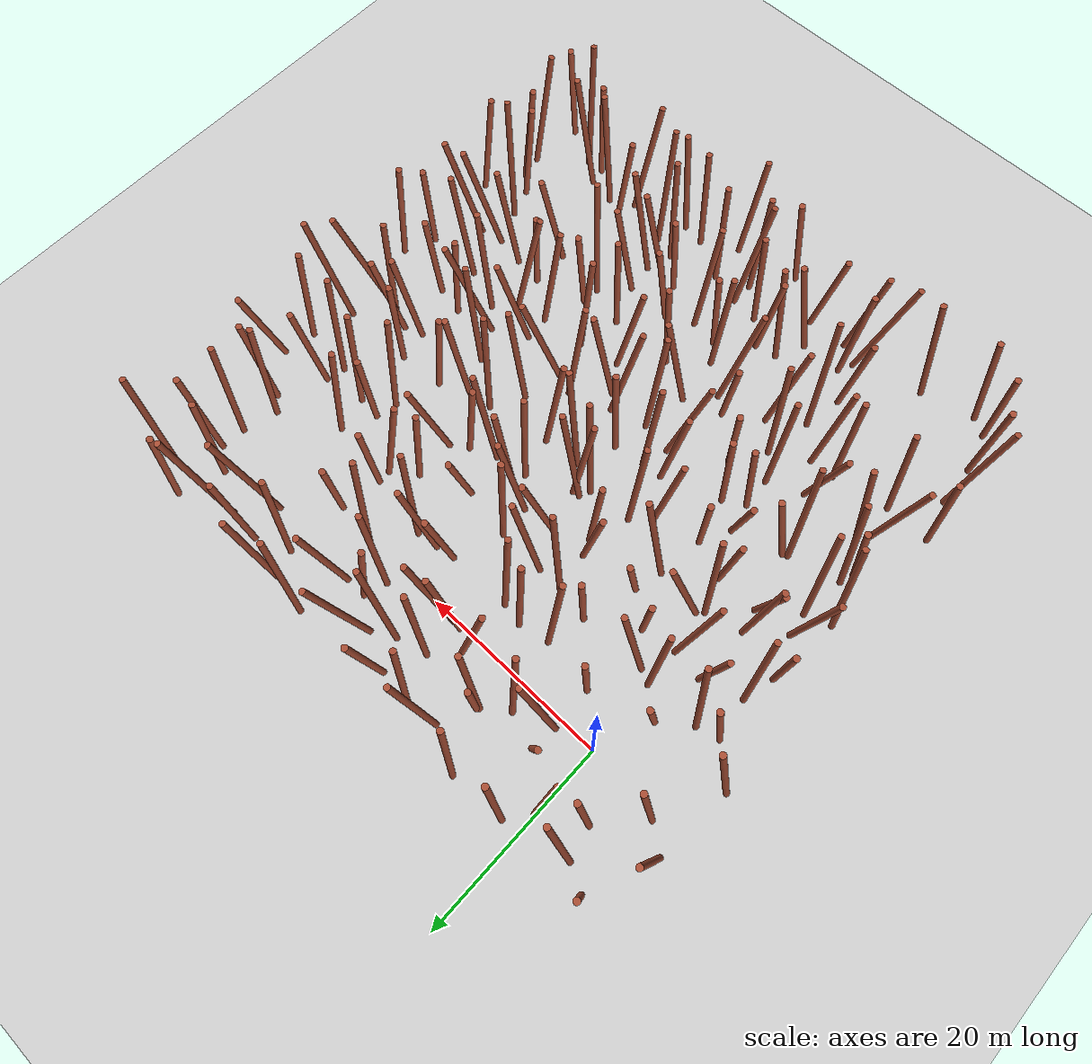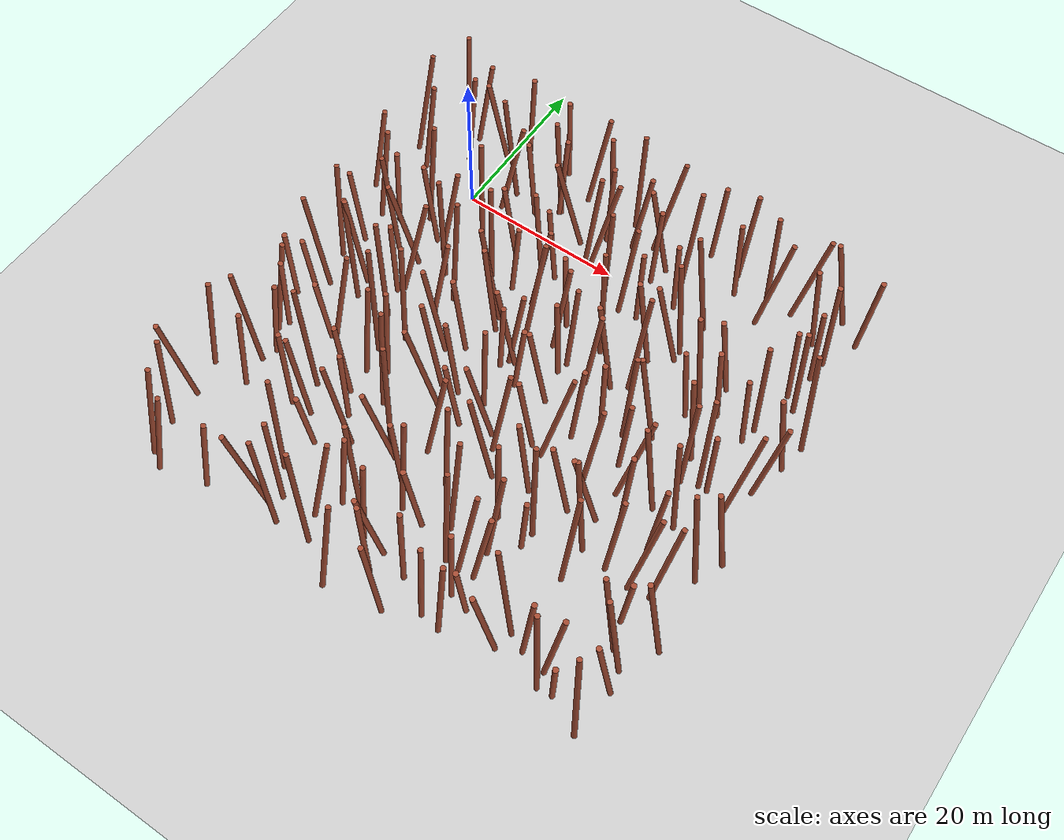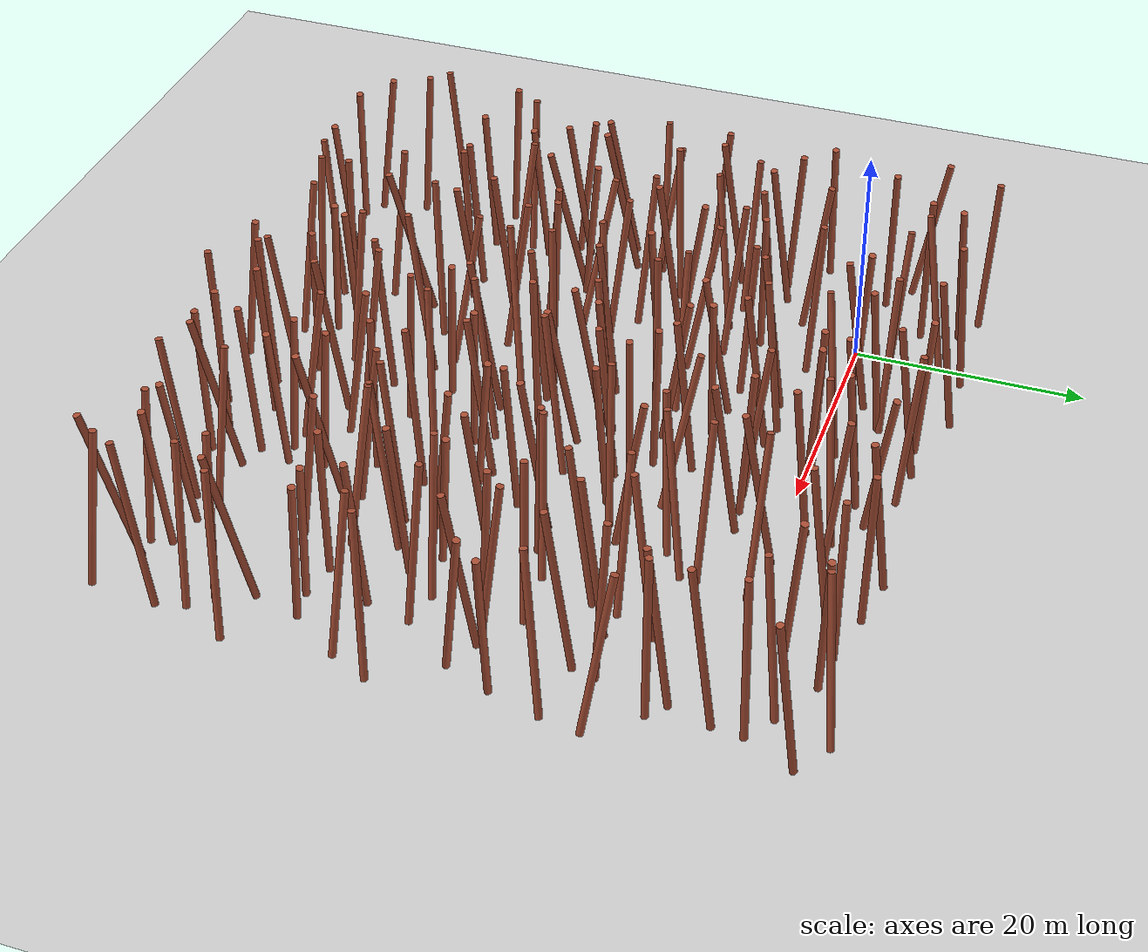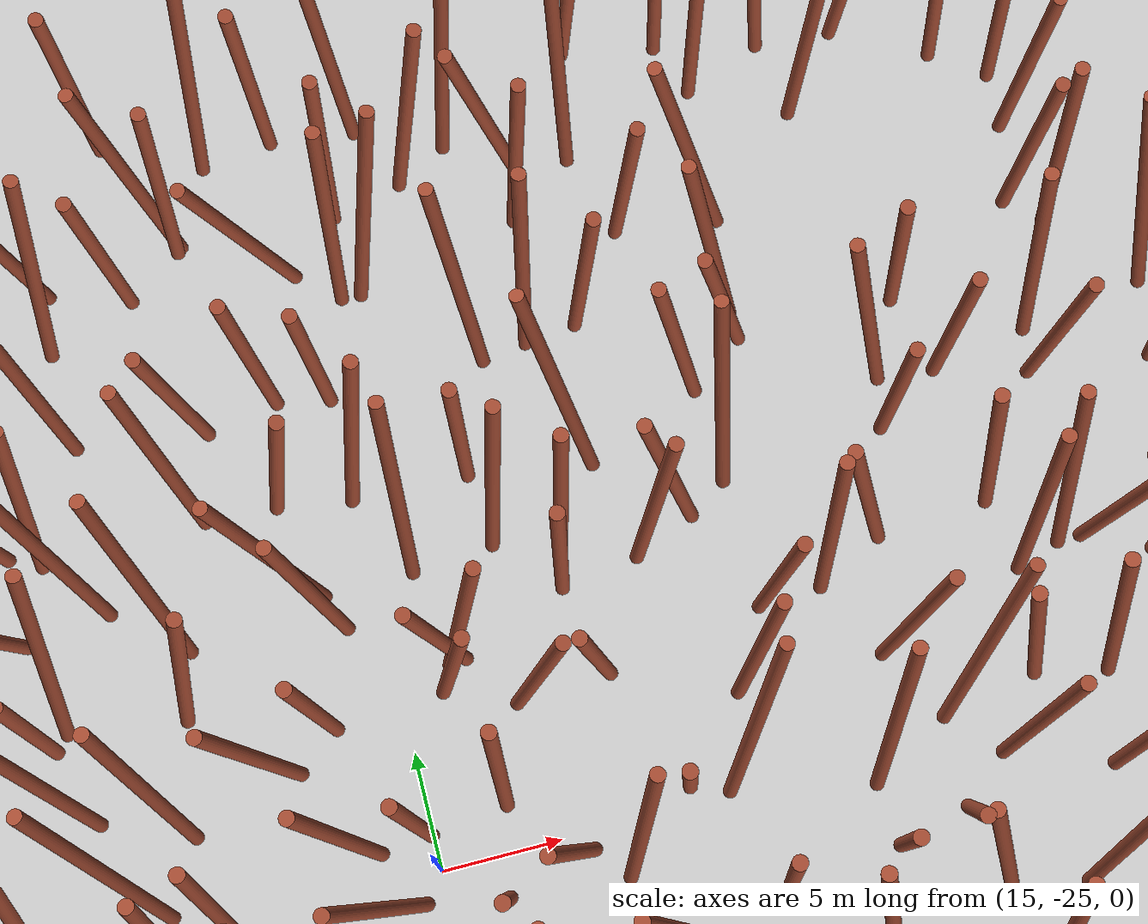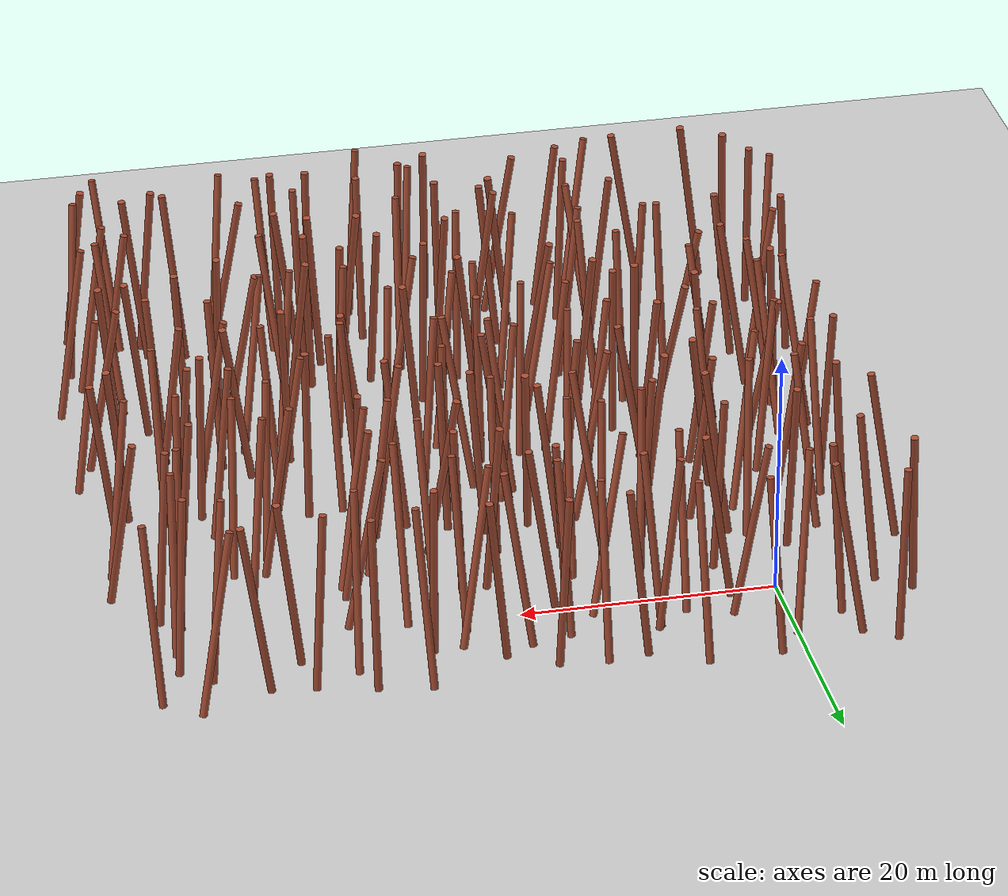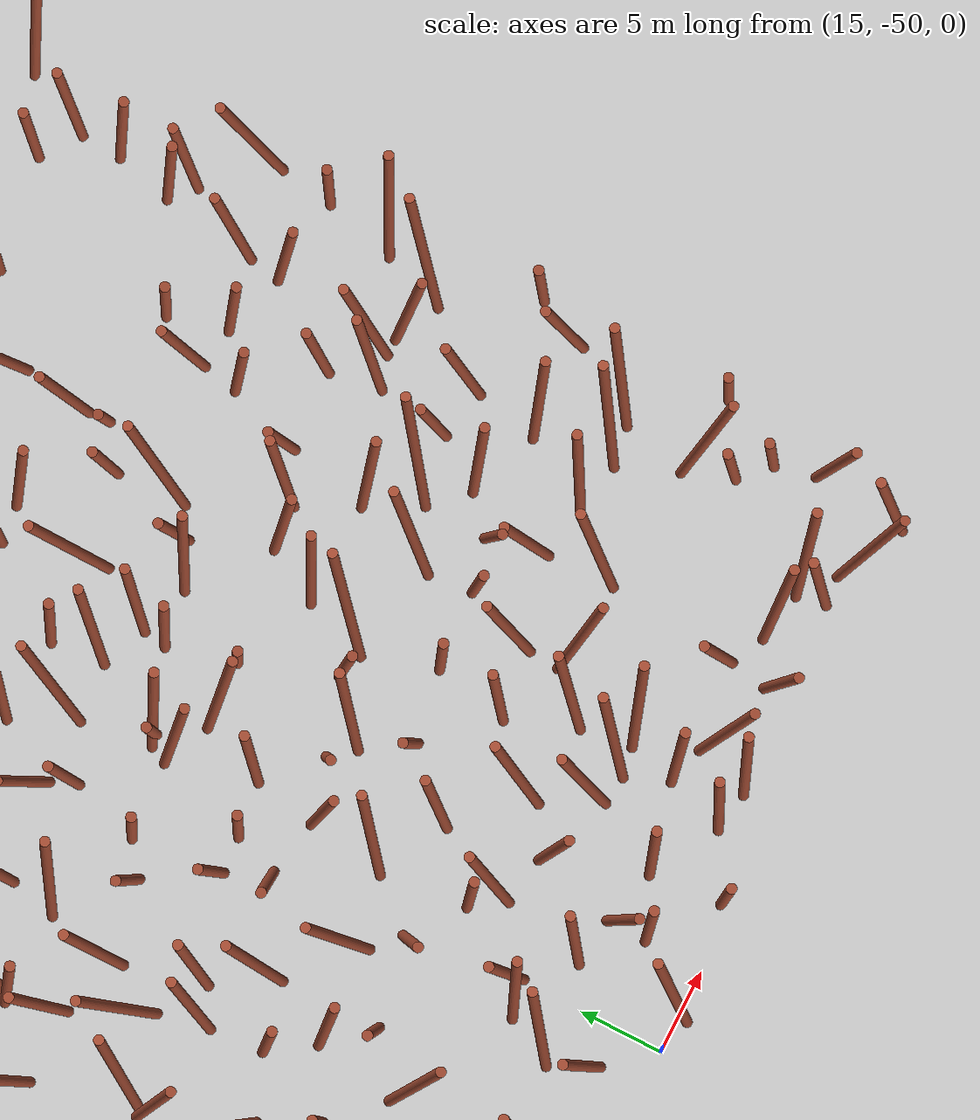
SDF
<?xml version='1.0' encoding='utf-8'?>
<sdf version="1.5">
  <world name="default">
    <!-- A global light source -->
    <include>
      <uri>model://sun</uri>
    </include>
    <!-- A ground plane -->
    <include>
      <uri>model://ground_plane</uri>
    </include>
    <include>
      <uri>model://asphalt_plane</uri>
      <pose>0 0 -0.000001 0 0 0</pose>
    </include>
    <model name="unit_cylinder_0">
      <pose>-7.53433 -47.54416 7.70000 -0.16482 0.05793 0.00000</pose>
      <gravity>0 0 0</gravity>
      <link name="link">
        <gravity>1</gravity>
        <inertial>
          <mass>100</mass>
          <inertia>
            <ixx>20</ixx>
            <ixy>0</ixy>
            <ixz>0</ixz>
            <iyy>20</iyy>
            <iyz>0</iyz>
            <izz>20</izz>
          </inertia>
          <pose>0 0 0 0 -0 0</pose>
        </inertial>
        <collision name="collision">
          <geometry>
            <cylinder>
              <radius>0.300</radius>
              <length>15.000</length>
            </cylinder>
          </geometry>
          <max_contacts>10</max_contacts>
          <surface>
            <contact>
              <ode />
            </contact>
            <bounce />
            <friction>
              <torsional>
                <ode />
              </torsional>
              <ode />
            </friction>
          </surface>
        </collision>
        <visual name="visual">
          <geometry>
            <cylinder>
              <radius>0.300</radius>
              <length>15.000</length>
            </cylinder>
          </geometry>
          <material>
            <script>
              <name>Gazebo/Bricks</name>
              <uri>file://media/materials/scripts/gazebo.material</uri>
            </script>
          </material>
        </visual>
        <self_collide>0</self_collide>
        <enable_wind>0</enable_wind>
        <kinematic>1</kinematic>
      </link>
      <static>0</static>
      <plugin name="dynamic_obstacle_motion_0" filename="libobstaclePathPlugin.so">
        <motion_type>proximity_linear</motion_type>
        <direction>0.377619958 -0.925960673 0.000000000</direction>
        <velocity>1.842558451</velocity>
        <activation_distance>20.000000000</activation_distance>
        <activation_model>iris</activation_model>
        <orientation>false</orientation>
        <marker_enabled>true</marker_enabled>
        <marker_id>0</marker_id>
        <marker_radius>0.300000000</marker_radius>
        <marker_height>15.000000000</marker_height>
        <marker_rate>20.0</marker_rate>
        <marker_topic>/uav_simulator/dynamic_obstacles</marker_topic>
        <marker_frame>map</marker_frame>
      </plugin>
    </model>
    <model name="unit_cylinder_1">
      <pose>-8.78273 -44.01166 7.70000 -0.09766 0.02668 0.00000</pose>
      <gravity>0 0 0</gravity>
      <link name="link">
        <gravity>1</gravity>
        <inertial>
          <mass>100</mass>
          <inertia>
            <ixx>20</ixx>
            <ixy>0</ixy>
            <ixz>0</ixz>
            <iyy>20</iyy>
            <iyz>0</iyz>
            <izz>20</izz>
          </inertia>
          <pose>0 0 0 0 -0 0</pose>
        </inertial>
        <collision name="collision">
          <geometry>
            <cylinder>
              <radius>0.300</radius>
              <length>15.000</length>
            </cylinder>
          </geometry>
          <max_contacts>10</max_contacts>
          <surface>
            <contact>
              <ode />
            </contact>
            <bounce />
            <friction>
              <torsional>
                <ode />
              </torsional>
              <ode />
            </friction>
          </surface>
        </collision>
        <visual name="visual">
          <geometry>
            <cylinder>
              <radius>0.300</radius>
              <length>15.000</length>
            </cylinder>
          </geometry>
          <material>
            <script>
              <name>Gazebo/Bricks</name>
              <uri>file://media/materials/scripts/gazebo.material</uri>
            </script>
          </material>
        </visual>
        <self_collide>0</self_collide>
        <enable_wind>0</enable_wind>
        <kinematic>0</kinematic>
      </link>
      <static>1</static>
    </model>
    <model name="unit_cylinder_2">
      <pose>-9.56069 -41.14395 7.70000 0.10310 -0.05871 0.00000</pose>
      <gravity>0 0 0</gravity>
      <link name="link">
        <gravity>1</gravity>
        <inertial>
          <mass>100</mass>
          <inertia>
            <ixx>20</ixx>
            <ixy>0</ixy>
            <ixz>0</ixz>
            <iyy>20</iyy>
            <iyz>0</iyz>
            <izz>20</izz>
          </inertia>
          <pose>0 0 0 0 -0 0</pose>
        </inertial>
        <collision name="collision">
          <geometry>
            <cylinder>
              <radius>0.300</radius>
              <length>15.000</length>
            </cylinder>
          </geometry>
          <max_contacts>10</max_contacts>
          <surface>
            <contact>
              <ode />
            </contact>
            <bounce />
            <friction>
              <torsional>
                <ode />
              </torsional>
              <ode />
            </friction>
          </surface>
        </collision>
        <visual name="visual">
          <geometry>
            <cylinder>
              <radius>0.300</radius>
              <length>15.000</length>
            </cylinder>
          </geometry>
          <material>
            <script>
              <name>Gazebo/Bricks</name>
              <uri>file://media/materials/scripts/gazebo.material</uri>
            </script>
          </material>
        </visual>
        <self_collide>0</self_collide>
        <enable_wind>0</enable_wind>
        <kinematic>0</kinematic>
      </link>
      <static>1</static>
    </model>
    <model name="unit_cylinder_3">
      <pose>-9.64381 -35.40931 7.70000 -0.08878 0.07868 0.00000</pose>
      <gravity>0 0 0</gravity>
      <link name="link">
        <gravity>1</gravity>
        <inertial>
          <mass>100</mass>
          <inertia>
            <ixx>20</ixx>
            <ixy>0</ixy>
            <ixz>0</ixz>
            <iyy>20</iyy>
            <iyz>0</iyz>
            <izz>20</izz>
          </inertia>
          <pose>0 0 0 0 -0 0</pose>
        </inertial>
        <collision name="collision">
          <geometry>
            <cylinder>
              <radius>0.300</radius>
              <length>15.000</length>
            </cylinder>
          </geometry>
          <max_contacts>10</max_contacts>
          <surface>
            <contact>
              <ode />
            </contact>
            <bounce />
            <friction>
              <torsional>
                <ode />
              </torsional>
              <ode />
            </friction>
          </surface>
        </collision>
        <visual name="visual">
          <geometry>
            <cylinder>
              <radius>0.300</radius>
              <length>15.000</length>
            </cylinder>
          </geometry>
          <material>
            <script>
              <name>Gazebo/Bricks</name>
              <uri>file://media/materials/scripts/gazebo.material</uri>
            </script>
          </material>
        </visual>
        <self_collide>0</self_collide>
        <enable_wind>0</enable_wind>
        <kinematic>1</kinematic>
      </link>
      <static>0</static>
      <plugin name="dynamic_obstacle_motion_3" filename="libobstaclePathPlugin.so">
        <motion_type>proximity_linear</motion_type>
        <direction>-0.023510522 -0.999723589 0.000000000</direction>
        <velocity>0.789084002</velocity>
        <activation_distance>20.000000000</activation_distance>
        <activation_model>iris</activation_model>
        <orientation>false</orientation>
        <marker_enabled>true</marker_enabled>
        <marker_id>3</marker_id>
        <marker_radius>0.300000000</marker_radius>
        <marker_height>15.000000000</marker_height>
        <marker_rate>20.0</marker_rate>
        <marker_topic>/uav_simulator/dynamic_obstacles</marker_topic>
        <marker_frame>map</marker_frame>
      </plugin>
    </model>
    <model name="unit_cylinder_4">
      <pose>-6.93488 -32.61874 7.70000 -0.00841 -0.12245 0.00000</pose>
      <gravity>0 0 0</gravity>
      <link name="link">
        <gravity>1</gravity>
        <inertial>
          <mass>100</mass>
          <inertia>
            <ixx>20</ixx>
            <ixy>0</ixy>
            <ixz>0</ixz>
            <iyy>20</iyy>
            <iyz>0</iyz>
            <izz>20</izz>
          </inertia>
          <pose>0 0 0 0 -0 0</pose>
        </inertial>
        <collision name="collision">
          <geometry>
            <cylinder>
              <radius>0.300</radius>
              <length>15.000</length>
            </cylinder>
          </geometry>
          <max_contacts>10</max_contacts>
          <surface>
            <contact>
              <ode />
            </contact>
            <bounce />
            <friction>
              <torsional>
                <ode />
              </torsional>
              <ode />
            </friction>
          </surface>
        </collision>
        <visual name="visual">
          <geometry>
            <cylinder>
              <radius>0.300</radius>
              <length>15.000</length>
            </cylinder>
          </geometry>
          <material>
            <script>
              <name>Gazebo/Bricks</name>
              <uri>file://media/materials/scripts/gazebo.material</uri>
            </script>
          </material>
        </visual>
        <self_collide>0</self_collide>
        <enable_wind>0</enable_wind>
        <kinematic>1</kinematic>
      </link>
      <static>0</static>
      <plugin name="dynamic_obstacle_motion_4" filename="libobstaclePathPlugin.so">
        <motion_type>proximity_linear</motion_type>
        <direction>-0.650799631 0.759249524 0.000000000</direction>
        <velocity>0.699930068</velocity>
        <activation_distance>20.000000000</activation_distance>
        <activation_model>iris</activation_model>
        <orientation>false</orientation>
        <marker_enabled>true</marker_enabled>
        <marker_id>4</marker_id>
        <marker_radius>0.300000000</marker_radius>
        <marker_height>15.000000000</marker_height>
        <marker_rate>20.0</marker_rate>
        <marker_topic>/uav_simulator/dynamic_obstacles</marker_topic>
        <marker_frame>map</marker_frame>
      </plugin>
    </model>
    <model name="unit_cylinder_5">
      <pose>-6.59663 -27.28301 7.70000 -0.14401 0.08279 0.00000</pose>
      <gravity>0 0 0</gravity>
      <link name="link">
        <gravity>1</gravity>
        <inertial>
          <mass>100</mass>
          <inertia>
            <ixx>20</ixx>
            <ixy>0</ixy>
            <ixz>0</ixz>
            <iyy>20</iyy>
            <iyz>0</iyz>
            <izz>20</izz>
          </inertia>
          <pose>0 0 0 0 -0 0</pose>
        </inertial>
        <collision name="collision">
          <geometry>
            <cylinder>
              <radius>0.300</radius>
              <length>15.000</length>
            </cylinder>
          </geometry>
          <max_contacts>10</max_contacts>
          <surface>
            <contact>
              <ode />
            </contact>
            <bounce />
            <friction>
              <torsional>
                <ode />
              </torsional>
              <ode />
            </friction>
          </surface>
        </collision>
        <visual name="visual">
          <geometry>
            <cylinder>
              <radius>0.300</radius>
              <length>15.000</length>
            </cylinder>
          </geometry>
          <material>
            <script>
              <name>Gazebo/Bricks</name>
              <uri>file://media/materials/scripts/gazebo.material</uri>
            </script>
          </material>
        </visual>
        <self_collide>0</self_collide>
        <enable_wind>0</enable_wind>
        <kinematic>0</kinematic>
      </link>
      <static>1</static>
    </model>
    <model name="unit_cylinder_6">
      <pose>-7.63744 -24.13479 7.70000 0.12581 0.13626 0.00000</pose>
      <gravity>0 0 0</gravity>
      <link name="link">
        <gravity>1</gravity>
        <inertial>
          <mass>100</mass>
          <inertia>
            <ixx>20</ixx>
            <ixy>0</ixy>
            <ixz>0</ixz>
            <iyy>20</iyy>
            <iyz>0</iyz>
            <izz>20</izz>
          </inertia>
          <pose>0 0 0 0 -0 0</pose>
        </inertial>
        <collision name="collision">
          <geometry>
            <cylinder>
              <radius>0.300</radius>
              <length>15.000</length>
            </cylinder>
          </geometry>
          <max_contacts>10</max_contacts>
          <surface>
            <contact>
              <ode />
            </contact>
            <bounce />
            <friction>
              <torsional>
                <ode />
              </torsional>
              <ode />
            </friction>
          </surface>
        </collision>
        <visual name="visual">
          <geometry>
            <cylinder>
              <radius>0.300</radius>
              <length>15.000</length>
            </cylinder>
          </geometry>
          <material>
            <script>
              <name>Gazebo/Bricks</name>
              <uri>file://media/materials/scripts/gazebo.material</uri>
            </script>
          </material>
        </visual>
        <self_collide>0</self_collide>
        <enable_wind>0</enable_wind>
        <kinematic>0</kinematic>
      </link>
      <static>1</static>
    </model>
    <model name="unit_cylinder_7">
      <pose>-7.21971 -19.97460 7.70000 0.00352 -0.12097 0.00000</pose>
      <gravity>0 0 0</gravity>
      <link name="link">
        <gravity>1</gravity>
        <inertial>
          <mass>100</mass>
          <inertia>
            <ixx>20</ixx>
            <ixy>0</ixy>
            <ixz>0</ixz>
            <iyy>20</iyy>
            <iyz>0</iyz>
            <izz>20</izz>
          </inertia>
          <pose>0 0 0 0 -0 0</pose>
        </inertial>
        <collision name="collision">
          <geometry>
            <cylinder>
              <radius>0.300</radius>
              <length>15.000</length>
            </cylinder>
          </geometry>
          <max_contacts>10</max_contacts>
          <surface>
            <contact>
              <ode />
            </contact>
            <bounce />
            <friction>
              <torsional>
                <ode />
              </torsional>
              <ode />
            </friction>
          </surface>
        </collision>
        <visual name="visual">
          <geometry>
            <cylinder>
              <radius>0.300</radius>
              <length>15.000</length>
            </cylinder>
          </geometry>
          <material>
            <script>
              <name>Gazebo/Bricks</name>
              <uri>file://media/materials/scripts/gazebo.material</uri>
            </script>
          </material>
        </visual>
        <self_collide>0</self_collide>
        <enable_wind>0</enable_wind>
        <kinematic>0</kinematic>
      </link>
      <static>1</static>
    </model>
    <model name="unit_cylinder_8">
      <pose>-7.85168 -15.01514 7.70000 -0.09576 -0.01622 0.00000</pose>
      <gravity>0 0 0</gravity>
      <link name="link">
        <gravity>1</gravity>
        <inertial>
          <mass>100</mass>
          <inertia>
            <ixx>20</ixx>
            <ixy>0</ixy>
            <ixz>0</ixz>
            <iyy>20</iyy>
            <iyz>0</iyz>
            <izz>20</izz>
          </inertia>
          <pose>0 0 0 0 -0 0</pose>
        </inertial>
        <collision name="collision">
          <geometry>
            <cylinder>
              <radius>0.300</radius>
              <length>15.000</length>
            </cylinder>
          </geometry>
          <max_contacts>10</max_contacts>
          <surface>
            <contact>
              <ode />
            </contact>
            <bounce />
            <friction>
              <torsional>
                <ode />
              </torsional>
              <ode />
            </friction>
          </surface>
        </collision>
        <visual name="visual">
          <geometry>
            <cylinder>
              <radius>0.300</radius>
              <length>15.000</length>
            </cylinder>
          </geometry>
          <material>
            <script>
              <name>Gazebo/Bricks</name>
              <uri>file://media/materials/scripts/gazebo.material</uri>
            </script>
          </material>
        </visual>
        <self_collide>0</self_collide>
        <enable_wind>0</enable_wind>
        <kinematic>1</kinematic>
      </link>
      <static>0</static>
      <plugin name="dynamic_obstacle_motion_8" filename="libobstaclePathPlugin.so">
        <motion_type>proximity_linear</motion_type>
        <direction>-0.683871958 -0.729602046 0.000000000</direction>
        <velocity>0.864553433</velocity>
        <activation_distance>20.000000000</activation_distance>
        <activation_model>iris</activation_model>
        <orientation>false</orientation>
        <marker_enabled>true</marker_enabled>
        <marker_id>8</marker_id>
        <marker_radius>0.300000000</marker_radius>
        <marker_height>15.000000000</marker_height>
        <marker_rate>20.0</marker_rate>
        <marker_topic>/uav_simulator/dynamic_obstacles</marker_topic>
        <marker_frame>map</marker_frame>
      </plugin>
    </model>
    <model name="unit_cylinder_9">
      <pose>-6.52075 -13.38467 7.70000 0.12282 0.05243 0.00000</pose>
      <gravity>0 0 0</gravity>
      <link name="link">
        <gravity>1</gravity>
        <inertial>
          <mass>100</mass>
          <inertia>
            <ixx>20</ixx>
            <ixy>0</ixy>
            <ixz>0</ixz>
            <iyy>20</iyy>
            <iyz>0</iyz>
            <izz>20</izz>
          </inertia>
          <pose>0 0 0 0 -0 0</pose>
        </inertial>
        <collision name="collision">
          <geometry>
            <cylinder>
              <radius>0.300</radius>
              <length>15.000</length>
            </cylinder>
          </geometry>
          <max_contacts>10</max_contacts>
          <surface>
            <contact>
              <ode />
            </contact>
            <bounce />
            <friction>
              <torsional>
                <ode />
              </torsional>
              <ode />
            </friction>
          </surface>
        </collision>
        <visual name="visual">
          <geometry>
            <cylinder>
              <radius>0.300</radius>
              <length>15.000</length>
            </cylinder>
          </geometry>
          <material>
            <script>
              <name>Gazebo/Bricks</name>
              <uri>file://media/materials/scripts/gazebo.material</uri>
            </script>
          </material>
        </visual>
        <self_collide>0</self_collide>
        <enable_wind>0</enable_wind>
        <kinematic>0</kinematic>
      </link>
      <static>1</static>
    </model>
    <model name="unit_cylinder_10">
      <pose>-6.92610 -7.73222 7.70000 -0.07882 0.08934 0.00000</pose>
      <gravity>0 0 0</gravity>
      <link name="link">
        <gravity>1</gravity>
        <inertial>
          <mass>100</mass>
          <inertia>
            <ixx>20</ixx>
            <ixy>0</ixy>
            <ixz>0</ixz>
            <iyy>20</iyy>
            <iyz>0</iyz>
            <izz>20</izz>
          </inertia>
          <pose>0 0 0 0 -0 0</pose>
        </inertial>
        <collision name="collision">
          <geometry>
            <cylinder>
              <radius>0.300</radius>
              <length>15.000</length>
            </cylinder>
          </geometry>
          <max_contacts>10</max_contacts>
          <surface>
            <contact>
              <ode />
            </contact>
            <bounce />
            <friction>
              <torsional>
                <ode />
              </torsional>
              <ode />
            </friction>
          </surface>
        </collision>
        <visual name="visual">
          <geometry>
            <cylinder>
              <radius>0.300</radius>
              <length>15.000</length>
            </cylinder>
          </geometry>
          <material>
            <script>
              <name>Gazebo/Bricks</name>
              <uri>file://media/materials/scripts/gazebo.material</uri>
            </script>
          </material>
        </visual>
        <self_collide>0</self_collide>
        <enable_wind>0</enable_wind>
        <kinematic>1</kinematic>
      </link>
      <static>0</static>
      <plugin name="dynamic_obstacle_motion_10" filename="libobstaclePathPlugin.so">
        <motion_type>proximity_linear</motion_type>
        <direction>-0.184538150 -0.982825351 0.000000000</direction>
        <velocity>0.998804224</velocity>
        <activation_distance>20.000000000</activation_distance>
        <activation_model>iris</activation_model>
        <orientation>false</orientation>
        <marker_enabled>true</marker_enabled>
        <marker_id>10</marker_id>
        <marker_radius>0.300000000</marker_radius>
        <marker_height>15.000000000</marker_height>
        <marker_rate>20.0</marker_rate>
        <marker_topic>/uav_simulator/dynamic_obstacles</marker_topic>
        <marker_frame>map</marker_frame>
      </plugin>
    </model>
    <model name="unit_cylinder_11">
      <pose>-9.69069 -5.02940 7.70000 -0.02254 0.16852 0.00000</pose>
      <gravity>0 0 0</gravity>
      <link name="link">
        <gravity>1</gravity>
        <inertial>
          <mass>100</mass>
          <inertia>
            <ixx>20</ixx>
            <ixy>0</ixy>
            <ixz>0</ixz>
            <iyy>20</iyy>
            <iyz>0</iyz>
            <izz>20</izz>
          </inertia>
          <pose>0 0 0 0 -0 0</pose>
        </inertial>
        <collision name="collision">
          <geometry>
            <cylinder>
              <radius>0.300</radius>
              <length>15.000</length>
            </cylinder>
          </geometry>
          <max_contacts>10</max_contacts>
          <surface>
            <contact>
              <ode />
            </contact>
            <bounce />
            <friction>
              <torsional>
                <ode />
              </torsional>
              <ode />
            </friction>
          </surface>
        </collision>
        <visual name="visual">
          <geometry>
            <cylinder>
              <radius>0.300</radius>
              <length>15.000</length>
            </cylinder>
          </geometry>
          <material>
            <script>
              <name>Gazebo/Bricks</name>
              <uri>file://media/materials/scripts/gazebo.material</uri>
            </script>
          </material>
        </visual>
        <self_collide>0</self_collide>
        <enable_wind>0</enable_wind>
        <kinematic>1</kinematic>
      </link>
      <static>0</static>
      <plugin name="dynamic_obstacle_motion_11" filename="libobstaclePathPlugin.so">
        <motion_type>proximity_linear</motion_type>
        <direction>-0.606140332 -0.795357717 0.000000000</direction>
        <velocity>0.567851102</velocity>
        <activation_distance>20.000000000</activation_distance>
        <activation_model>iris</activation_model>
        <orientation>false</orientation>
        <marker_enabled>true</marker_enabled>
        <marker_id>11</marker_id>
        <marker_radius>0.300000000</marker_radius>
        <marker_height>15.000000000</marker_height>
        <marker_rate>20.0</marker_rate>
        <marker_topic>/uav_simulator/dynamic_obstacles</marker_topic>
        <marker_frame>map</marker_frame>
      </plugin>
    </model>
    <model name="unit_cylinder_12">
      <pose>-6.78483 1.04766 7.70000 -0.02488 0.11770 0.00000</pose>
      <gravity>0 0 0</gravity>
      <link name="link">
        <gravity>1</gravity>
        <inertial>
          <mass>100</mass>
          <inertia>
            <ixx>20</ixx>
            <ixy>0</ixy>
            <ixz>0</ixz>
            <iyy>20</iyy>
            <iyz>0</iyz>
            <izz>20</izz>
          </inertia>
          <pose>0 0 0 0 -0 0</pose>
        </inertial>
        <collision name="collision">
          <geometry>
            <cylinder>
              <radius>0.300</radius>
              <length>15.000</length>
            </cylinder>
          </geometry>
          <max_contacts>10</max_contacts>
          <surface>
            <contact>
              <ode />
            </contact>
            <bounce />
            <friction>
              <torsional>
                <ode />
              </torsional>
              <ode />
            </friction>
          </surface>
        </collision>
        <visual name="visual">
          <geometry>
            <cylinder>
              <radius>0.300</radius>
              <length>15.000</length>
            </cylinder>
          </geometry>
          <material>
            <script>
              <name>Gazebo/Bricks</name>
              <uri>file://media/materials/scripts/gazebo.material</uri>
            </script>
          </material>
        </visual>
        <self_collide>0</self_collide>
        <enable_wind>0</enable_wind>
        <kinematic>0</kinematic>
      </link>
      <static>1</static>
    </model>
    <model name="unit_cylinder_13">
      <pose>-9.58581 3.96208 7.70000 -0.16946 0.07617 0.00000</pose>
      <gravity>0 0 0</gravity>
      <link name="link">
        <gravity>1</gravity>
        <inertial>
          <mass>100</mass>
          <inertia>
            <ixx>20</ixx>
            <ixy>0</ixy>
            <ixz>0</ixz>
            <iyy>20</iyy>
            <iyz>0</iyz>
            <izz>20</izz>
          </inertia>
          <pose>0 0 0 0 -0 0</pose>
        </inertial>
        <collision name="collision">
          <geometry>
            <cylinder>
              <radius>0.300</radius>
              <length>15.000</length>
            </cylinder>
          </geometry>
          <max_contacts>10</max_contacts>
          <surface>
            <contact>
              <ode />
            </contact>
            <bounce />
            <friction>
              <torsional>
                <ode />
              </torsional>
              <ode />
            </friction>
          </surface>
        </collision>
        <visual name="visual">
          <geometry>
            <cylinder>
              <radius>0.300</radius>
              <length>15.000</length>
            </cylinder>
          </geometry>
          <material>
            <script>
              <name>Gazebo/Bricks</name>
              <uri>file://media/materials/scripts/gazebo.material</uri>
            </script>
          </material>
        </visual>
        <self_collide>0</self_collide>
        <enable_wind>0</enable_wind>
        <kinematic>0</kinematic>
      </link>
      <static>1</static>
    </model>
    <model name="unit_cylinder_14">
      <pose>-7.21917 9.66156 7.70000 -0.03544 -0.00035 0.00000</pose>
      <gravity>0 0 0</gravity>
      <link name="link">
        <gravity>1</gravity>
        <inertial>
          <mass>100</mass>
          <inertia>
            <ixx>20</ixx>
            <ixy>0</ixy>
            <ixz>0</ixz>
            <iyy>20</iyy>
            <iyz>0</iyz>
            <izz>20</izz>
          </inertia>
          <pose>0 0 0 0 -0 0</pose>
        </inertial>
        <collision name="collision">
          <geometry>
            <cylinder>
              <radius>0.300</radius>
              <length>15.000</length>
            </cylinder>
          </geometry>
          <max_contacts>10</max_contacts>
          <surface>
            <contact>
              <ode />
            </contact>
            <bounce />
            <friction>
              <torsional>
                <ode />
              </torsional>
              <ode />
            </friction>
          </surface>
        </collision>
        <visual name="visual">
          <geometry>
            <cylinder>
              <radius>0.300</radius>
              <length>15.000</length>
            </cylinder>
          </geometry>
          <material>
            <script>
              <name>Gazebo/Bricks</name>
              <uri>file://media/materials/scripts/gazebo.material</uri>
            </script>
          </material>
        </visual>
        <self_collide>0</self_collide>
        <enable_wind>0</enable_wind>
        <kinematic>0</kinematic>
      </link>
      <static>1</static>
    </model>
    <model name="unit_cylinder_15">
      <pose>-5.10277 -49.07799 7.70000 -0.10513 0.14993 0.00000</pose>
      <gravity>0 0 0</gravity>
      <link name="link">
        <gravity>1</gravity>
        <inertial>
          <mass>100</mass>
          <inertia>
            <ixx>20</ixx>
            <ixy>0</ixy>
            <ixz>0</ixz>
            <iyy>20</iyy>
            <iyz>0</iyz>
            <izz>20</izz>
          </inertia>
          <pose>0 0 0 0 -0 0</pose>
        </inertial>
        <collision name="collision">
          <geometry>
            <cylinder>
              <radius>0.300</radius>
              <length>15.000</length>
            </cylinder>
          </geometry>
          <max_contacts>10</max_contacts>
          <surface>
            <contact>
              <ode />
            </contact>
            <bounce />
            <friction>
              <torsional>
                <ode />
              </torsional>
              <ode />
            </friction>
          </surface>
        </collision>
        <visual name="visual">
          <geometry>
            <cylinder>
              <radius>0.300</radius>
              <length>15.000</length>
            </cylinder>
          </geometry>
          <material>
            <script>
              <name>Gazebo/Bricks</name>
              <uri>file://media/materials/scripts/gazebo.material</uri>
            </script>
          </material>
        </visual>
        <self_collide>0</self_collide>
        <enable_wind>0</enable_wind>
        <kinematic>1</kinematic>
      </link>
      <static>0</static>
      <plugin name="dynamic_obstacle_motion_15" filename="libobstaclePathPlugin.so">
        <motion_type>proximity_linear</motion_type>
        <direction>-0.502778501 0.864415282 0.000000000</direction>
        <velocity>1.408256255</velocity>
        <activation_distance>20.000000000</activation_distance>
        <activation_model>iris</activation_model>
        <orientation>false</orientation>
        <marker_enabled>true</marker_enabled>
        <marker_id>15</marker_id>
        <marker_radius>0.300000000</marker_radius>
        <marker_height>15.000000000</marker_height>
        <marker_rate>20.0</marker_rate>
        <marker_topic>/uav_simulator/dynamic_obstacles</marker_topic>
        <marker_frame>map</marker_frame>
      </plugin>
    </model>
    <model name="unit_cylinder_16">
      <pose>-4.68098 -36.06371 7.70000 -0.01164 0.11515 0.00000</pose>
      <gravity>0 0 0</gravity>
      <link name="link">
        <gravity>1</gravity>
        <inertial>
          <mass>100</mass>
          <inertia>
            <ixx>20</ixx>
            <ixy>0</ixy>
            <ixz>0</ixz>
            <iyy>20</iyy>
            <iyz>0</iyz>
            <izz>20</izz>
          </inertia>
          <pose>0 0 0 0 -0 0</pose>
        </inertial>
        <collision name="collision">
          <geometry>
            <cylinder>
              <radius>0.300</radius>
              <length>15.000</length>
            </cylinder>
          </geometry>
          <max_contacts>10</max_contacts>
          <surface>
            <contact>
              <ode />
            </contact>
            <bounce />
            <friction>
              <torsional>
                <ode />
              </torsional>
              <ode />
            </friction>
          </surface>
        </collision>
        <visual name="visual">
          <geometry>
            <cylinder>
              <radius>0.300</radius>
              <length>15.000</length>
            </cylinder>
          </geometry>
          <material>
            <script>
              <name>Gazebo/Bricks</name>
              <uri>file://media/materials/scripts/gazebo.material</uri>
            </script>
          </material>
        </visual>
        <self_collide>0</self_collide>
        <enable_wind>0</enable_wind>
        <kinematic>1</kinematic>
      </link>
      <static>0</static>
      <plugin name="dynamic_obstacle_motion_16" filename="libobstaclePathPlugin.so">
        <motion_type>proximity_linear</motion_type>
        <direction>-0.969477639 0.245179747 -0.000000000</direction>
        <velocity>0.384918326</velocity>
        <activation_distance>20.000000000</activation_distance>
        <activation_model>iris</activation_model>
        <orientation>false</orientation>
        <marker_enabled>true</marker_enabled>
        <marker_id>16</marker_id>
        <marker_radius>0.300000000</marker_radius>
        <marker_height>15.000000000</marker_height>
        <marker_rate>20.0</marker_rate>
        <marker_topic>/uav_simulator/dynamic_obstacles</marker_topic>
        <marker_frame>map</marker_frame>
      </plugin>
    </model>
    <model name="unit_cylinder_17">
      <pose>-4.26286 -30.93398 7.70000 0.00834 0.15929 0.00000</pose>
      <gravity>0 0 0</gravity>
      <link name="link">
        <gravity>1</gravity>
        <inertial>
          <mass>100</mass>
          <inertia>
            <ixx>20</ixx>
            <ixy>0</ixy>
            <ixz>0</ixz>
            <iyy>20</iyy>
            <iyz>0</iyz>
            <izz>20</izz>
          </inertia>
          <pose>0 0 0 0 -0 0</pose>
        </inertial>
        <collision name="collision">
          <geometry>
            <cylinder>
              <radius>0.300</radius>
              <length>15.000</length>
            </cylinder>
          </geometry>
          <max_contacts>10</max_contacts>
          <surface>
            <contact>
              <ode />
            </contact>
            <bounce />
            <friction>
              <torsional>
                <ode />
              </torsional>
              <ode />
            </friction>
          </surface>
        </collision>
        <visual name="visual">
          <geometry>
            <cylinder>
              <radius>0.300</radius>
              <length>15.000</length>
            </cylinder>
          </geometry>
          <material>
            <script>
              <name>Gazebo/Bricks</name>
              <uri>file://media/materials/scripts/gazebo.material</uri>
            </script>
          </material>
        </visual>
        <self_collide>0</self_collide>
        <enable_wind>0</enable_wind>
        <kinematic>0</kinematic>
      </link>
      <static>1</static>
    </model>
    <model name="unit_cylinder_18">
      <pose>-5.60371 -27.65031 7.70000 0.07561 0.14385 0.00000</pose>
      <gravity>0 0 0</gravity>
      <link name="link">
        <gravity>1</gravity>
        <inertial>
          <mass>100</mass>
          <inertia>
            <ixx>20</ixx>
            <ixy>0</ixy>
            <ixz>0</ixz>
            <iyy>20</iyy>
            <iyz>0</iyz>
            <izz>20</izz>
          </inertia>
          <pose>0 0 0 0 -0 0</pose>
        </inertial>
        <collision name="collision">
          <geometry>
            <cylinder>
              <radius>0.300</radius>
              <length>15.000</length>
            </cylinder>
          </geometry>
          <max_contacts>10</max_contacts>
          <surface>
            <contact>
              <ode />
            </contact>
            <bounce />
            <friction>
              <torsional>
                <ode />
              </torsional>
              <ode />
            </friction>
          </surface>
        </collision>
        <visual name="visual">
          <geometry>
            <cylinder>
              <radius>0.300</radius>
              <length>15.000</length>
            </cylinder>
          </geometry>
          <material>
            <script>
              <name>Gazebo/Bricks</name>
              <uri>file://media/materials/scripts/gazebo.material</uri>
            </script>
          </material>
        </visual>
        <self_collide>0</self_collide>
        <enable_wind>0</enable_wind>
        <kinematic>1</kinematic>
      </link>
      <static>0</static>
      <plugin name="dynamic_obstacle_motion_18" filename="libobstaclePathPlugin.so">
        <motion_type>proximity_linear</motion_type>
        <direction>0.450522633 0.892765007 0.000000000</direction>
        <velocity>0.734853509</velocity>
        <activation_distance>20.000000000</activation_distance>
        <activation_model>iris</activation_model>
        <orientation>false</orientation>
        <marker_enabled>true</marker_enabled>
        <marker_id>18</marker_id>
        <marker_radius>0.300000000</marker_radius>
        <marker_height>15.000000000</marker_height>
        <marker_rate>20.0</marker_rate>
        <marker_topic>/uav_simulator/dynamic_obstacles</marker_topic>
        <marker_frame>map</marker_frame>
      </plugin>
    </model>
    <model name="unit_cylinder_19">
      <pose>-5.27744 -23.47259 7.70000 0.15441 0.10550 0.00000</pose>
      <gravity>0 0 0</gravity>
      <link name="link">
        <gravity>1</gravity>
        <inertial>
          <mass>100</mass>
          <inertia>
            <ixx>20</ixx>
            <ixy>0</ixy>
            <ixz>0</ixz>
            <iyy>20</iyy>
            <iyz>0</iyz>
            <izz>20</izz>
          </inertia>
          <pose>0 0 0 0 -0 0</pose>
        </inertial>
        <collision name="collision">
          <geometry>
            <cylinder>
              <radius>0.300</radius>
              <length>15.000</length>
            </cylinder>
          </geometry>
          <max_contacts>10</max_contacts>
          <surface>
            <contact>
              <ode />
            </contact>
            <bounce />
            <friction>
              <torsional>
                <ode />
              </torsional>
              <ode />
            </friction>
          </surface>
        </collision>
        <visual name="visual">
          <geometry>
            <cylinder>
              <radius>0.300</radius>
              <length>15.000</length>
            </cylinder>
          </geometry>
          <material>
            <script>
              <name>Gazebo/Bricks</name>
              <uri>file://media/materials/scripts/gazebo.material</uri>
            </script>
          </material>
        </visual>
        <self_collide>0</self_collide>
        <enable_wind>0</enable_wind>
        <kinematic>1</kinematic>
      </link>
      <static>0</static>
      <plugin name="dynamic_obstacle_motion_19" filename="libobstaclePathPlugin.so">
        <motion_type>proximity_linear</motion_type>
        <direction>-0.062288158 0.998058207 0.000000000</direction>
        <velocity>1.470388580</velocity>
        <activation_distance>20.000000000</activation_distance>
        <activation_model>iris</activation_model>
        <orientation>false</orientation>
        <marker_enabled>true</marker_enabled>
        <marker_id>19</marker_id>
        <marker_radius>0.300000000</marker_radius>
        <marker_height>15.000000000</marker_height>
        <marker_rate>20.0</marker_rate>
        <marker_topic>/uav_simulator/dynamic_obstacles</marker_topic>
        <marker_frame>map</marker_frame>
      </plugin>
    </model>
    <model name="unit_cylinder_20">
      <pose>-3.41988 -18.59345 7.70000 -0.13182 -0.13110 0.00000</pose>
      <gravity>0 0 0</gravity>
      <link name="link">
        <gravity>1</gravity>
        <inertial>
          <mass>100</mass>
          <inertia>
            <ixx>20</ixx>
            <ixy>0</ixy>
            <ixz>0</ixz>
            <iyy>20</iyy>
            <iyz>0</iyz>
            <izz>20</izz>
          </inertia>
          <pose>0 0 0 0 -0 0</pose>
        </inertial>
        <collision name="collision">
          <geometry>
            <cylinder>
              <radius>0.300</radius>
              <length>15.000</length>
            </cylinder>
          </geometry>
          <max_contacts>10</max_contacts>
          <surface>
            <contact>
              <ode />
            </contact>
            <bounce />
            <friction>
              <torsional>
                <ode />
              </torsional>
              <ode />
            </friction>
          </surface>
        </collision>
        <visual name="visual">
          <geometry>
            <cylinder>
              <radius>0.300</radius>
              <length>15.000</length>
            </cylinder>
          </geometry>
          <material>
            <script>
              <name>Gazebo/Bricks</name>
              <uri>file://media/materials/scripts/gazebo.material</uri>
            </script>
          </material>
        </visual>
        <self_collide>0</self_collide>
        <enable_wind>0</enable_wind>
        <kinematic>1</kinematic>
      </link>
      <static>0</static>
      <plugin name="dynamic_obstacle_motion_20" filename="libobstaclePathPlugin.so">
        <motion_type>proximity_linear</motion_type>
        <direction>-0.927345403 -0.374206499 -0.000000000</direction>
        <velocity>1.394727384</velocity>
        <activation_distance>20.000000000</activation_distance>
        <activation_model>iris</activation_model>
        <orientation>false</orientation>
        <marker_enabled>true</marker_enabled>
        <marker_id>20</marker_id>
        <marker_radius>0.300000000</marker_radius>
        <marker_height>15.000000000</marker_height>
        <marker_rate>20.0</marker_rate>
        <marker_topic>/uav_simulator/dynamic_obstacles</marker_topic>
        <marker_frame>map</marker_frame>
      </plugin>
    </model>
    <model name="unit_cylinder_21">
      <pose>-3.49956 -17.47808 7.70000 0.04058 -0.07986 0.00000</pose>
      <gravity>0 0 0</gravity>
      <link name="link">
        <gravity>1</gravity>
        <inertial>
          <mass>100</mass>
          <inertia>
            <ixx>20</ixx>
            <ixy>0</ixy>
            <ixz>0</ixz>
            <iyy>20</iyy>
            <iyz>0</iyz>
            <izz>20</izz>
          </inertia>
          <pose>0 0 0 0 -0 0</pose>
        </inertial>
        <collision name="collision">
          <geometry>
            <cylinder>
              <radius>0.300</radius>
              <length>15.000</length>
            </cylinder>
          </geometry>
          <max_contacts>10</max_contacts>
          <surface>
            <contact>
              <ode />
            </contact>
            <bounce />
            <friction>
              <torsional>
                <ode />
              </torsional>
              <ode />
            </friction>
          </surface>
        </collision>
        <visual name="visual">
          <geometry>
            <cylinder>
              <radius>0.300</radius>
              <length>15.000</length>
            </cylinder>
          </geometry>
          <material>
            <script>
              <name>Gazebo/Bricks</name>
              <uri>file://media/materials/scripts/gazebo.material</uri>
            </script>
          </material>
        </visual>
        <self_collide>0</self_collide>
        <enable_wind>0</enable_wind>
        <kinematic>0</kinematic>
      </link>
      <static>1</static>
    </model>
    <model name="unit_cylinder_22">
      <pose>-3.60769 -10.86104 7.70000 -0.04009 -0.11386 0.00000</pose>
      <gravity>0 0 0</gravity>
      <link name="link">
        <gravity>1</gravity>
        <inertial>
          <mass>100</mass>
          <inertia>
            <ixx>20</ixx>
            <ixy>0</ixy>
            <ixz>0</ixz>
            <iyy>20</iyy>
            <iyz>0</iyz>
            <izz>20</izz>
          </inertia>
          <pose>0 0 0 0 -0 0</pose>
        </inertial>
        <collision name="collision">
          <geometry>
            <cylinder>
              <radius>0.300</radius>
              <length>15.000</length>
            </cylinder>
          </geometry>
          <max_contacts>10</max_contacts>
          <surface>
            <contact>
              <ode />
            </contact>
            <bounce />
            <friction>
              <torsional>
                <ode />
              </torsional>
              <ode />
            </friction>
          </surface>
        </collision>
        <visual name="visual">
          <geometry>
            <cylinder>
              <radius>0.300</radius>
              <length>15.000</length>
            </cylinder>
          </geometry>
          <material>
            <script>
              <name>Gazebo/Bricks</name>
              <uri>file://media/materials/scripts/gazebo.material</uri>
            </script>
          </material>
        </visual>
        <self_collide>0</self_collide>
        <enable_wind>0</enable_wind>
        <kinematic>0</kinematic>
      </link>
      <static>1</static>
    </model>
    <model name="unit_cylinder_23">
      <pose>-4.39550 -8.40183 7.70000 0.09152 0.12374 0.00000</pose>
      <gravity>0 0 0</gravity>
      <link name="link">
        <gravity>1</gravity>
        <inertial>
          <mass>100</mass>
          <inertia>
            <ixx>20</ixx>
            <ixy>0</ixy>
            <ixz>0</ixz>
            <iyy>20</iyy>
            <iyz>0</iyz>
            <izz>20</izz>
          </inertia>
          <pose>0 0 0 0 -0 0</pose>
        </inertial>
        <collision name="collision">
          <geometry>
            <cylinder>
              <radius>0.300</radius>
              <length>15.000</length>
            </cylinder>
          </geometry>
          <max_contacts>10</max_contacts>
          <surface>
            <contact>
              <ode />
            </contact>
            <bounce />
            <friction>
              <torsional>
                <ode />
              </torsional>
              <ode />
            </friction>
          </surface>
        </collision>
        <visual name="visual">
          <geometry>
            <cylinder>
              <radius>0.300</radius>
              <length>15.000</length>
            </cylinder>
          </geometry>
          <material>
            <script>
              <name>Gazebo/Bricks</name>
              <uri>file://media/materials/scripts/gazebo.material</uri>
            </script>
          </material>
        </visual>
        <self_collide>0</self_collide>
        <enable_wind>0</enable_wind>
        <kinematic>1</kinematic>
      </link>
      <static>0</static>
      <plugin name="dynamic_obstacle_motion_23" filename="libobstaclePathPlugin.so">
        <motion_type>proximity_linear</motion_type>
        <direction>0.630403638 -0.776267514 0.000000000</direction>
        <velocity>1.757489848</velocity>
        <activation_distance>20.000000000</activation_distance>
        <activation_model>iris</activation_model>
        <orientation>false</orientation>
        <marker_enabled>true</marker_enabled>
        <marker_id>23</marker_id>
        <marker_radius>0.300000000</marker_radius>
        <marker_height>15.000000000</marker_height>
        <marker_rate>20.0</marker_rate>
        <marker_topic>/uav_simulator/dynamic_obstacles</marker_topic>
        <marker_frame>map</marker_frame>
      </plugin>
    </model>
    <model name="unit_cylinder_24">
      <pose>-2.30949 -4.59314 7.70000 -0.12818 0.00588 0.00000</pose>
      <gravity>0 0 0</gravity>
      <link name="link">
        <gravity>1</gravity>
        <inertial>
          <mass>100</mass>
          <inertia>
            <ixx>20</ixx>
            <ixy>0</ixy>
            <ixz>0</ixz>
            <iyy>20</iyy>
            <iyz>0</iyz>
            <izz>20</izz>
          </inertia>
          <pose>0 0 0 0 -0 0</pose>
        </inertial>
        <collision name="collision">
          <geometry>
            <cylinder>
              <radius>0.300</radius>
              <length>15.000</length>
            </cylinder>
          </geometry>
          <max_contacts>10</max_contacts>
          <surface>
            <contact>
              <ode />
            </contact>
            <bounce />
            <friction>
              <torsional>
                <ode />
              </torsional>
              <ode />
            </friction>
          </surface>
        </collision>
        <visual name="visual">
          <geometry>
            <cylinder>
              <radius>0.300</radius>
              <length>15.000</length>
            </cylinder>
          </geometry>
          <material>
            <script>
              <name>Gazebo/Bricks</name>
              <uri>file://media/materials/scripts/gazebo.material</uri>
            </script>
          </material>
        </visual>
        <self_collide>0</self_collide>
        <enable_wind>0</enable_wind>
        <kinematic>0</kinematic>
      </link>
      <static>1</static>
    </model>
    <model name="unit_cylinder_25">
      <pose>-3.36916 4.95605 7.70000 -0.01222 0.08057 0.00000</pose>
      <gravity>0 0 0</gravity>
      <link name="link">
        <gravity>1</gravity>
        <inertial>
          <mass>100</mass>
          <inertia>
            <ixx>20</ixx>
            <ixy>0</ixy>
            <ixz>0</ixz>
            <iyy>20</iyy>
            <iyz>0</iyz>
            <izz>20</izz>
          </inertia>
          <pose>0 0 0 0 -0 0</pose>
        </inertial>
        <collision name="collision">
          <geometry>
            <cylinder>
              <radius>0.300</radius>
              <length>15.000</length>
            </cylinder>
          </geometry>
          <max_contacts>10</max_contacts>
          <surface>
            <contact>
              <ode />
            </contact>
            <bounce />
            <friction>
              <torsional>
                <ode />
              </torsional>
              <ode />
            </friction>
          </surface>
        </collision>
        <visual name="visual">
          <geometry>
            <cylinder>
              <radius>0.300</radius>
              <length>15.000</length>
            </cylinder>
          </geometry>
          <material>
            <script>
              <name>Gazebo/Bricks</name>
              <uri>file://media/materials/scripts/gazebo.material</uri>
            </script>
          </material>
        </visual>
        <self_collide>0</self_collide>
        <enable_wind>0</enable_wind>
        <kinematic>1</kinematic>
      </link>
      <static>0</static>
      <plugin name="dynamic_obstacle_motion_25" filename="libobstaclePathPlugin.so">
        <motion_type>proximity_linear</motion_type>
        <direction>0.525420193 0.850842889 0.000000000</direction>
        <velocity>0.675819266</velocity>
        <activation_distance>20.000000000</activation_distance>
        <activation_model>iris</activation_model>
        <orientation>false</orientation>
        <marker_enabled>true</marker_enabled>
        <marker_id>25</marker_id>
        <marker_radius>0.300000000</marker_radius>
        <marker_height>15.000000000</marker_height>
        <marker_rate>20.0</marker_rate>
        <marker_topic>/uav_simulator/dynamic_obstacles</marker_topic>
        <marker_frame>map</marker_frame>
      </plugin>
    </model>
    <model name="unit_cylinder_26">
      <pose>-3.48844 7.95082 7.70000 0.02307 0.16694 0.00000</pose>
      <gravity>0 0 0</gravity>
      <link name="link">
        <gravity>1</gravity>
        <inertial>
          <mass>100</mass>
          <inertia>
            <ixx>20</ixx>
            <ixy>0</ixy>
            <ixz>0</ixz>
            <iyy>20</iyy>
            <iyz>0</iyz>
            <izz>20</izz>
          </inertia>
          <pose>0 0 0 0 -0 0</pose>
        </inertial>
        <collision name="collision">
          <geometry>
            <cylinder>
              <radius>0.300</radius>
              <length>15.000</length>
            </cylinder>
          </geometry>
          <max_contacts>10</max_contacts>
          <surface>
            <contact>
              <ode />
            </contact>
            <bounce />
            <friction>
              <torsional>
                <ode />
              </torsional>
              <ode />
            </friction>
          </surface>
        </collision>
        <visual name="visual">
          <geometry>
            <cylinder>
              <radius>0.300</radius>
              <length>15.000</length>
            </cylinder>
          </geometry>
          <material>
            <script>
              <name>Gazebo/Bricks</name>
              <uri>file://media/materials/scripts/gazebo.material</uri>
            </script>
          </material>
        </visual>
        <self_collide>0</self_collide>
        <enable_wind>0</enable_wind>
        <kinematic>1</kinematic>
      </link>
      <static>0</static>
      <plugin name="dynamic_obstacle_motion_26" filename="libobstaclePathPlugin.so">
        <motion_type>proximity_linear</motion_type>
        <direction>-0.587286721 -0.809378964 0.000000000</direction>
        <velocity>0.431419781</velocity>
        <activation_distance>20.000000000</activation_distance>
        <activation_model>iris</activation_model>
        <orientation>false</orientation>
        <marker_enabled>true</marker_enabled>
        <marker_id>26</marker_id>
        <marker_radius>0.300000000</marker_radius>
        <marker_height>15.000000000</marker_height>
        <marker_rate>20.0</marker_rate>
        <marker_topic>/uav_simulator/dynamic_obstacles</marker_topic>
        <marker_frame>map</marker_frame>
      </plugin>
    </model>
    <model name="unit_cylinder_27">
      <pose>0.64072 -48.26306 7.70000 -0.02805 0.17023 0.00000</pose>
      <gravity>0 0 0</gravity>
      <link name="link">
        <gravity>1</gravity>
        <inertial>
          <mass>100</mass>
          <inertia>
            <ixx>20</ixx>
            <ixy>0</ixy>
            <ixz>0</ixz>
            <iyy>20</iyy>
            <iyz>0</iyz>
            <izz>20</izz>
          </inertia>
          <pose>0 0 0 0 -0 0</pose>
        </inertial>
        <collision name="collision">
          <geometry>
            <cylinder>
              <radius>0.300</radius>
              <length>15.000</length>
            </cylinder>
          </geometry>
          <max_contacts>10</max_contacts>
          <surface>
            <contact>
              <ode />
            </contact>
            <bounce />
            <friction>
              <torsional>
                <ode />
              </torsional>
              <ode />
            </friction>
          </surface>
        </collision>
        <visual name="visual">
          <geometry>
            <cylinder>
              <radius>0.300</radius>
              <length>15.000</length>
            </cylinder>
          </geometry>
          <material>
            <script>
              <name>Gazebo/Bricks</name>
              <uri>file://media/materials/scripts/gazebo.material</uri>
            </script>
          </material>
        </visual>
        <self_collide>0</self_collide>
        <enable_wind>0</enable_wind>
        <kinematic>0</kinematic>
      </link>
      <static>1</static>
    </model>
    <model name="unit_cylinder_28">
      <pose>0.75306 -35.29138 7.70000 0.02295 0.05097 0.00000</pose>
      <gravity>0 0 0</gravity>
      <link name="link">
        <gravity>1</gravity>
        <inertial>
          <mass>100</mass>
          <inertia>
            <ixx>20</ixx>
            <ixy>0</ixy>
            <ixz>0</ixz>
            <iyy>20</iyy>
            <iyz>0</iyz>
            <izz>20</izz>
          </inertia>
          <pose>0 0 0 0 -0 0</pose>
        </inertial>
        <collision name="collision">
          <geometry>
            <cylinder>
              <radius>0.300</radius>
              <length>15.000</length>
            </cylinder>
          </geometry>
          <max_contacts>10</max_contacts>
          <surface>
            <contact>
              <ode />
            </contact>
            <bounce />
            <friction>
              <torsional>
                <ode />
              </torsional>
              <ode />
            </friction>
          </surface>
        </collision>
        <visual name="visual">
          <geometry>
            <cylinder>
              <radius>0.300</radius>
              <length>15.000</length>
            </cylinder>
          </geometry>
          <material>
            <script>
              <name>Gazebo/Bricks</name>
              <uri>file://media/materials/scripts/gazebo.material</uri>
            </script>
          </material>
        </visual>
        <self_collide>0</self_collide>
        <enable_wind>0</enable_wind>
        <kinematic>1</kinematic>
      </link>
      <static>0</static>
      <plugin name="dynamic_obstacle_motion_28" filename="libobstaclePathPlugin.so">
        <motion_type>proximity_linear</motion_type>
        <direction>0.999169012 0.040758858 0.000000000</direction>
        <velocity>0.725158731</velocity>
        <activation_distance>20.000000000</activation_distance>
        <activation_model>iris</activation_model>
        <orientation>false</orientation>
        <marker_enabled>true</marker_enabled>
        <marker_id>28</marker_id>
        <marker_radius>0.300000000</marker_radius>
        <marker_height>15.000000000</marker_height>
        <marker_rate>20.0</marker_rate>
        <marker_topic>/uav_simulator/dynamic_obstacles</marker_topic>
        <marker_frame>map</marker_frame>
      </plugin>
    </model>
    <model name="unit_cylinder_29">
      <pose>0.08620 -31.01687 7.70000 -0.10483 -0.16252 0.00000</pose>
      <gravity>0 0 0</gravity>
      <link name="link">
        <gravity>1</gravity>
        <inertial>
          <mass>100</mass>
          <inertia>
            <ixx>20</ixx>
            <ixy>0</ixy>
            <ixz>0</ixz>
            <iyy>20</iyy>
            <iyz>0</iyz>
            <izz>20</izz>
          </inertia>
          <pose>0 0 0 0 -0 0</pose>
        </inertial>
        <collision name="collision">
          <geometry>
            <cylinder>
              <radius>0.300</radius>
              <length>15.000</length>
            </cylinder>
          </geometry>
          <max_contacts>10</max_contacts>
          <surface>
            <contact>
              <ode />
            </contact>
            <bounce />
            <friction>
              <torsional>
                <ode />
              </torsional>
              <ode />
            </friction>
          </surface>
        </collision>
        <visual name="visual">
          <geometry>
            <cylinder>
              <radius>0.300</radius>
              <length>15.000</length>
            </cylinder>
          </geometry>
          <material>
            <script>
              <name>Gazebo/Bricks</name>
              <uri>file://media/materials/scripts/gazebo.material</uri>
            </script>
          </material>
        </visual>
        <self_collide>0</self_collide>
        <enable_wind>0</enable_wind>
        <kinematic>0</kinematic>
      </link>
      <static>1</static>
    </model>
    <model name="unit_cylinder_30">
      <pose>-0.64518 -26.98273 7.70000 0.17001 0.11079 0.00000</pose>
      <gravity>0 0 0</gravity>
      <link name="link">
        <gravity>1</gravity>
        <inertial>
          <mass>100</mass>
          <inertia>
            <ixx>20</ixx>
            <ixy>0</ixy>
            <ixz>0</ixz>
            <iyy>20</iyy>
            <iyz>0</iyz>
            <izz>20</izz>
          </inertia>
          <pose>0 0 0 0 -0 0</pose>
        </inertial>
        <collision name="collision">
          <geometry>
            <cylinder>
              <radius>0.300</radius>
              <length>15.000</length>
            </cylinder>
          </geometry>
          <max_contacts>10</max_contacts>
          <surface>
            <contact>
              <ode />
            </contact>
            <bounce />
            <friction>
              <torsional>
                <ode />
              </torsional>
              <ode />
            </friction>
          </surface>
        </collision>
        <visual name="visual">
          <geometry>
            <cylinder>
              <radius>0.300</radius>
              <length>15.000</length>
            </cylinder>
          </geometry>
          <material>
            <script>
              <name>Gazebo/Bricks</name>
              <uri>file://media/materials/scripts/gazebo.material</uri>
            </script>
          </material>
        </visual>
        <self_collide>0</self_collide>
        <enable_wind>0</enable_wind>
        <kinematic>0</kinematic>
      </link>
      <static>1</static>
    </model>
    <model name="unit_cylinder_31">
      <pose>-0.04816 -24.60423 7.70000 -0.13135 0.12146 0.00000</pose>
      <gravity>0 0 0</gravity>
      <link name="link">
        <gravity>1</gravity>
        <inertial>
          <mass>100</mass>
          <inertia>
            <ixx>20</ixx>
            <ixy>0</ixy>
            <ixz>0</ixz>
            <iyy>20</iyy>
            <iyz>0</iyz>
            <izz>20</izz>
          </inertia>
          <pose>0 0 0 0 -0 0</pose>
        </inertial>
        <collision name="collision">
          <geometry>
            <cylinder>
              <radius>0.300</radius>
              <length>15.000</length>
            </cylinder>
          </geometry>
          <max_contacts>10</max_contacts>
          <surface>
            <contact>
              <ode />
            </contact>
            <bounce />
            <friction>
              <torsional>
                <ode />
              </torsional>
              <ode />
            </friction>
          </surface>
        </collision>
        <visual name="visual">
          <geometry>
            <cylinder>
              <radius>0.300</radius>
              <length>15.000</length>
            </cylinder>
          </geometry>
          <material>
            <script>
              <name>Gazebo/Bricks</name>
              <uri>file://media/materials/scripts/gazebo.material</uri>
            </script>
          </material>
        </visual>
        <self_collide>0</self_collide>
        <enable_wind>0</enable_wind>
        <kinematic>1</kinematic>
      </link>
      <static>0</static>
      <plugin name="dynamic_obstacle_motion_31" filename="libobstaclePathPlugin.so">
        <motion_type>proximity_linear</motion_type>
        <direction>0.661827066 -0.749656545 0.000000000</direction>
        <velocity>1.083418146</velocity>
        <activation_distance>20.000000000</activation_distance>
        <activation_model>iris</activation_model>
        <orientation>false</orientation>
        <marker_enabled>true</marker_enabled>
        <marker_id>31</marker_id>
        <marker_radius>0.300000000</marker_radius>
        <marker_height>15.000000000</marker_height>
        <marker_rate>20.0</marker_rate>
        <marker_topic>/uav_simulator/dynamic_obstacles</marker_topic>
        <marker_frame>map</marker_frame>
      </plugin>
    </model>
    <model name="unit_cylinder_32">
      <pose>1.32426 -18.99143 7.70000 -0.08443 -0.08821 0.00000</pose>
      <gravity>0 0 0</gravity>
      <link name="link">
        <gravity>1</gravity>
        <inertial>
          <mass>100</mass>
          <inertia>
            <ixx>20</ixx>
            <ixy>0</ixy>
            <ixz>0</ixz>
            <iyy>20</iyy>
            <iyz>0</iyz>
            <izz>20</izz>
          </inertia>
          <pose>0 0 0 0 -0 0</pose>
        </inertial>
        <collision name="collision">
          <geometry>
            <cylinder>
              <radius>0.300</radius>
              <length>15.000</length>
            </cylinder>
          </geometry>
          <max_contacts>10</max_contacts>
          <surface>
            <contact>
              <ode />
            </contact>
            <bounce />
            <friction>
              <torsional>
                <ode />
              </torsional>
              <ode />
            </friction>
          </surface>
        </collision>
        <visual name="visual">
          <geometry>
            <cylinder>
              <radius>0.300</radius>
              <length>15.000</length>
            </cylinder>
          </geometry>
          <material>
            <script>
              <name>Gazebo/Bricks</name>
              <uri>file://media/materials/scripts/gazebo.material</uri>
            </script>
          </material>
        </visual>
        <self_collide>0</self_collide>
        <enable_wind>0</enable_wind>
        <kinematic>1</kinematic>
      </link>
      <static>0</static>
      <plugin name="dynamic_obstacle_motion_32" filename="libobstaclePathPlugin.so">
        <motion_type>proximity_linear</motion_type>
        <direction>0.594069250 -0.804413902 0.000000000</direction>
        <velocity>0.808603611</velocity>
        <activation_distance>20.000000000</activation_distance>
        <activation_model>iris</activation_model>
        <orientation>false</orientation>
        <marker_enabled>true</marker_enabled>
        <marker_id>32</marker_id>
        <marker_radius>0.300000000</marker_radius>
        <marker_height>15.000000000</marker_height>
        <marker_rate>20.0</marker_rate>
        <marker_topic>/uav_simulator/dynamic_obstacles</marker_topic>
        <marker_frame>map</marker_frame>
      </plugin>
    </model>
    <model name="unit_cylinder_33">
      <pose>1.47575 -16.93388 7.70000 0.09516 0.08984 0.00000</pose>
      <gravity>0 0 0</gravity>
      <link name="link">
        <gravity>1</gravity>
        <inertial>
          <mass>100</mass>
          <inertia>
            <ixx>20</ixx>
            <ixy>0</ixy>
            <ixz>0</ixz>
            <iyy>20</iyy>
            <iyz>0</iyz>
            <izz>20</izz>
          </inertia>
          <pose>0 0 0 0 -0 0</pose>
        </inertial>
        <collision name="collision">
          <geometry>
            <cylinder>
              <radius>0.300</radius>
              <length>15.000</length>
            </cylinder>
          </geometry>
          <max_contacts>10</max_contacts>
          <surface>
            <contact>
              <ode />
            </contact>
            <bounce />
            <friction>
              <torsional>
                <ode />
              </torsional>
              <ode />
            </friction>
          </surface>
        </collision>
        <visual name="visual">
          <geometry>
            <cylinder>
              <radius>0.300</radius>
              <length>15.000</length>
            </cylinder>
          </geometry>
          <material>
            <script>
              <name>Gazebo/Bricks</name>
              <uri>file://media/materials/scripts/gazebo.material</uri>
            </script>
          </material>
        </visual>
        <self_collide>0</self_collide>
        <enable_wind>0</enable_wind>
        <kinematic>0</kinematic>
      </link>
      <static>1</static>
    </model>
    <model name="unit_cylinder_34">
      <pose>-0.48350 -12.46815 7.70000 0.12076 -0.12683 0.00000</pose>
      <gravity>0 0 0</gravity>
      <link name="link">
        <gravity>1</gravity>
        <inertial>
          <mass>100</mass>
          <inertia>
            <ixx>20</ixx>
            <ixy>0</ixy>
            <ixz>0</ixz>
            <iyy>20</iyy>
            <iyz>0</iyz>
            <izz>20</izz>
          </inertia>
          <pose>0 0 0 0 -0 0</pose>
        </inertial>
        <collision name="collision">
          <geometry>
            <cylinder>
              <radius>0.300</radius>
              <length>15.000</length>
            </cylinder>
          </geometry>
          <max_contacts>10</max_contacts>
          <surface>
            <contact>
              <ode />
            </contact>
            <bounce />
            <friction>
              <torsional>
                <ode />
              </torsional>
              <ode />
            </friction>
          </surface>
        </collision>
        <visual name="visual">
          <geometry>
            <cylinder>
              <radius>0.300</radius>
              <length>15.000</length>
            </cylinder>
          </geometry>
          <material>
            <script>
              <name>Gazebo/Bricks</name>
              <uri>file://media/materials/scripts/gazebo.material</uri>
            </script>
          </material>
        </visual>
        <self_collide>0</self_collide>
        <enable_wind>0</enable_wind>
        <kinematic>1</kinematic>
      </link>
      <static>0</static>
      <plugin name="dynamic_obstacle_motion_34" filename="libobstaclePathPlugin.so">
        <motion_type>proximity_linear</motion_type>
        <direction>-0.536616075 -0.843826516 0.000000000</direction>
        <velocity>1.401978337</velocity>
        <activation_distance>20.000000000</activation_distance>
        <activation_model>iris</activation_model>
        <orientation>false</orientation>
        <marker_enabled>true</marker_enabled>
        <marker_id>34</marker_id>
        <marker_radius>0.300000000</marker_radius>
        <marker_height>15.000000000</marker_height>
        <marker_rate>20.0</marker_rate>
        <marker_topic>/uav_simulator/dynamic_obstacles</marker_topic>
        <marker_frame>map</marker_frame>
      </plugin>
    </model>
    <model name="unit_cylinder_35">
      <pose>0.24320 -8.28068 7.70000 0.08642 -0.01053 0.00000</pose>
      <gravity>0 0 0</gravity>
      <link name="link">
        <gravity>1</gravity>
        <inertial>
          <mass>100</mass>
          <inertia>
            <ixx>20</ixx>
            <ixy>0</ixy>
            <ixz>0</ixz>
            <iyy>20</iyy>
            <iyz>0</iyz>
            <izz>20</izz>
          </inertia>
          <pose>0 0 0 0 -0 0</pose>
        </inertial>
        <collision name="collision">
          <geometry>
            <cylinder>
              <radius>0.300</radius>
              <length>15.000</length>
            </cylinder>
          </geometry>
          <max_contacts>10</max_contacts>
          <surface>
            <contact>
              <ode />
            </contact>
            <bounce />
            <friction>
              <torsional>
                <ode />
              </torsional>
              <ode />
            </friction>
          </surface>
        </collision>
        <visual name="visual">
          <geometry>
            <cylinder>
              <radius>0.300</radius>
              <length>15.000</length>
            </cylinder>
          </geometry>
          <material>
            <script>
              <name>Gazebo/Bricks</name>
              <uri>file://media/materials/scripts/gazebo.material</uri>
            </script>
          </material>
        </visual>
        <self_collide>0</self_collide>
        <enable_wind>0</enable_wind>
        <kinematic>0</kinematic>
      </link>
      <static>1</static>
    </model>
    <model name="unit_cylinder_36">
      <pose>-0.36850 6.30102 7.70000 0.14632 -0.07336 0.00000</pose>
      <gravity>0 0 0</gravity>
      <link name="link">
        <gravity>1</gravity>
        <inertial>
          <mass>100</mass>
          <inertia>
            <ixx>20</ixx>
            <ixy>0</ixy>
            <ixz>0</ixz>
            <iyy>20</iyy>
            <iyz>0</iyz>
            <izz>20</izz>
          </inertia>
          <pose>0 0 0 0 -0 0</pose>
        </inertial>
        <collision name="collision">
          <geometry>
            <cylinder>
              <radius>0.300</radius>
              <length>15.000</length>
            </cylinder>
          </geometry>
          <max_contacts>10</max_contacts>
          <surface>
            <contact>
              <ode />
            </contact>
            <bounce />
            <friction>
              <torsional>
                <ode />
              </torsional>
              <ode />
            </friction>
          </surface>
        </collision>
        <visual name="visual">
          <geometry>
            <cylinder>
              <radius>0.300</radius>
              <length>15.000</length>
            </cylinder>
          </geometry>
          <material>
            <script>
              <name>Gazebo/Bricks</name>
              <uri>file://media/materials/scripts/gazebo.material</uri>
            </script>
          </material>
        </visual>
        <self_collide>0</self_collide>
        <enable_wind>0</enable_wind>
        <kinematic>1</kinematic>
      </link>
      <static>0</static>
      <plugin name="dynamic_obstacle_motion_36" filename="libobstaclePathPlugin.so">
        <motion_type>proximity_linear</motion_type>
        <direction>-0.965125675 0.261786997 -0.000000000</direction>
        <velocity>0.670882417</velocity>
        <activation_distance>20.000000000</activation_distance>
        <activation_model>iris</activation_model>
        <orientation>false</orientation>
        <marker_enabled>true</marker_enabled>
        <marker_id>36</marker_id>
        <marker_radius>0.300000000</marker_radius>
        <marker_height>15.000000000</marker_height>
        <marker_rate>20.0</marker_rate>
        <marker_topic>/uav_simulator/dynamic_obstacles</marker_topic>
        <marker_frame>map</marker_frame>
      </plugin>
    </model>
    <model name="unit_cylinder_37">
      <pose>5.32693 -47.16911 7.70000 0.10975 -0.14322 0.00000</pose>
      <gravity>0 0 0</gravity>
      <link name="link">
        <gravity>1</gravity>
        <inertial>
          <mass>100</mass>
          <inertia>
            <ixx>20</ixx>
            <ixy>0</ixy>
            <ixz>0</ixz>
            <iyy>20</iyy>
            <iyz>0</iyz>
            <izz>20</izz>
          </inertia>
          <pose>0 0 0 0 -0 0</pose>
        </inertial>
        <collision name="collision">
          <geometry>
            <cylinder>
              <radius>0.300</radius>
              <length>15.000</length>
            </cylinder>
          </geometry>
          <max_contacts>10</max_contacts>
          <surface>
            <contact>
              <ode />
            </contact>
            <bounce />
            <friction>
              <torsional>
                <ode />
              </torsional>
              <ode />
            </friction>
          </surface>
        </collision>
        <visual name="visual">
          <geometry>
            <cylinder>
              <radius>0.300</radius>
              <length>15.000</length>
            </cylinder>
          </geometry>
          <material>
            <script>
              <name>Gazebo/Bricks</name>
              <uri>file://media/materials/scripts/gazebo.material</uri>
            </script>
          </material>
        </visual>
        <self_collide>0</self_collide>
        <enable_wind>0</enable_wind>
        <kinematic>1</kinematic>
      </link>
      <static>0</static>
      <plugin name="dynamic_obstacle_motion_37" filename="libobstaclePathPlugin.so">
        <motion_type>proximity_linear</motion_type>
        <direction>0.865789516 0.500408347 0.000000000</direction>
        <velocity>0.292876167</velocity>
        <activation_distance>20.000000000</activation_distance>
        <activation_model>iris</activation_model>
        <orientation>false</orientation>
        <marker_enabled>true</marker_enabled>
        <marker_id>37</marker_id>
        <marker_radius>0.300000000</marker_radius>
        <marker_height>15.000000000</marker_height>
        <marker_rate>20.0</marker_rate>
        <marker_topic>/uav_simulator/dynamic_obstacles</marker_topic>
        <marker_frame>map</marker_frame>
      </plugin>
    </model>
    <model name="unit_cylinder_38">
      <pose>4.41884 -41.22763 7.70000 -0.10581 -0.07132 0.00000</pose>
      <gravity>0 0 0</gravity>
      <link name="link">
        <gravity>1</gravity>
        <inertial>
          <mass>100</mass>
          <inertia>
            <ixx>20</ixx>
            <ixy>0</ixy>
            <ixz>0</ixz>
            <iyy>20</iyy>
            <iyz>0</iyz>
            <izz>20</izz>
          </inertia>
          <pose>0 0 0 0 -0 0</pose>
        </inertial>
        <collision name="collision">
          <geometry>
            <cylinder>
              <radius>0.300</radius>
              <length>15.000</length>
            </cylinder>
          </geometry>
          <max_contacts>10</max_contacts>
          <surface>
            <contact>
              <ode />
            </contact>
            <bounce />
            <friction>
              <torsional>
                <ode />
              </torsional>
              <ode />
            </friction>
          </surface>
        </collision>
        <visual name="visual">
          <geometry>
            <cylinder>
              <radius>0.300</radius>
              <length>15.000</length>
            </cylinder>
          </geometry>
          <material>
            <script>
              <name>Gazebo/Bricks</name>
              <uri>file://media/materials/scripts/gazebo.material</uri>
            </script>
          </material>
        </visual>
        <self_collide>0</self_collide>
        <enable_wind>0</enable_wind>
        <kinematic>0</kinematic>
      </link>
      <static>1</static>
    </model>
    <model name="unit_cylinder_39">
      <pose>2.58565 -35.30713 7.70000 0.03335 -0.05035 0.00000</pose>
      <gravity>0 0 0</gravity>
      <link name="link">
        <gravity>1</gravity>
        <inertial>
          <mass>100</mass>
          <inertia>
            <ixx>20</ixx>
            <ixy>0</ixy>
            <ixz>0</ixz>
            <iyy>20</iyy>
            <iyz>0</iyz>
            <izz>20</izz>
          </inertia>
          <pose>0 0 0 0 -0 0</pose>
        </inertial>
        <collision name="collision">
          <geometry>
            <cylinder>
              <radius>0.300</radius>
              <length>15.000</length>
            </cylinder>
          </geometry>
          <max_contacts>10</max_contacts>
          <surface>
            <contact>
              <ode />
            </contact>
            <bounce />
            <friction>
              <torsional>
                <ode />
              </torsional>
              <ode />
            </friction>
          </surface>
        </collision>
        <visual name="visual">
          <geometry>
            <cylinder>
              <radius>0.300</radius>
              <length>15.000</length>
            </cylinder>
          </geometry>
          <material>
            <script>
              <name>Gazebo/Bricks</name>
              <uri>file://media/materials/scripts/gazebo.material</uri>
            </script>
          </material>
        </visual>
        <self_collide>0</self_collide>
        <enable_wind>0</enable_wind>
        <kinematic>1</kinematic>
      </link>
      <static>0</static>
      <plugin name="dynamic_obstacle_motion_39" filename="libobstaclePathPlugin.so">
        <motion_type>proximity_linear</motion_type>
        <direction>-0.978907618 0.204303391 -0.000000000</direction>
        <velocity>1.104325235</velocity>
        <activation_distance>20.000000000</activation_distance>
        <activation_model>iris</activation_model>
        <orientation>false</orientation>
        <marker_enabled>true</marker_enabled>
        <marker_id>39</marker_id>
        <marker_radius>0.300000000</marker_radius>
        <marker_height>15.000000000</marker_height>
        <marker_rate>20.0</marker_rate>
        <marker_topic>/uav_simulator/dynamic_obstacles</marker_topic>
        <marker_frame>map</marker_frame>
      </plugin>
    </model>
    <model name="unit_cylinder_40">
      <pose>5.13099 -30.90825 7.70000 0.08246 0.03224 0.00000</pose>
      <gravity>0 0 0</gravity>
      <link name="link">
        <gravity>1</gravity>
        <inertial>
          <mass>100</mass>
          <inertia>
            <ixx>20</ixx>
            <ixy>0</ixy>
            <ixz>0</ixz>
            <iyy>20</iyy>
            <iyz>0</iyz>
            <izz>20</izz>
          </inertia>
          <pose>0 0 0 0 -0 0</pose>
        </inertial>
        <collision name="collision">
          <geometry>
            <cylinder>
              <radius>0.300</radius>
              <length>15.000</length>
            </cylinder>
          </geometry>
          <max_contacts>10</max_contacts>
          <surface>
            <contact>
              <ode />
            </contact>
            <bounce />
            <friction>
              <torsional>
                <ode />
              </torsional>
              <ode />
            </friction>
          </surface>
        </collision>
        <visual name="visual">
          <geometry>
            <cylinder>
              <radius>0.300</radius>
              <length>15.000</length>
            </cylinder>
          </geometry>
          <material>
            <script>
              <name>Gazebo/Bricks</name>
              <uri>file://media/materials/scripts/gazebo.material</uri>
            </script>
          </material>
        </visual>
        <self_collide>0</self_collide>
        <enable_wind>0</enable_wind>
        <kinematic>0</kinematic>
      </link>
      <static>1</static>
    </model>
    <model name="unit_cylinder_41">
      <pose>4.97613 -26.36178 7.70000 -0.10227 0.03844 0.00000</pose>
      <gravity>0 0 0</gravity>
      <link name="link">
        <gravity>1</gravity>
        <inertial>
          <mass>100</mass>
          <inertia>
            <ixx>20</ixx>
            <ixy>0</ixy>
            <ixz>0</ixz>
            <iyy>20</iyy>
            <iyz>0</iyz>
            <izz>20</izz>
          </inertia>
          <pose>0 0 0 0 -0 0</pose>
        </inertial>
        <collision name="collision">
          <geometry>
            <cylinder>
              <radius>0.300</radius>
              <length>15.000</length>
            </cylinder>
          </geometry>
          <max_contacts>10</max_contacts>
          <surface>
            <contact>
              <ode />
            </contact>
            <bounce />
            <friction>
              <torsional>
                <ode />
              </torsional>
              <ode />
            </friction>
          </surface>
        </collision>
        <visual name="visual">
          <geometry>
            <cylinder>
              <radius>0.300</radius>
              <length>15.000</length>
            </cylinder>
          </geometry>
          <material>
            <script>
              <name>Gazebo/Bricks</name>
              <uri>file://media/materials/scripts/gazebo.material</uri>
            </script>
          </material>
        </visual>
        <self_collide>0</self_collide>
        <enable_wind>0</enable_wind>
        <kinematic>0</kinematic>
      </link>
      <static>1</static>
    </model>
    <model name="unit_cylinder_42">
      <pose>3.11386 -22.83111 7.70000 -0.16963 -0.13553 0.00000</pose>
      <gravity>0 0 0</gravity>
      <link name="link">
        <gravity>1</gravity>
        <inertial>
          <mass>100</mass>
          <inertia>
            <ixx>20</ixx>
            <ixy>0</ixy>
            <ixz>0</ixz>
            <iyy>20</iyy>
            <iyz>0</iyz>
            <izz>20</izz>
          </inertia>
          <pose>0 0 0 0 -0 0</pose>
        </inertial>
        <collision name="collision">
          <geometry>
            <cylinder>
              <radius>0.300</radius>
              <length>15.000</length>
            </cylinder>
          </geometry>
          <max_contacts>10</max_contacts>
          <surface>
            <contact>
              <ode />
            </contact>
            <bounce />
            <friction>
              <torsional>
                <ode />
              </torsional>
              <ode />
            </friction>
          </surface>
        </collision>
        <visual name="visual">
          <geometry>
            <cylinder>
              <radius>0.300</radius>
              <length>15.000</length>
            </cylinder>
          </geometry>
          <material>
            <script>
              <name>Gazebo/Bricks</name>
              <uri>file://media/materials/scripts/gazebo.material</uri>
            </script>
          </material>
        </visual>
        <self_collide>0</self_collide>
        <enable_wind>0</enable_wind>
        <kinematic>1</kinematic>
      </link>
      <static>0</static>
      <plugin name="dynamic_obstacle_motion_42" filename="libobstaclePathPlugin.so">
        <motion_type>proximity_linear</motion_type>
        <direction>0.186530361 0.982449197 -0.000000000</direction>
        <velocity>1.377841980</velocity>
        <activation_distance>20.000000000</activation_distance>
        <activation_model>iris</activation_model>
        <orientation>false</orientation>
        <marker_enabled>true</marker_enabled>
        <marker_id>42</marker_id>
        <marker_radius>0.300000000</marker_radius>
        <marker_height>15.000000000</marker_height>
        <marker_rate>20.0</marker_rate>
        <marker_topic>/uav_simulator/dynamic_obstacles</marker_topic>
        <marker_frame>map</marker_frame>
      </plugin>
    </model>
    <model name="unit_cylinder_43">
      <pose>5.28005 -20.25804 7.70000 -0.11826 -0.05108 0.00000</pose>
      <gravity>0 0 0</gravity>
      <link name="link">
        <gravity>1</gravity>
        <inertial>
          <mass>100</mass>
          <inertia>
            <ixx>20</ixx>
            <ixy>0</ixy>
            <ixz>0</ixz>
            <iyy>20</iyy>
            <iyz>0</iyz>
            <izz>20</izz>
          </inertia>
          <pose>0 0 0 0 -0 0</pose>
        </inertial>
        <collision name="collision">
          <geometry>
            <cylinder>
              <radius>0.300</radius>
              <length>15.000</length>
            </cylinder>
          </geometry>
          <max_contacts>10</max_contacts>
          <surface>
            <contact>
              <ode />
            </contact>
            <bounce />
            <friction>
              <torsional>
                <ode />
              </torsional>
              <ode />
            </friction>
          </surface>
        </collision>
        <visual name="visual">
          <geometry>
            <cylinder>
              <radius>0.300</radius>
              <length>15.000</length>
            </cylinder>
          </geometry>
          <material>
            <script>
              <name>Gazebo/Bricks</name>
              <uri>file://media/materials/scripts/gazebo.material</uri>
            </script>
          </material>
        </visual>
        <self_collide>0</self_collide>
        <enable_wind>0</enable_wind>
        <kinematic>0</kinematic>
      </link>
      <static>1</static>
    </model>
    <model name="unit_cylinder_44">
      <pose>2.49913 -14.36906 7.70000 -0.17038 0.15007 0.00000</pose>
      <gravity>0 0 0</gravity>
      <link name="link">
        <gravity>1</gravity>
        <inertial>
          <mass>100</mass>
          <inertia>
            <ixx>20</ixx>
            <ixy>0</ixy>
            <ixz>0</ixz>
            <iyy>20</iyy>
            <iyz>0</iyz>
            <izz>20</izz>
          </inertia>
          <pose>0 0 0 0 -0 0</pose>
        </inertial>
        <collision name="collision">
          <geometry>
            <cylinder>
              <radius>0.300</radius>
              <length>15.000</length>
            </cylinder>
          </geometry>
          <max_contacts>10</max_contacts>
          <surface>
            <contact>
              <ode />
            </contact>
            <bounce />
            <friction>
              <torsional>
                <ode />
              </torsional>
              <ode />
            </friction>
          </surface>
        </collision>
        <visual name="visual">
          <geometry>
            <cylinder>
              <radius>0.300</radius>
              <length>15.000</length>
            </cylinder>
          </geometry>
          <material>
            <script>
              <name>Gazebo/Bricks</name>
              <uri>file://media/materials/scripts/gazebo.material</uri>
            </script>
          </material>
        </visual>
        <self_collide>0</self_collide>
        <enable_wind>0</enable_wind>
        <kinematic>0</kinematic>
      </link>
      <static>1</static>
    </model>
    <model name="unit_cylinder_45">
      <pose>3.44280 -10.38845 7.70000 -0.09093 -0.08006 0.00000</pose>
      <gravity>0 0 0</gravity>
      <link name="link">
        <gravity>1</gravity>
        <inertial>
          <mass>100</mass>
          <inertia>
            <ixx>20</ixx>
            <ixy>0</ixy>
            <ixz>0</ixz>
            <iyy>20</iyy>
            <iyz>0</iyz>
            <izz>20</izz>
          </inertia>
          <pose>0 0 0 0 -0 0</pose>
        </inertial>
        <collision name="collision">
          <geometry>
            <cylinder>
              <radius>0.300</radius>
              <length>15.000</length>
            </cylinder>
          </geometry>
          <max_contacts>10</max_contacts>
          <surface>
            <contact>
              <ode />
            </contact>
            <bounce />
            <friction>
              <torsional>
                <ode />
              </torsional>
              <ode />
            </friction>
          </surface>
        </collision>
        <visual name="visual">
          <geometry>
            <cylinder>
              <radius>0.300</radius>
              <length>15.000</length>
            </cylinder>
          </geometry>
          <material>
            <script>
              <name>Gazebo/Bricks</name>
              <uri>file://media/materials/scripts/gazebo.material</uri>
            </script>
          </material>
        </visual>
        <self_collide>0</self_collide>
        <enable_wind>0</enable_wind>
        <kinematic>0</kinematic>
      </link>
      <static>1</static>
    </model>
    <model name="unit_cylinder_46">
      <pose>2.81095 -7.98750 7.70000 -0.04341 0.15385 0.00000</pose>
      <gravity>0 0 0</gravity>
      <link name="link">
        <gravity>1</gravity>
        <inertial>
          <mass>100</mass>
          <inertia>
            <ixx>20</ixx>
            <ixy>0</ixy>
            <ixz>0</ixz>
            <iyy>20</iyy>
            <iyz>0</iyz>
            <izz>20</izz>
          </inertia>
          <pose>0 0 0 0 -0 0</pose>
        </inertial>
        <collision name="collision">
          <geometry>
            <cylinder>
              <radius>0.300</radius>
              <length>15.000</length>
            </cylinder>
          </geometry>
          <max_contacts>10</max_contacts>
          <surface>
            <contact>
              <ode />
            </contact>
            <bounce />
            <friction>
              <torsional>
                <ode />
              </torsional>
              <ode />
            </friction>
          </surface>
        </collision>
        <visual name="visual">
          <geometry>
            <cylinder>
              <radius>0.300</radius>
              <length>15.000</length>
            </cylinder>
          </geometry>
          <material>
            <script>
              <name>Gazebo/Bricks</name>
              <uri>file://media/materials/scripts/gazebo.material</uri>
            </script>
          </material>
        </visual>
        <self_collide>0</self_collide>
        <enable_wind>0</enable_wind>
        <kinematic>0</kinematic>
      </link>
      <static>1</static>
    </model>
    <model name="unit_cylinder_47">
      <pose>3.83115 -3.13828 7.70000 -0.05172 -0.02404 0.00000</pose>
      <gravity>0 0 0</gravity>
      <link name="link">
        <gravity>1</gravity>
        <inertial>
          <mass>100</mass>
          <inertia>
            <ixx>20</ixx>
            <ixy>0</ixy>
            <ixz>0</ixz>
            <iyy>20</iyy>
            <iyz>0</iyz>
            <izz>20</izz>
          </inertia>
          <pose>0 0 0 0 -0 0</pose>
        </inertial>
        <collision name="collision">
          <geometry>
            <cylinder>
              <radius>0.300</radius>
              <length>15.000</length>
            </cylinder>
          </geometry>
          <max_contacts>10</max_contacts>
          <surface>
            <contact>
              <ode />
            </contact>
            <bounce />
            <friction>
              <torsional>
                <ode />
              </torsional>
              <ode />
            </friction>
          </surface>
        </collision>
        <visual name="visual">
          <geometry>
            <cylinder>
              <radius>0.300</radius>
              <length>15.000</length>
            </cylinder>
          </geometry>
          <material>
            <script>
              <name>Gazebo/Bricks</name>
              <uri>file://media/materials/scripts/gazebo.material</uri>
            </script>
          </material>
        </visual>
        <self_collide>0</self_collide>
        <enable_wind>0</enable_wind>
        <kinematic>0</kinematic>
      </link>
      <static>1</static>
    </model>
    <model name="unit_cylinder_48">
      <pose>5.00750 1.40705 7.70000 -0.07033 0.16624 0.00000</pose>
      <gravity>0 0 0</gravity>
      <link name="link">
        <gravity>1</gravity>
        <inertial>
          <mass>100</mass>
          <inertia>
            <ixx>20</ixx>
            <ixy>0</ixy>
            <ixz>0</ixz>
            <iyy>20</iyy>
            <iyz>0</iyz>
            <izz>20</izz>
          </inertia>
          <pose>0 0 0 0 -0 0</pose>
        </inertial>
        <collision name="collision">
          <geometry>
            <cylinder>
              <radius>0.300</radius>
              <length>15.000</length>
            </cylinder>
          </geometry>
          <max_contacts>10</max_contacts>
          <surface>
            <contact>
              <ode />
            </contact>
            <bounce />
            <friction>
              <torsional>
                <ode />
              </torsional>
              <ode />
            </friction>
          </surface>
        </collision>
        <visual name="visual">
          <geometry>
            <cylinder>
              <radius>0.300</radius>
              <length>15.000</length>
            </cylinder>
          </geometry>
          <material>
            <script>
              <name>Gazebo/Bricks</name>
              <uri>file://media/materials/scripts/gazebo.material</uri>
            </script>
          </material>
        </visual>
        <self_collide>0</self_collide>
        <enable_wind>0</enable_wind>
        <kinematic>0</kinematic>
      </link>
      <static>1</static>
    </model>
    <model name="unit_cylinder_49">
      <pose>3.08418 3.91890 7.70000 -0.04717 -0.14537 0.00000</pose>
      <gravity>0 0 0</gravity>
      <link name="link">
        <gravity>1</gravity>
        <inertial>
          <mass>100</mass>
          <inertia>
            <ixx>20</ixx>
            <ixy>0</ixy>
            <ixz>0</ixz>
            <iyy>20</iyy>
            <iyz>0</iyz>
            <izz>20</izz>
          </inertia>
          <pose>0 0 0 0 -0 0</pose>
        </inertial>
        <collision name="collision">
          <geometry>
            <cylinder>
              <radius>0.300</radius>
              <length>15.000</length>
            </cylinder>
          </geometry>
          <max_contacts>10</max_contacts>
          <surface>
            <contact>
              <ode />
            </contact>
            <bounce />
            <friction>
              <torsional>
                <ode />
              </torsional>
              <ode />
            </friction>
          </surface>
        </collision>
        <visual name="visual">
          <geometry>
            <cylinder>
              <radius>0.300</radius>
              <length>15.000</length>
            </cylinder>
          </geometry>
          <material>
            <script>
              <name>Gazebo/Bricks</name>
              <uri>file://media/materials/scripts/gazebo.material</uri>
            </script>
          </material>
        </visual>
        <self_collide>0</self_collide>
        <enable_wind>0</enable_wind>
        <kinematic>0</kinematic>
      </link>
      <static>1</static>
    </model>
    <model name="unit_cylinder_50">
      <pose>2.47687 9.23687 7.70000 0.05515 0.07561 0.00000</pose>
      <gravity>0 0 0</gravity>
      <link name="link">
        <gravity>1</gravity>
        <inertial>
          <mass>100</mass>
          <inertia>
            <ixx>20</ixx>
            <ixy>0</ixy>
            <ixz>0</ixz>
            <iyy>20</iyy>
            <iyz>0</iyz>
            <izz>20</izz>
          </inertia>
          <pose>0 0 0 0 -0 0</pose>
        </inertial>
        <collision name="collision">
          <geometry>
            <cylinder>
              <radius>0.300</radius>
              <length>15.000</length>
            </cylinder>
          </geometry>
          <max_contacts>10</max_contacts>
          <surface>
            <contact>
              <ode />
            </contact>
            <bounce />
            <friction>
              <torsional>
                <ode />
              </torsional>
              <ode />
            </friction>
          </surface>
        </collision>
        <visual name="visual">
          <geometry>
            <cylinder>
              <radius>0.300</radius>
              <length>15.000</length>
            </cylinder>
          </geometry>
          <material>
            <script>
              <name>Gazebo/Bricks</name>
              <uri>file://media/materials/scripts/gazebo.material</uri>
            </script>
          </material>
        </visual>
        <self_collide>0</self_collide>
        <enable_wind>0</enable_wind>
        <kinematic>0</kinematic>
      </link>
      <static>1</static>
    </model>
    <model name="unit_cylinder_51">
      <pose>7.67548 -47.31467 7.70000 -0.04460 -0.10075 0.00000</pose>
      <gravity>0 0 0</gravity>
      <link name="link">
        <gravity>1</gravity>
        <inertial>
          <mass>100</mass>
          <inertia>
            <ixx>20</ixx>
            <ixy>0</ixy>
            <ixz>0</ixz>
            <iyy>20</iyy>
            <iyz>0</iyz>
            <izz>20</izz>
          </inertia>
          <pose>0 0 0 0 -0 0</pose>
        </inertial>
        <collision name="collision">
          <geometry>
            <cylinder>
              <radius>0.300</radius>
              <length>15.000</length>
            </cylinder>
          </geometry>
          <max_contacts>10</max_contacts>
          <surface>
            <contact>
              <ode />
            </contact>
            <bounce />
            <friction>
              <torsional>
                <ode />
              </torsional>
              <ode />
            </friction>
          </surface>
        </collision>
        <visual name="visual">
          <geometry>
            <cylinder>
              <radius>0.300</radius>
              <length>15.000</length>
            </cylinder>
          </geometry>
          <material>
            <script>
              <name>Gazebo/Bricks</name>
              <uri>file://media/materials/scripts/gazebo.material</uri>
            </script>
          </material>
        </visual>
        <self_collide>0</self_collide>
        <enable_wind>0</enable_wind>
        <kinematic>0</kinematic>
      </link>
      <static>1</static>
    </model>
    <model name="unit_cylinder_52">
      <pose>6.97494 -44.70066 7.70000 -0.03168 -0.02127 0.00000</pose>
      <gravity>0 0 0</gravity>
      <link name="link">
        <gravity>1</gravity>
        <inertial>
          <mass>100</mass>
          <inertia>
            <ixx>20</ixx>
            <ixy>0</ixy>
            <ixz>0</ixz>
            <iyy>20</iyy>
            <iyz>0</iyz>
            <izz>20</izz>
          </inertia>
          <pose>0 0 0 0 -0 0</pose>
        </inertial>
        <collision name="collision">
          <geometry>
            <cylinder>
              <radius>0.300</radius>
              <length>15.000</length>
            </cylinder>
          </geometry>
          <max_contacts>10</max_contacts>
          <surface>
            <contact>
              <ode />
            </contact>
            <bounce />
            <friction>
              <torsional>
                <ode />
              </torsional>
              <ode />
            </friction>
          </surface>
        </collision>
        <visual name="visual">
          <geometry>
            <cylinder>
              <radius>0.300</radius>
              <length>15.000</length>
            </cylinder>
          </geometry>
          <material>
            <script>
              <name>Gazebo/Bricks</name>
              <uri>file://media/materials/scripts/gazebo.material</uri>
            </script>
          </material>
        </visual>
        <self_collide>0</self_collide>
        <enable_wind>0</enable_wind>
        <kinematic>1</kinematic>
      </link>
      <static>0</static>
      <plugin name="dynamic_obstacle_motion_52" filename="libobstaclePathPlugin.so">
        <motion_type>proximity_linear</motion_type>
        <direction>0.679539945 -0.733638510 0.000000000</direction>
        <velocity>0.797888884</velocity>
        <activation_distance>20.000000000</activation_distance>
        <activation_model>iris</activation_model>
        <orientation>false</orientation>
        <marker_enabled>true</marker_enabled>
        <marker_id>52</marker_id>
        <marker_radius>0.300000000</marker_radius>
        <marker_height>15.000000000</marker_height>
        <marker_rate>20.0</marker_rate>
        <marker_topic>/uav_simulator/dynamic_obstacles</marker_topic>
        <marker_frame>map</marker_frame>
      </plugin>
    </model>
    <model name="unit_cylinder_53">
      <pose>6.60856 -39.08998 7.70000 0.17289 0.12512 0.00000</pose>
      <gravity>0 0 0</gravity>
      <link name="link">
        <gravity>1</gravity>
        <inertial>
          <mass>100</mass>
          <inertia>
            <ixx>20</ixx>
            <ixy>0</ixy>
            <ixz>0</ixz>
            <iyy>20</iyy>
            <iyz>0</iyz>
            <izz>20</izz>
          </inertia>
          <pose>0 0 0 0 -0 0</pose>
        </inertial>
        <collision name="collision">
          <geometry>
            <cylinder>
              <radius>0.300</radius>
              <length>15.000</length>
            </cylinder>
          </geometry>
          <max_contacts>10</max_contacts>
          <surface>
            <contact>
              <ode />
            </contact>
            <bounce />
            <friction>
              <torsional>
                <ode />
              </torsional>
              <ode />
            </friction>
          </surface>
        </collision>
        <visual name="visual">
          <geometry>
            <cylinder>
              <radius>0.300</radius>
              <length>15.000</length>
            </cylinder>
          </geometry>
          <material>
            <script>
              <name>Gazebo/Bricks</name>
              <uri>file://media/materials/scripts/gazebo.material</uri>
            </script>
          </material>
        </visual>
        <self_collide>0</self_collide>
        <enable_wind>0</enable_wind>
        <kinematic>1</kinematic>
      </link>
      <static>0</static>
      <plugin name="dynamic_obstacle_motion_53" filename="libobstaclePathPlugin.so">
        <motion_type>proximity_linear</motion_type>
        <direction>-0.265497048 -0.964111673 0.000000000</direction>
        <velocity>1.921942027</velocity>
        <activation_distance>20.000000000</activation_distance>
        <activation_model>iris</activation_model>
        <orientation>false</orientation>
        <marker_enabled>true</marker_enabled>
        <marker_id>53</marker_id>
        <marker_radius>0.300000000</marker_radius>
        <marker_height>15.000000000</marker_height>
        <marker_rate>20.0</marker_rate>
        <marker_topic>/uav_simulator/dynamic_obstacles</marker_topic>
        <marker_frame>map</marker_frame>
      </plugin>
    </model>
    <model name="unit_cylinder_54">
      <pose>8.27313 -35.75967 7.70000 0.04221 -0.10684 0.00000</pose>
      <gravity>0 0 0</gravity>
      <link name="link">
        <gravity>1</gravity>
        <inertial>
          <mass>100</mass>
          <inertia>
            <ixx>20</ixx>
            <ixy>0</ixy>
            <ixz>0</ixz>
            <iyy>20</iyy>
            <iyz>0</iyz>
            <izz>20</izz>
          </inertia>
          <pose>0 0 0 0 -0 0</pose>
        </inertial>
        <collision name="collision">
          <geometry>
            <cylinder>
              <radius>0.300</radius>
              <length>15.000</length>
            </cylinder>
          </geometry>
          <max_contacts>10</max_contacts>
          <surface>
            <contact>
              <ode />
            </contact>
            <bounce />
            <friction>
              <torsional>
                <ode />
              </torsional>
              <ode />
            </friction>
          </surface>
        </collision>
        <visual name="visual">
          <geometry>
            <cylinder>
              <radius>0.300</radius>
              <length>15.000</length>
            </cylinder>
          </geometry>
          <material>
            <script>
              <name>Gazebo/Bricks</name>
              <uri>file://media/materials/scripts/gazebo.material</uri>
            </script>
          </material>
        </visual>
        <self_collide>0</self_collide>
        <enable_wind>0</enable_wind>
        <kinematic>1</kinematic>
      </link>
      <static>0</static>
      <plugin name="dynamic_obstacle_motion_54" filename="libobstaclePathPlugin.so">
        <motion_type>proximity_linear</motion_type>
        <direction>0.763895664 0.645339766 0.000000000</direction>
        <velocity>0.440898402</velocity>
        <activation_distance>20.000000000</activation_distance>
        <activation_model>iris</activation_model>
        <orientation>false</orientation>
        <marker_enabled>true</marker_enabled>
        <marker_id>54</marker_id>
        <marker_radius>0.300000000</marker_radius>
        <marker_height>15.000000000</marker_height>
        <marker_rate>20.0</marker_rate>
        <marker_topic>/uav_simulator/dynamic_obstacles</marker_topic>
        <marker_frame>map</marker_frame>
      </plugin>
    </model>
    <model name="unit_cylinder_55">
      <pose>7.31557 -33.38093 7.70000 0.06559 0.09041 0.00000</pose>
      <gravity>0 0 0</gravity>
      <link name="link">
        <gravity>1</gravity>
        <inertial>
          <mass>100</mass>
          <inertia>
            <ixx>20</ixx>
            <ixy>0</ixy>
            <ixz>0</ixz>
            <iyy>20</iyy>
            <iyz>0</iyz>
            <izz>20</izz>
          </inertia>
          <pose>0 0 0 0 -0 0</pose>
        </inertial>
        <collision name="collision">
          <geometry>
            <cylinder>
              <radius>0.300</radius>
              <length>15.000</length>
            </cylinder>
          </geometry>
          <max_contacts>10</max_contacts>
          <surface>
            <contact>
              <ode />
            </contact>
            <bounce />
            <friction>
              <torsional>
                <ode />
              </torsional>
              <ode />
            </friction>
          </surface>
        </collision>
        <visual name="visual">
          <geometry>
            <cylinder>
              <radius>0.300</radius>
              <length>15.000</length>
            </cylinder>
          </geometry>
          <material>
            <script>
              <name>Gazebo/Bricks</name>
              <uri>file://media/materials/scripts/gazebo.material</uri>
            </script>
          </material>
        </visual>
        <self_collide>0</self_collide>
        <enable_wind>0</enable_wind>
        <kinematic>0</kinematic>
      </link>
      <static>1</static>
    </model>
    <model name="unit_cylinder_56">
      <pose>8.58478 -28.36931 7.70000 -0.14822 -0.04207 0.00000</pose>
      <gravity>0 0 0</gravity>
      <link name="link">
        <gravity>1</gravity>
        <inertial>
          <mass>100</mass>
          <inertia>
            <ixx>20</ixx>
            <ixy>0</ixy>
            <ixz>0</ixz>
            <iyy>20</iyy>
            <iyz>0</iyz>
            <izz>20</izz>
          </inertia>
          <pose>0 0 0 0 -0 0</pose>
        </inertial>
        <collision name="collision">
          <geometry>
            <cylinder>
              <radius>0.300</radius>
              <length>15.000</length>
            </cylinder>
          </geometry>
          <max_contacts>10</max_contacts>
          <surface>
            <contact>
              <ode />
            </contact>
            <bounce />
            <friction>
              <torsional>
                <ode />
              </torsional>
              <ode />
            </friction>
          </surface>
        </collision>
        <visual name="visual">
          <geometry>
            <cylinder>
              <radius>0.300</radius>
              <length>15.000</length>
            </cylinder>
          </geometry>
          <material>
            <script>
              <name>Gazebo/Bricks</name>
              <uri>file://media/materials/scripts/gazebo.material</uri>
            </script>
          </material>
        </visual>
        <self_collide>0</self_collide>
        <enable_wind>0</enable_wind>
        <kinematic>1</kinematic>
      </link>
      <static>0</static>
      <plugin name="dynamic_obstacle_motion_56" filename="libobstaclePathPlugin.so">
        <motion_type>proximity_linear</motion_type>
        <direction>0.075944518 0.997112045 0.000000000</direction>
        <velocity>0.482660247</velocity>
        <activation_distance>20.000000000</activation_distance>
        <activation_model>iris</activation_model>
        <orientation>false</orientation>
        <marker_enabled>true</marker_enabled>
        <marker_id>56</marker_id>
        <marker_radius>0.300000000</marker_radius>
        <marker_height>15.000000000</marker_height>
        <marker_rate>20.0</marker_rate>
        <marker_topic>/uav_simulator/dynamic_obstacles</marker_topic>
        <marker_frame>map</marker_frame>
      </plugin>
    </model>
    <model name="unit_cylinder_57">
      <pose>6.97835 -25.44928 7.70000 -0.06044 0.02459 0.00000</pose>
      <gravity>0 0 0</gravity>
      <link name="link">
        <gravity>1</gravity>
        <inertial>
          <mass>100</mass>
          <inertia>
            <ixx>20</ixx>
            <ixy>0</ixy>
            <ixz>0</ixz>
            <iyy>20</iyy>
            <iyz>0</iyz>
            <izz>20</izz>
          </inertia>
          <pose>0 0 0 0 -0 0</pose>
        </inertial>
        <collision name="collision">
          <geometry>
            <cylinder>
              <radius>0.300</radius>
              <length>15.000</length>
            </cylinder>
          </geometry>
          <max_contacts>10</max_contacts>
          <surface>
            <contact>
              <ode />
            </contact>
            <bounce />
            <friction>
              <torsional>
                <ode />
              </torsional>
              <ode />
            </friction>
          </surface>
        </collision>
        <visual name="visual">
          <geometry>
            <cylinder>
              <radius>0.300</radius>
              <length>15.000</length>
            </cylinder>
          </geometry>
          <material>
            <script>
              <name>Gazebo/Bricks</name>
              <uri>file://media/materials/scripts/gazebo.material</uri>
            </script>
          </material>
        </visual>
        <self_collide>0</self_collide>
        <enable_wind>0</enable_wind>
        <kinematic>0</kinematic>
      </link>
      <static>1</static>
    </model>
    <model name="unit_cylinder_58">
      <pose>9.50318 -20.08103 7.70000 0.05343 -0.11122 0.00000</pose>
      <gravity>0 0 0</gravity>
      <link name="link">
        <gravity>1</gravity>
        <inertial>
          <mass>100</mass>
          <inertia>
            <ixx>20</ixx>
            <ixy>0</ixy>
            <ixz>0</ixz>
            <iyy>20</iyy>
            <iyz>0</iyz>
            <izz>20</izz>
          </inertia>
          <pose>0 0 0 0 -0 0</pose>
        </inertial>
        <collision name="collision">
          <geometry>
            <cylinder>
              <radius>0.300</radius>
              <length>15.000</length>
            </cylinder>
          </geometry>
          <max_contacts>10</max_contacts>
          <surface>
            <contact>
              <ode />
            </contact>
            <bounce />
            <friction>
              <torsional>
                <ode />
              </torsional>
              <ode />
            </friction>
          </surface>
        </collision>
        <visual name="visual">
          <geometry>
            <cylinder>
              <radius>0.300</radius>
              <length>15.000</length>
            </cylinder>
          </geometry>
          <material>
            <script>
              <name>Gazebo/Bricks</name>
              <uri>file://media/materials/scripts/gazebo.material</uri>
            </script>
          </material>
        </visual>
        <self_collide>0</self_collide>
        <enable_wind>0</enable_wind>
        <kinematic>0</kinematic>
      </link>
      <static>1</static>
    </model>
    <model name="unit_cylinder_59">
      <pose>7.54137 -16.24297 7.70000 -0.01059 0.17180 0.00000</pose>
      <gravity>0 0 0</gravity>
      <link name="link">
        <gravity>1</gravity>
        <inertial>
          <mass>100</mass>
          <inertia>
            <ixx>20</ixx>
            <ixy>0</ixy>
            <ixz>0</ixz>
            <iyy>20</iyy>
            <iyz>0</iyz>
            <izz>20</izz>
          </inertia>
          <pose>0 0 0 0 -0 0</pose>
        </inertial>
        <collision name="collision">
          <geometry>
            <cylinder>
              <radius>0.300</radius>
              <length>15.000</length>
            </cylinder>
          </geometry>
          <max_contacts>10</max_contacts>
          <surface>
            <contact>
              <ode />
            </contact>
            <bounce />
            <friction>
              <torsional>
                <ode />
              </torsional>
              <ode />
            </friction>
          </surface>
        </collision>
        <visual name="visual">
          <geometry>
            <cylinder>
              <radius>0.300</radius>
              <length>15.000</length>
            </cylinder>
          </geometry>
          <material>
            <script>
              <name>Gazebo/Bricks</name>
              <uri>file://media/materials/scripts/gazebo.material</uri>
            </script>
          </material>
        </visual>
        <self_collide>0</self_collide>
        <enable_wind>0</enable_wind>
        <kinematic>1</kinematic>
      </link>
      <static>0</static>
      <plugin name="dynamic_obstacle_motion_59" filename="libobstaclePathPlugin.so">
        <motion_type>proximity_linear</motion_type>
        <direction>0.132988354 -0.991117600 -0.000000000</direction>
        <velocity>0.810081628</velocity>
        <activation_distance>20.000000000</activation_distance>
        <activation_model>iris</activation_model>
        <orientation>false</orientation>
        <marker_enabled>true</marker_enabled>
        <marker_id>59</marker_id>
        <marker_radius>0.300000000</marker_radius>
        <marker_height>15.000000000</marker_height>
        <marker_rate>20.0</marker_rate>
        <marker_topic>/uav_simulator/dynamic_obstacles</marker_topic>
        <marker_frame>map</marker_frame>
      </plugin>
    </model>
    <model name="unit_cylinder_60">
      <pose>6.65868 -12.25929 7.70000 -0.16900 -0.04503 0.00000</pose>
      <gravity>0 0 0</gravity>
      <link name="link">
        <gravity>1</gravity>
        <inertial>
          <mass>100</mass>
          <inertia>
            <ixx>20</ixx>
            <ixy>0</ixy>
            <ixz>0</ixz>
            <iyy>20</iyy>
            <iyz>0</iyz>
            <izz>20</izz>
          </inertia>
          <pose>0 0 0 0 -0 0</pose>
        </inertial>
        <collision name="collision">
          <geometry>
            <cylinder>
              <radius>0.300</radius>
              <length>15.000</length>
            </cylinder>
          </geometry>
          <max_contacts>10</max_contacts>
          <surface>
            <contact>
              <ode />
            </contact>
            <bounce />
            <friction>
              <torsional>
                <ode />
              </torsional>
              <ode />
            </friction>
          </surface>
        </collision>
        <visual name="visual">
          <geometry>
            <cylinder>
              <radius>0.300</radius>
              <length>15.000</length>
            </cylinder>
          </geometry>
          <material>
            <script>
              <name>Gazebo/Bricks</name>
              <uri>file://media/materials/scripts/gazebo.material</uri>
            </script>
          </material>
        </visual>
        <self_collide>0</self_collide>
        <enable_wind>0</enable_wind>
        <kinematic>1</kinematic>
      </link>
      <static>0</static>
      <plugin name="dynamic_obstacle_motion_60" filename="libobstaclePathPlugin.so">
        <motion_type>proximity_linear</motion_type>
        <direction>-0.011416014 -0.999934835 0.000000000</direction>
        <velocity>1.272272287</velocity>
        <activation_distance>20.000000000</activation_distance>
        <activation_model>iris</activation_model>
        <orientation>false</orientation>
        <marker_enabled>true</marker_enabled>
        <marker_id>60</marker_id>
        <marker_radius>0.300000000</marker_radius>
        <marker_height>15.000000000</marker_height>
        <marker_rate>20.0</marker_rate>
        <marker_topic>/uav_simulator/dynamic_obstacles</marker_topic>
        <marker_frame>map</marker_frame>
      </plugin>
    </model>
    <model name="unit_cylinder_61">
      <pose>8.43897 -7.70658 7.70000 -0.05784 -0.03296 0.00000</pose>
      <gravity>0 0 0</gravity>
      <link name="link">
        <gravity>1</gravity>
        <inertial>
          <mass>100</mass>
          <inertia>
            <ixx>20</ixx>
            <ixy>0</ixy>
            <ixz>0</ixz>
            <iyy>20</iyy>
            <iyz>0</iyz>
            <izz>20</izz>
          </inertia>
          <pose>0 0 0 0 -0 0</pose>
        </inertial>
        <collision name="collision">
          <geometry>
            <cylinder>
              <radius>0.300</radius>
              <length>15.000</length>
            </cylinder>
          </geometry>
          <max_contacts>10</max_contacts>
          <surface>
            <contact>
              <ode />
            </contact>
            <bounce />
            <friction>
              <torsional>
                <ode />
              </torsional>
              <ode />
            </friction>
          </surface>
        </collision>
        <visual name="visual">
          <geometry>
            <cylinder>
              <radius>0.300</radius>
              <length>15.000</length>
            </cylinder>
          </geometry>
          <material>
            <script>
              <name>Gazebo/Bricks</name>
              <uri>file://media/materials/scripts/gazebo.material</uri>
            </script>
          </material>
        </visual>
        <self_collide>0</self_collide>
        <enable_wind>0</enable_wind>
        <kinematic>0</kinematic>
      </link>
      <static>1</static>
    </model>
    <model name="unit_cylinder_62">
      <pose>9.45233 -5.28285 7.70000 0.12887 -0.02154 0.00000</pose>
      <gravity>0 0 0</gravity>
      <link name="link">
        <gravity>1</gravity>
        <inertial>
          <mass>100</mass>
          <inertia>
            <ixx>20</ixx>
            <ixy>0</ixy>
            <ixz>0</ixz>
            <iyy>20</iyy>
            <iyz>0</iyz>
            <izz>20</izz>
          </inertia>
          <pose>0 0 0 0 -0 0</pose>
        </inertial>
        <collision name="collision">
          <geometry>
            <cylinder>
              <radius>0.300</radius>
              <length>15.000</length>
            </cylinder>
          </geometry>
          <max_contacts>10</max_contacts>
          <surface>
            <contact>
              <ode />
            </contact>
            <bounce />
            <friction>
              <torsional>
                <ode />
              </torsional>
              <ode />
            </friction>
          </surface>
        </collision>
        <visual name="visual">
          <geometry>
            <cylinder>
              <radius>0.300</radius>
              <length>15.000</length>
            </cylinder>
          </geometry>
          <material>
            <script>
              <name>Gazebo/Bricks</name>
              <uri>file://media/materials/scripts/gazebo.material</uri>
            </script>
          </material>
        </visual>
        <self_collide>0</self_collide>
        <enable_wind>0</enable_wind>
        <kinematic>0</kinematic>
      </link>
      <static>1</static>
    </model>
    <model name="unit_cylinder_63">
      <pose>7.79728 1.47481 7.70000 0.13372 0.02637 0.00000</pose>
      <gravity>0 0 0</gravity>
      <link name="link">
        <gravity>1</gravity>
        <inertial>
          <mass>100</mass>
          <inertia>
            <ixx>20</ixx>
            <ixy>0</ixy>
            <ixz>0</ixz>
            <iyy>20</iyy>
            <iyz>0</iyz>
            <izz>20</izz>
          </inertia>
          <pose>0 0 0 0 -0 0</pose>
        </inertial>
        <collision name="collision">
          <geometry>
            <cylinder>
              <radius>0.300</radius>
              <length>15.000</length>
            </cylinder>
          </geometry>
          <max_contacts>10</max_contacts>
          <surface>
            <contact>
              <ode />
            </contact>
            <bounce />
            <friction>
              <torsional>
                <ode />
              </torsional>
              <ode />
            </friction>
          </surface>
        </collision>
        <visual name="visual">
          <geometry>
            <cylinder>
              <radius>0.300</radius>
              <length>15.000</length>
            </cylinder>
          </geometry>
          <material>
            <script>
              <name>Gazebo/Bricks</name>
              <uri>file://media/materials/scripts/gazebo.material</uri>
            </script>
          </material>
        </visual>
        <self_collide>0</self_collide>
        <enable_wind>0</enable_wind>
        <kinematic>0</kinematic>
      </link>
      <static>1</static>
    </model>
    <model name="unit_cylinder_64">
      <pose>9.54561 4.62577 7.70000 -0.02631 -0.08646 0.00000</pose>
      <gravity>0 0 0</gravity>
      <link name="link">
        <gravity>1</gravity>
        <inertial>
          <mass>100</mass>
          <inertia>
            <ixx>20</ixx>
            <ixy>0</ixy>
            <ixz>0</ixz>
            <iyy>20</iyy>
            <iyz>0</iyz>
            <izz>20</izz>
          </inertia>
          <pose>0 0 0 0 -0 0</pose>
        </inertial>
        <collision name="collision">
          <geometry>
            <cylinder>
              <radius>0.300</radius>
              <length>15.000</length>
            </cylinder>
          </geometry>
          <max_contacts>10</max_contacts>
          <surface>
            <contact>
              <ode />
            </contact>
            <bounce />
            <friction>
              <torsional>
                <ode />
              </torsional>
              <ode />
            </friction>
          </surface>
        </collision>
        <visual name="visual">
          <geometry>
            <cylinder>
              <radius>0.300</radius>
              <length>15.000</length>
            </cylinder>
          </geometry>
          <material>
            <script>
              <name>Gazebo/Bricks</name>
              <uri>file://media/materials/scripts/gazebo.material</uri>
            </script>
          </material>
        </visual>
        <self_collide>0</self_collide>
        <enable_wind>0</enable_wind>
        <kinematic>1</kinematic>
      </link>
      <static>0</static>
      <plugin name="dynamic_obstacle_motion_64" filename="libobstaclePathPlugin.so">
        <motion_type>proximity_linear</motion_type>
        <direction>-0.418297916 -0.908309888 0.000000000</direction>
        <velocity>1.060449049</velocity>
        <activation_distance>20.000000000</activation_distance>
        <activation_model>iris</activation_model>
        <orientation>false</orientation>
        <marker_enabled>true</marker_enabled>
        <marker_id>64</marker_id>
        <marker_radius>0.300000000</marker_radius>
        <marker_height>15.000000000</marker_height>
        <marker_rate>20.0</marker_rate>
        <marker_topic>/uav_simulator/dynamic_obstacles</marker_topic>
        <marker_frame>map</marker_frame>
      </plugin>
    </model>
    <model name="unit_cylinder_65">
      <pose>7.99965 9.10086 7.70000 0.11296 0.05034 0.00000</pose>
      <gravity>0 0 0</gravity>
      <link name="link">
        <gravity>1</gravity>
        <inertial>
          <mass>100</mass>
          <inertia>
            <ixx>20</ixx>
            <ixy>0</ixy>
            <ixz>0</ixz>
            <iyy>20</iyy>
            <iyz>0</iyz>
            <izz>20</izz>
          </inertia>
          <pose>0 0 0 0 -0 0</pose>
        </inertial>
        <collision name="collision">
          <geometry>
            <cylinder>
              <radius>0.300</radius>
              <length>15.000</length>
            </cylinder>
          </geometry>
          <max_contacts>10</max_contacts>
          <surface>
            <contact>
              <ode />
            </contact>
            <bounce />
            <friction>
              <torsional>
                <ode />
              </torsional>
              <ode />
            </friction>
          </surface>
        </collision>
        <visual name="visual">
          <geometry>
            <cylinder>
              <radius>0.300</radius>
              <length>15.000</length>
            </cylinder>
          </geometry>
          <material>
            <script>
              <name>Gazebo/Bricks</name>
              <uri>file://media/materials/scripts/gazebo.material</uri>
            </script>
          </material>
        </visual>
        <self_collide>0</self_collide>
        <enable_wind>0</enable_wind>
        <kinematic>1</kinematic>
      </link>
      <static>0</static>
      <plugin name="dynamic_obstacle_motion_65" filename="libobstaclePathPlugin.so">
        <motion_type>proximity_linear</motion_type>
        <direction>0.275406754 0.961327790 -0.000000000</direction>
        <velocity>0.977389159</velocity>
        <activation_distance>20.000000000</activation_distance>
        <activation_model>iris</activation_model>
        <orientation>false</orientation>
        <marker_enabled>true</marker_enabled>
        <marker_id>65</marker_id>
        <marker_radius>0.300000000</marker_radius>
        <marker_height>15.000000000</marker_height>
        <marker_rate>20.0</marker_rate>
        <marker_topic>/uav_simulator/dynamic_obstacles</marker_topic>
        <marker_frame>map</marker_frame>
      </plugin>
    </model>
    <model name="unit_cylinder_66">
      <pose>11.74578 -46.65088 7.70000 -0.10045 -0.12913 0.00000</pose>
      <gravity>0 0 0</gravity>
      <link name="link">
        <gravity>1</gravity>
        <inertial>
          <mass>100</mass>
          <inertia>
            <ixx>20</ixx>
            <ixy>0</ixy>
            <ixz>0</ixz>
            <iyy>20</iyy>
            <iyz>0</iyz>
            <izz>20</izz>
          </inertia>
          <pose>0 0 0 0 -0 0</pose>
        </inertial>
        <collision name="collision">
          <geometry>
            <cylinder>
              <radius>0.300</radius>
              <length>15.000</length>
            </cylinder>
          </geometry>
          <max_contacts>10</max_contacts>
          <surface>
            <contact>
              <ode />
            </contact>
            <bounce />
            <friction>
              <torsional>
                <ode />
              </torsional>
              <ode />
            </friction>
          </surface>
        </collision>
        <visual name="visual">
          <geometry>
            <cylinder>
              <radius>0.300</radius>
              <length>15.000</length>
            </cylinder>
          </geometry>
          <material>
            <script>
              <name>Gazebo/Bricks</name>
              <uri>file://media/materials/scripts/gazebo.material</uri>
            </script>
          </material>
        </visual>
        <self_collide>0</self_collide>
        <enable_wind>0</enable_wind>
        <kinematic>1</kinematic>
      </link>
      <static>0</static>
      <plugin name="dynamic_obstacle_motion_66" filename="libobstaclePathPlugin.so">
        <motion_type>proximity_linear</motion_type>
        <direction>-0.596055631 -0.802943139 -0.000000000</direction>
        <velocity>1.676249852</velocity>
        <activation_distance>20.000000000</activation_distance>
        <activation_model>iris</activation_model>
        <orientation>false</orientation>
        <marker_enabled>true</marker_enabled>
        <marker_id>66</marker_id>
        <marker_radius>0.300000000</marker_radius>
        <marker_height>15.000000000</marker_height>
        <marker_rate>20.0</marker_rate>
        <marker_topic>/uav_simulator/dynamic_obstacles</marker_topic>
        <marker_frame>map</marker_frame>
      </plugin>
    </model>
    <model name="unit_cylinder_67">
      <pose>12.40873 -43.71671 7.70000 -0.13075 0.14279 0.00000</pose>
      <gravity>0 0 0</gravity>
      <link name="link">
        <gravity>1</gravity>
        <inertial>
          <mass>100</mass>
          <inertia>
            <ixx>20</ixx>
            <ixy>0</ixy>
            <ixz>0</ixz>
            <iyy>20</iyy>
            <iyz>0</iyz>
            <izz>20</izz>
          </inertia>
          <pose>0 0 0 0 -0 0</pose>
        </inertial>
        <collision name="collision">
          <geometry>
            <cylinder>
              <radius>0.300</radius>
              <length>15.000</length>
            </cylinder>
          </geometry>
          <max_contacts>10</max_contacts>
          <surface>
            <contact>
              <ode />
            </contact>
            <bounce />
            <friction>
              <torsional>
                <ode />
              </torsional>
              <ode />
            </friction>
          </surface>
        </collision>
        <visual name="visual">
          <geometry>
            <cylinder>
              <radius>0.300</radius>
              <length>15.000</length>
            </cylinder>
          </geometry>
          <material>
            <script>
              <name>Gazebo/Bricks</name>
              <uri>file://media/materials/scripts/gazebo.material</uri>
            </script>
          </material>
        </visual>
        <self_collide>0</self_collide>
        <enable_wind>0</enable_wind>
        <kinematic>0</kinematic>
      </link>
      <static>1</static>
    </model>
    <model name="unit_cylinder_68">
      <pose>13.68333 -41.56326 7.70000 -0.03372 0.11181 0.00000</pose>
      <gravity>0 0 0</gravity>
      <link name="link">
        <gravity>1</gravity>
        <inertial>
          <mass>100</mass>
          <inertia>
            <ixx>20</ixx>
            <ixy>0</ixy>
            <ixz>0</ixz>
            <iyy>20</iyy>
            <iyz>0</iyz>
            <izz>20</izz>
          </inertia>
          <pose>0 0 0 0 -0 0</pose>
        </inertial>
        <collision name="collision">
          <geometry>
            <cylinder>
              <radius>0.300</radius>
              <length>15.000</length>
            </cylinder>
          </geometry>
          <max_contacts>10</max_contacts>
          <surface>
            <contact>
              <ode />
            </contact>
            <bounce />
            <friction>
              <torsional>
                <ode />
              </torsional>
              <ode />
            </friction>
          </surface>
        </collision>
        <visual name="visual">
          <geometry>
            <cylinder>
              <radius>0.300</radius>
              <length>15.000</length>
            </cylinder>
          </geometry>
          <material>
            <script>
              <name>Gazebo/Bricks</name>
              <uri>file://media/materials/scripts/gazebo.material</uri>
            </script>
          </material>
        </visual>
        <self_collide>0</self_collide>
        <enable_wind>0</enable_wind>
        <kinematic>1</kinematic>
      </link>
      <static>0</static>
      <plugin name="dynamic_obstacle_motion_68" filename="libobstaclePathPlugin.so">
        <motion_type>proximity_linear</motion_type>
        <direction>0.404970638 -0.914329690 0.000000000</direction>
        <velocity>1.100615678</velocity>
        <activation_distance>20.000000000</activation_distance>
        <activation_model>iris</activation_model>
        <orientation>false</orientation>
        <marker_enabled>true</marker_enabled>
        <marker_id>68</marker_id>
        <marker_radius>0.300000000</marker_radius>
        <marker_height>15.000000000</marker_height>
        <marker_rate>20.0</marker_rate>
        <marker_topic>/uav_simulator/dynamic_obstacles</marker_topic>
        <marker_frame>map</marker_frame>
      </plugin>
    </model>
    <model name="unit_cylinder_69">
      <pose>13.52641 -35.28094 7.70000 0.13801 -0.09553 0.00000</pose>
      <gravity>0 0 0</gravity>
      <link name="link">
        <gravity>1</gravity>
        <inertial>
          <mass>100</mass>
          <inertia>
            <ixx>20</ixx>
            <ixy>0</ixy>
            <ixz>0</ixz>
            <iyy>20</iyy>
            <iyz>0</iyz>
            <izz>20</izz>
          </inertia>
          <pose>0 0 0 0 -0 0</pose>
        </inertial>
        <collision name="collision">
          <geometry>
            <cylinder>
              <radius>0.300</radius>
              <length>15.000</length>
            </cylinder>
          </geometry>
          <max_contacts>10</max_contacts>
          <surface>
            <contact>
              <ode />
            </contact>
            <bounce />
            <friction>
              <torsional>
                <ode />
              </torsional>
              <ode />
            </friction>
          </surface>
        </collision>
        <visual name="visual">
          <geometry>
            <cylinder>
              <radius>0.300</radius>
              <length>15.000</length>
            </cylinder>
          </geometry>
          <material>
            <script>
              <name>Gazebo/Bricks</name>
              <uri>file://media/materials/scripts/gazebo.material</uri>
            </script>
          </material>
        </visual>
        <self_collide>0</self_collide>
        <enable_wind>0</enable_wind>
        <kinematic>0</kinematic>
      </link>
      <static>1</static>
    </model>
    <model name="unit_cylinder_70">
      <pose>11.86415 -31.76531 7.70000 -0.16316 -0.11158 0.00000</pose>
      <gravity>0 0 0</gravity>
      <link name="link">
        <gravity>1</gravity>
        <inertial>
          <mass>100</mass>
          <inertia>
            <ixx>20</ixx>
            <ixy>0</ixy>
            <ixz>0</ixz>
            <iyy>20</iyy>
            <iyz>0</iyz>
            <izz>20</izz>
          </inertia>
          <pose>0 0 0 0 -0 0</pose>
        </inertial>
        <collision name="collision">
          <geometry>
            <cylinder>
              <radius>0.300</radius>
              <length>15.000</length>
            </cylinder>
          </geometry>
          <max_contacts>10</max_contacts>
          <surface>
            <contact>
              <ode />
            </contact>
            <bounce />
            <friction>
              <torsional>
                <ode />
              </torsional>
              <ode />
            </friction>
          </surface>
        </collision>
        <visual name="visual">
          <geometry>
            <cylinder>
              <radius>0.300</radius>
              <length>15.000</length>
            </cylinder>
          </geometry>
          <material>
            <script>
              <name>Gazebo/Bricks</name>
              <uri>file://media/materials/scripts/gazebo.material</uri>
            </script>
          </material>
        </visual>
        <self_collide>0</self_collide>
        <enable_wind>0</enable_wind>
        <kinematic>1</kinematic>
      </link>
      <static>0</static>
      <plugin name="dynamic_obstacle_motion_70" filename="libobstaclePathPlugin.so">
        <motion_type>proximity_linear</motion_type>
        <direction>-0.679470924 0.733702435 0.000000000</direction>
        <velocity>0.837635981</velocity>
        <activation_distance>20.000000000</activation_distance>
        <activation_model>iris</activation_model>
        <orientation>false</orientation>
        <marker_enabled>true</marker_enabled>
        <marker_id>70</marker_id>
        <marker_radius>0.300000000</marker_radius>
        <marker_height>15.000000000</marker_height>
        <marker_rate>20.0</marker_rate>
        <marker_topic>/uav_simulator/dynamic_obstacles</marker_topic>
        <marker_frame>map</marker_frame>
      </plugin>
    </model>
    <model name="unit_cylinder_71">
      <pose>12.87628 -26.89175 7.70000 0.09529 -0.16915 0.00000</pose>
      <gravity>0 0 0</gravity>
      <link name="link">
        <gravity>1</gravity>
        <inertial>
          <mass>100</mass>
          <inertia>
            <ixx>20</ixx>
            <ixy>0</ixy>
            <ixz>0</ixz>
            <iyy>20</iyy>
            <iyz>0</iyz>
            <izz>20</izz>
          </inertia>
          <pose>0 0 0 0 -0 0</pose>
        </inertial>
        <collision name="collision">
          <geometry>
            <cylinder>
              <radius>0.300</radius>
              <length>15.000</length>
            </cylinder>
          </geometry>
          <max_contacts>10</max_contacts>
          <surface>
            <contact>
              <ode />
            </contact>
            <bounce />
            <friction>
              <torsional>
                <ode />
              </torsional>
              <ode />
            </friction>
          </surface>
        </collision>
        <visual name="visual">
          <geometry>
            <cylinder>
              <radius>0.300</radius>
              <length>15.000</length>
            </cylinder>
          </geometry>
          <material>
            <script>
              <name>Gazebo/Bricks</name>
              <uri>file://media/materials/scripts/gazebo.material</uri>
            </script>
          </material>
        </visual>
        <self_collide>0</self_collide>
        <enable_wind>0</enable_wind>
        <kinematic>1</kinematic>
      </link>
      <static>0</static>
      <plugin name="dynamic_obstacle_motion_71" filename="libobstaclePathPlugin.so">
        <motion_type>proximity_linear</motion_type>
        <direction>-0.055883220 0.998437312 0.000000000</direction>
        <velocity>1.792855078</velocity>
        <activation_distance>20.000000000</activation_distance>
        <activation_model>iris</activation_model>
        <orientation>false</orientation>
        <marker_enabled>true</marker_enabled>
        <marker_id>71</marker_id>
        <marker_radius>0.300000000</marker_radius>
        <marker_height>15.000000000</marker_height>
        <marker_rate>20.0</marker_rate>
        <marker_topic>/uav_simulator/dynamic_obstacles</marker_topic>
        <marker_frame>map</marker_frame>
      </plugin>
    </model>
    <model name="unit_cylinder_72">
      <pose>11.99124 -23.89065 7.70000 0.02239 -0.10777 0.00000</pose>
      <gravity>0 0 0</gravity>
      <link name="link">
        <gravity>1</gravity>
        <inertial>
          <mass>100</mass>
          <inertia>
            <ixx>20</ixx>
            <ixy>0</ixy>
            <ixz>0</ixz>
            <iyy>20</iyy>
            <iyz>0</iyz>
            <izz>20</izz>
          </inertia>
          <pose>0 0 0 0 -0 0</pose>
        </inertial>
        <collision name="collision">
          <geometry>
            <cylinder>
              <radius>0.300</radius>
              <length>15.000</length>
            </cylinder>
          </geometry>
          <max_contacts>10</max_contacts>
          <surface>
            <contact>
              <ode />
            </contact>
            <bounce />
            <friction>
              <torsional>
                <ode />
              </torsional>
              <ode />
            </friction>
          </surface>
        </collision>
        <visual name="visual">
          <geometry>
            <cylinder>
              <radius>0.300</radius>
              <length>15.000</length>
            </cylinder>
          </geometry>
          <material>
            <script>
              <name>Gazebo/Bricks</name>
              <uri>file://media/materials/scripts/gazebo.material</uri>
            </script>
          </material>
        </visual>
        <self_collide>0</self_collide>
        <enable_wind>0</enable_wind>
        <kinematic>0</kinematic>
      </link>
      <static>1</static>
    </model>
    <model name="unit_cylinder_73">
      <pose>12.09966 -18.93497 7.70000 0.09308 -0.00720 0.00000</pose>
      <gravity>0 0 0</gravity>
      <link name="link">
        <gravity>1</gravity>
        <inertial>
          <mass>100</mass>
          <inertia>
            <ixx>20</ixx>
            <ixy>0</ixy>
            <ixz>0</ixz>
            <iyy>20</iyy>
            <iyz>0</iyz>
            <izz>20</izz>
          </inertia>
          <pose>0 0 0 0 -0 0</pose>
        </inertial>
        <collision name="collision">
          <geometry>
            <cylinder>
              <radius>0.300</radius>
              <length>15.000</length>
            </cylinder>
          </geometry>
          <max_contacts>10</max_contacts>
          <surface>
            <contact>
              <ode />
            </contact>
            <bounce />
            <friction>
              <torsional>
                <ode />
              </torsional>
              <ode />
            </friction>
          </surface>
        </collision>
        <visual name="visual">
          <geometry>
            <cylinder>
              <radius>0.300</radius>
              <length>15.000</length>
            </cylinder>
          </geometry>
          <material>
            <script>
              <name>Gazebo/Bricks</name>
              <uri>file://media/materials/scripts/gazebo.material</uri>
            </script>
          </material>
        </visual>
        <self_collide>0</self_collide>
        <enable_wind>0</enable_wind>
        <kinematic>1</kinematic>
      </link>
      <static>0</static>
      <plugin name="dynamic_obstacle_motion_73" filename="libobstaclePathPlugin.so">
        <motion_type>proximity_linear</motion_type>
        <direction>0.674254416 0.738499142 0.000000000</direction>
        <velocity>0.658738524</velocity>
        <activation_distance>20.000000000</activation_distance>
        <activation_model>iris</activation_model>
        <orientation>false</orientation>
        <marker_enabled>true</marker_enabled>
        <marker_id>73</marker_id>
        <marker_radius>0.300000000</marker_radius>
        <marker_height>15.000000000</marker_height>
        <marker_rate>20.0</marker_rate>
        <marker_topic>/uav_simulator/dynamic_obstacles</marker_topic>
        <marker_frame>map</marker_frame>
      </plugin>
    </model>
    <model name="unit_cylinder_74">
      <pose>12.97167 -14.31017 7.70000 0.01713 -0.07211 0.00000</pose>
      <gravity>0 0 0</gravity>
      <link name="link">
        <gravity>1</gravity>
        <inertial>
          <mass>100</mass>
          <inertia>
            <ixx>20</ixx>
            <ixy>0</ixy>
            <ixz>0</ixz>
            <iyy>20</iyy>
            <iyz>0</iyz>
            <izz>20</izz>
          </inertia>
          <pose>0 0 0 0 -0 0</pose>
        </inertial>
        <collision name="collision">
          <geometry>
            <cylinder>
              <radius>0.300</radius>
              <length>15.000</length>
            </cylinder>
          </geometry>
          <max_contacts>10</max_contacts>
          <surface>
            <contact>
              <ode />
            </contact>
            <bounce />
            <friction>
              <torsional>
                <ode />
              </torsional>
              <ode />
            </friction>
          </surface>
        </collision>
        <visual name="visual">
          <geometry>
            <cylinder>
              <radius>0.300</radius>
              <length>15.000</length>
            </cylinder>
          </geometry>
          <material>
            <script>
              <name>Gazebo/Bricks</name>
              <uri>file://media/materials/scripts/gazebo.material</uri>
            </script>
          </material>
        </visual>
        <self_collide>0</self_collide>
        <enable_wind>0</enable_wind>
        <kinematic>0</kinematic>
      </link>
      <static>1</static>
    </model>
    <model name="unit_cylinder_75">
      <pose>11.70983 -12.50811 7.70000 -0.01516 -0.15858 0.00000</pose>
      <gravity>0 0 0</gravity>
      <link name="link">
        <gravity>1</gravity>
        <inertial>
          <mass>100</mass>
          <inertia>
            <ixx>20</ixx>
            <ixy>0</ixy>
            <ixz>0</ixz>
            <iyy>20</iyy>
            <iyz>0</iyz>
            <izz>20</izz>
          </inertia>
          <pose>0 0 0 0 -0 0</pose>
        </inertial>
        <collision name="collision">
          <geometry>
            <cylinder>
              <radius>0.300</radius>
              <length>15.000</length>
            </cylinder>
          </geometry>
          <max_contacts>10</max_contacts>
          <surface>
            <contact>
              <ode />
            </contact>
            <bounce />
            <friction>
              <torsional>
                <ode />
              </torsional>
              <ode />
            </friction>
          </surface>
        </collision>
        <visual name="visual">
          <geometry>
            <cylinder>
              <radius>0.300</radius>
              <length>15.000</length>
            </cylinder>
          </geometry>
          <material>
            <script>
              <name>Gazebo/Bricks</name>
              <uri>file://media/materials/scripts/gazebo.material</uri>
            </script>
          </material>
        </visual>
        <self_collide>0</self_collide>
        <enable_wind>0</enable_wind>
        <kinematic>0</kinematic>
      </link>
      <static>1</static>
    </model>
    <model name="unit_cylinder_76">
      <pose>12.79724 -9.11853 7.70000 0.10804 0.14224 0.00000</pose>
      <gravity>0 0 0</gravity>
      <link name="link">
        <gravity>1</gravity>
        <inertial>
          <mass>100</mass>
          <inertia>
            <ixx>20</ixx>
            <ixy>0</ixy>
            <ixz>0</ixz>
            <iyy>20</iyy>
            <iyz>0</iyz>
            <izz>20</izz>
          </inertia>
          <pose>0 0 0 0 -0 0</pose>
        </inertial>
        <collision name="collision">
          <geometry>
            <cylinder>
              <radius>0.300</radius>
              <length>15.000</length>
            </cylinder>
          </geometry>
          <max_contacts>10</max_contacts>
          <surface>
            <contact>
              <ode />
            </contact>
            <bounce />
            <friction>
              <torsional>
                <ode />
              </torsional>
              <ode />
            </friction>
          </surface>
        </collision>
        <visual name="visual">
          <geometry>
            <cylinder>
              <radius>0.300</radius>
              <length>15.000</length>
            </cylinder>
          </geometry>
          <material>
            <script>
              <name>Gazebo/Bricks</name>
              <uri>file://media/materials/scripts/gazebo.material</uri>
            </script>
          </material>
        </visual>
        <self_collide>0</self_collide>
        <enable_wind>0</enable_wind>
        <kinematic>1</kinematic>
      </link>
      <static>0</static>
      <plugin name="dynamic_obstacle_motion_76" filename="libobstaclePathPlugin.so">
        <motion_type>proximity_linear</motion_type>
        <direction>-0.961778324 -0.273829244 0.000000000</direction>
        <velocity>0.290994414</velocity>
        <activation_distance>20.000000000</activation_distance>
        <activation_model>iris</activation_model>
        <orientation>false</orientation>
        <marker_enabled>true</marker_enabled>
        <marker_id>76</marker_id>
        <marker_radius>0.300000000</marker_radius>
        <marker_height>15.000000000</marker_height>
        <marker_rate>20.0</marker_rate>
        <marker_topic>/uav_simulator/dynamic_obstacles</marker_topic>
        <marker_frame>map</marker_frame>
      </plugin>
    </model>
    <model name="unit_cylinder_77">
      <pose>12.71789 -4.36831 7.70000 0.08819 -0.00153 0.00000</pose>
      <gravity>0 0 0</gravity>
      <link name="link">
        <gravity>1</gravity>
        <inertial>
          <mass>100</mass>
          <inertia>
            <ixx>20</ixx>
            <ixy>0</ixy>
            <ixz>0</ixz>
            <iyy>20</iyy>
            <iyz>0</iyz>
            <izz>20</izz>
          </inertia>
          <pose>0 0 0 0 -0 0</pose>
        </inertial>
        <collision name="collision">
          <geometry>
            <cylinder>
              <radius>0.300</radius>
              <length>15.000</length>
            </cylinder>
          </geometry>
          <max_contacts>10</max_contacts>
          <surface>
            <contact>
              <ode />
            </contact>
            <bounce />
            <friction>
              <torsional>
                <ode />
              </torsional>
              <ode />
            </friction>
          </surface>
        </collision>
        <visual name="visual">
          <geometry>
            <cylinder>
              <radius>0.300</radius>
              <length>15.000</length>
            </cylinder>
          </geometry>
          <material>
            <script>
              <name>Gazebo/Bricks</name>
              <uri>file://media/materials/scripts/gazebo.material</uri>
            </script>
          </material>
        </visual>
        <self_collide>0</self_collide>
        <enable_wind>0</enable_wind>
        <kinematic>1</kinematic>
      </link>
      <static>0</static>
      <plugin name="dynamic_obstacle_motion_77" filename="libobstaclePathPlugin.so">
        <motion_type>proximity_linear</motion_type>
        <direction>0.446322698 0.894872085 0.000000000</direction>
        <velocity>0.592073534</velocity>
        <activation_distance>20.000000000</activation_distance>
        <activation_model>iris</activation_model>
        <orientation>false</orientation>
        <marker_enabled>true</marker_enabled>
        <marker_id>77</marker_id>
        <marker_radius>0.300000000</marker_radius>
        <marker_height>15.000000000</marker_height>
        <marker_rate>20.0</marker_rate>
        <marker_topic>/uav_simulator/dynamic_obstacles</marker_topic>
        <marker_frame>map</marker_frame>
      </plugin>
    </model>
    <model name="unit_cylinder_78">
      <pose>13.46900 0.86037 7.70000 0.12000 -0.17320 0.00000</pose>
      <gravity>0 0 0</gravity>
      <link name="link">
        <gravity>1</gravity>
        <inertial>
          <mass>100</mass>
          <inertia>
            <ixx>20</ixx>
            <ixy>0</ixy>
            <ixz>0</ixz>
            <iyy>20</iyy>
            <iyz>0</iyz>
            <izz>20</izz>
          </inertia>
          <pose>0 0 0 0 -0 0</pose>
        </inertial>
        <collision name="collision">
          <geometry>
            <cylinder>
              <radius>0.300</radius>
              <length>15.000</length>
            </cylinder>
          </geometry>
          <max_contacts>10</max_contacts>
          <surface>
            <contact>
              <ode />
            </contact>
            <bounce />
            <friction>
              <torsional>
                <ode />
              </torsional>
              <ode />
            </friction>
          </surface>
        </collision>
        <visual name="visual">
          <geometry>
            <cylinder>
              <radius>0.300</radius>
              <length>15.000</length>
            </cylinder>
          </geometry>
          <material>
            <script>
              <name>Gazebo/Bricks</name>
              <uri>file://media/materials/scripts/gazebo.material</uri>
            </script>
          </material>
        </visual>
        <self_collide>0</self_collide>
        <enable_wind>0</enable_wind>
        <kinematic>1</kinematic>
      </link>
      <static>0</static>
      <plugin name="dynamic_obstacle_motion_78" filename="libobstaclePathPlugin.so">
        <motion_type>proximity_linear</motion_type>
        <direction>0.493598340 0.869689990 0.000000000</direction>
        <velocity>0.750630534</velocity>
        <activation_distance>20.000000000</activation_distance>
        <activation_model>iris</activation_model>
        <orientation>false</orientation>
        <marker_enabled>true</marker_enabled>
        <marker_id>78</marker_id>
        <marker_radius>0.300000000</marker_radius>
        <marker_height>15.000000000</marker_height>
        <marker_rate>20.0</marker_rate>
        <marker_topic>/uav_simulator/dynamic_obstacles</marker_topic>
        <marker_frame>map</marker_frame>
      </plugin>
    </model>
    <model name="unit_cylinder_79">
      <pose>10.69077 3.79338 7.70000 0.05793 0.09334 0.00000</pose>
      <gravity>0 0 0</gravity>
      <link name="link">
        <gravity>1</gravity>
        <inertial>
          <mass>100</mass>
          <inertia>
            <ixx>20</ixx>
            <ixy>0</ixy>
            <ixz>0</ixz>
            <iyy>20</iyy>
            <iyz>0</iyz>
            <izz>20</izz>
          </inertia>
          <pose>0 0 0 0 -0 0</pose>
        </inertial>
        <collision name="collision">
          <geometry>
            <cylinder>
              <radius>0.300</radius>
              <length>15.000</length>
            </cylinder>
          </geometry>
          <max_contacts>10</max_contacts>
          <surface>
            <contact>
              <ode />
            </contact>
            <bounce />
            <friction>
              <torsional>
                <ode />
              </torsional>
              <ode />
            </friction>
          </surface>
        </collision>
        <visual name="visual">
          <geometry>
            <cylinder>
              <radius>0.300</radius>
              <length>15.000</length>
            </cylinder>
          </geometry>
          <material>
            <script>
              <name>Gazebo/Bricks</name>
              <uri>file://media/materials/scripts/gazebo.material</uri>
            </script>
          </material>
        </visual>
        <self_collide>0</self_collide>
        <enable_wind>0</enable_wind>
        <kinematic>0</kinematic>
      </link>
      <static>1</static>
    </model>
    <model name="unit_cylinder_80">
      <pose>12.77865 8.30049 7.70000 -0.06051 0.12447 0.00000</pose>
      <gravity>0 0 0</gravity>
      <link name="link">
        <gravity>1</gravity>
        <inertial>
          <mass>100</mass>
          <inertia>
            <ixx>20</ixx>
            <ixy>0</ixy>
            <ixz>0</ixz>
            <iyy>20</iyy>
            <iyz>0</iyz>
            <izz>20</izz>
          </inertia>
          <pose>0 0 0 0 -0 0</pose>
        </inertial>
        <collision name="collision">
          <geometry>
            <cylinder>
              <radius>0.300</radius>
              <length>15.000</length>
            </cylinder>
          </geometry>
          <max_contacts>10</max_contacts>
          <surface>
            <contact>
              <ode />
            </contact>
            <bounce />
            <friction>
              <torsional>
                <ode />
              </torsional>
              <ode />
            </friction>
          </surface>
        </collision>
        <visual name="visual">
          <geometry>
            <cylinder>
              <radius>0.300</radius>
              <length>15.000</length>
            </cylinder>
          </geometry>
          <material>
            <script>
              <name>Gazebo/Bricks</name>
              <uri>file://media/materials/scripts/gazebo.material</uri>
            </script>
          </material>
        </visual>
        <self_collide>0</self_collide>
        <enable_wind>0</enable_wind>
        <kinematic>1</kinematic>
      </link>
      <static>0</static>
      <plugin name="dynamic_obstacle_motion_80" filename="libobstaclePathPlugin.so">
        <motion_type>proximity_linear</motion_type>
        <direction>-0.624898909 0.780705677 0.000000000</direction>
        <velocity>1.326812384</velocity>
        <activation_distance>20.000000000</activation_distance>
        <activation_model>iris</activation_model>
        <orientation>false</orientation>
        <marker_enabled>true</marker_enabled>
        <marker_id>80</marker_id>
        <marker_radius>0.300000000</marker_radius>
        <marker_height>15.000000000</marker_height>
        <marker_rate>20.0</marker_rate>
        <marker_topic>/uav_simulator/dynamic_obstacles</marker_topic>
        <marker_frame>map</marker_frame>
      </plugin>
    </model>
    <model name="unit_cylinder_81">
      <pose>17.45324 -49.26698 7.70000 -0.17447 0.04612 0.00000</pose>
      <gravity>0 0 0</gravity>
      <link name="link">
        <gravity>1</gravity>
        <inertial>
          <mass>100</mass>
          <inertia>
            <ixx>20</ixx>
            <ixy>0</ixy>
            <ixz>0</ixz>
            <iyy>20</iyy>
            <iyz>0</iyz>
            <izz>20</izz>
          </inertia>
          <pose>0 0 0 0 -0 0</pose>
        </inertial>
        <collision name="collision">
          <geometry>
            <cylinder>
              <radius>0.300</radius>
              <length>15.000</length>
            </cylinder>
          </geometry>
          <max_contacts>10</max_contacts>
          <surface>
            <contact>
              <ode />
            </contact>
            <bounce />
            <friction>
              <torsional>
                <ode />
              </torsional>
              <ode />
            </friction>
          </surface>
        </collision>
        <visual name="visual">
          <geometry>
            <cylinder>
              <radius>0.300</radius>
              <length>15.000</length>
            </cylinder>
          </geometry>
          <material>
            <script>
              <name>Gazebo/Bricks</name>
              <uri>file://media/materials/scripts/gazebo.material</uri>
            </script>
          </material>
        </visual>
        <self_collide>0</self_collide>
        <enable_wind>0</enable_wind>
        <kinematic>1</kinematic>
      </link>
      <static>0</static>
      <plugin name="dynamic_obstacle_motion_81" filename="libobstaclePathPlugin.so">
        <motion_type>proximity_linear</motion_type>
        <direction>-0.660258990 0.751037993 0.000000000</direction>
        <velocity>1.827882569</velocity>
        <activation_distance>20.000000000</activation_distance>
        <activation_model>iris</activation_model>
        <orientation>false</orientation>
        <marker_enabled>true</marker_enabled>
        <marker_id>81</marker_id>
        <marker_radius>0.300000000</marker_radius>
        <marker_height>15.000000000</marker_height>
        <marker_rate>20.0</marker_rate>
        <marker_topic>/uav_simulator/dynamic_obstacles</marker_topic>
        <marker_frame>map</marker_frame>
      </plugin>
    </model>
    <model name="unit_cylinder_82">
      <pose>17.59095 -43.23118 7.70000 -0.06946 0.04490 0.00000</pose>
      <gravity>0 0 0</gravity>
      <link name="link">
        <gravity>1</gravity>
        <inertial>
          <mass>100</mass>
          <inertia>
            <ixx>20</ixx>
            <ixy>0</ixy>
            <ixz>0</ixz>
            <iyy>20</iyy>
            <iyz>0</iyz>
            <izz>20</izz>
          </inertia>
          <pose>0 0 0 0 -0 0</pose>
        </inertial>
        <collision name="collision">
          <geometry>
            <cylinder>
              <radius>0.300</radius>
              <length>15.000</length>
            </cylinder>
          </geometry>
          <max_contacts>10</max_contacts>
          <surface>
            <contact>
              <ode />
            </contact>
            <bounce />
            <friction>
              <torsional>
                <ode />
              </torsional>
              <ode />
            </friction>
          </surface>
        </collision>
        <visual name="visual">
          <geometry>
            <cylinder>
              <radius>0.300</radius>
              <length>15.000</length>
            </cylinder>
          </geometry>
          <material>
            <script>
              <name>Gazebo/Bricks</name>
              <uri>file://media/materials/scripts/gazebo.material</uri>
            </script>
          </material>
        </visual>
        <self_collide>0</self_collide>
        <enable_wind>0</enable_wind>
        <kinematic>1</kinematic>
      </link>
      <static>0</static>
      <plugin name="dynamic_obstacle_motion_82" filename="libobstaclePathPlugin.so">
        <motion_type>proximity_linear</motion_type>
        <direction>-0.904112465 -0.427294572 0.000000000</direction>
        <velocity>1.240265033</velocity>
        <activation_distance>20.000000000</activation_distance>
        <activation_model>iris</activation_model>
        <orientation>false</orientation>
        <marker_enabled>true</marker_enabled>
        <marker_id>82</marker_id>
        <marker_radius>0.300000000</marker_radius>
        <marker_height>15.000000000</marker_height>
        <marker_rate>20.0</marker_rate>
        <marker_topic>/uav_simulator/dynamic_obstacles</marker_topic>
        <marker_frame>map</marker_frame>
      </plugin>
    </model>
    <model name="unit_cylinder_83">
      <pose>14.35000 -40.74772 7.70000 -0.08679 -0.10131 0.00000</pose>
      <gravity>0 0 0</gravity>
      <link name="link">
        <gravity>1</gravity>
        <inertial>
          <mass>100</mass>
          <inertia>
            <ixx>20</ixx>
            <ixy>0</ixy>
            <ixz>0</ixz>
            <iyy>20</iyy>
            <iyz>0</iyz>
            <izz>20</izz>
          </inertia>
          <pose>0 0 0 0 -0 0</pose>
        </inertial>
        <collision name="collision">
          <geometry>
            <cylinder>
              <radius>0.300</radius>
              <length>15.000</length>
            </cylinder>
          </geometry>
          <max_contacts>10</max_contacts>
          <surface>
            <contact>
              <ode />
            </contact>
            <bounce />
            <friction>
              <torsional>
                <ode />
              </torsional>
              <ode />
            </friction>
          </surface>
        </collision>
        <visual name="visual">
          <geometry>
            <cylinder>
              <radius>0.300</radius>
              <length>15.000</length>
            </cylinder>
          </geometry>
          <material>
            <script>
              <name>Gazebo/Bricks</name>
              <uri>file://media/materials/scripts/gazebo.material</uri>
            </script>
          </material>
        </visual>
        <self_collide>0</self_collide>
        <enable_wind>0</enable_wind>
        <kinematic>1</kinematic>
      </link>
      <static>0</static>
      <plugin name="dynamic_obstacle_motion_83" filename="libobstaclePathPlugin.so">
        <motion_type>proximity_linear</motion_type>
        <direction>-0.929689645 -0.368343813 0.000000000</direction>
        <velocity>0.565204004</velocity>
        <activation_distance>20.000000000</activation_distance>
        <activation_model>iris</activation_model>
        <orientation>false</orientation>
        <marker_enabled>true</marker_enabled>
        <marker_id>83</marker_id>
        <marker_radius>0.300000000</marker_radius>
        <marker_height>15.000000000</marker_height>
        <marker_rate>20.0</marker_rate>
        <marker_topic>/uav_simulator/dynamic_obstacles</marker_topic>
        <marker_frame>map</marker_frame>
      </plugin>
    </model>
    <model name="unit_cylinder_84">
      <pose>17.23638 -37.05190 7.70000 0.04404 -0.00107 0.00000</pose>
      <gravity>0 0 0</gravity>
      <link name="link">
        <gravity>1</gravity>
        <inertial>
          <mass>100</mass>
          <inertia>
            <ixx>20</ixx>
            <ixy>0</ixy>
            <ixz>0</ixz>
            <iyy>20</iyy>
            <iyz>0</iyz>
            <izz>20</izz>
          </inertia>
          <pose>0 0 0 0 -0 0</pose>
        </inertial>
        <collision name="collision">
          <geometry>
            <cylinder>
              <radius>0.300</radius>
              <length>15.000</length>
            </cylinder>
          </geometry>
          <max_contacts>10</max_contacts>
          <surface>
            <contact>
              <ode />
            </contact>
            <bounce />
            <friction>
              <torsional>
                <ode />
              </torsional>
              <ode />
            </friction>
          </surface>
        </collision>
        <visual name="visual">
          <geometry>
            <cylinder>
              <radius>0.300</radius>
              <length>15.000</length>
            </cylinder>
          </geometry>
          <material>
            <script>
              <name>Gazebo/Bricks</name>
              <uri>file://media/materials/scripts/gazebo.material</uri>
            </script>
          </material>
        </visual>
        <self_collide>0</self_collide>
        <enable_wind>0</enable_wind>
        <kinematic>1</kinematic>
      </link>
      <static>0</static>
      <plugin name="dynamic_obstacle_motion_84" filename="libobstaclePathPlugin.so">
        <motion_type>proximity_linear</motion_type>
        <direction>-0.632643823 -0.774442892 0.000000000</direction>
        <velocity>0.930632510</velocity>
        <activation_distance>20.000000000</activation_distance>
        <activation_model>iris</activation_model>
        <orientation>false</orientation>
        <marker_enabled>true</marker_enabled>
        <marker_id>84</marker_id>
        <marker_radius>0.300000000</marker_radius>
        <marker_height>15.000000000</marker_height>
        <marker_rate>20.0</marker_rate>
        <marker_topic>/uav_simulator/dynamic_obstacles</marker_topic>
        <marker_frame>map</marker_frame>
      </plugin>
    </model>
    <model name="unit_cylinder_85">
      <pose>17.63606 -30.76597 7.70000 -0.10916 0.13480 0.00000</pose>
      <gravity>0 0 0</gravity>
      <link name="link">
        <gravity>1</gravity>
        <inertial>
          <mass>100</mass>
          <inertia>
            <ixx>20</ixx>
            <ixy>0</ixy>
            <ixz>0</ixz>
            <iyy>20</iyy>
            <iyz>0</iyz>
            <izz>20</izz>
          </inertia>
          <pose>0 0 0 0 -0 0</pose>
        </inertial>
        <collision name="collision">
          <geometry>
            <cylinder>
              <radius>0.300</radius>
              <length>15.000</length>
            </cylinder>
          </geometry>
          <max_contacts>10</max_contacts>
          <surface>
            <contact>
              <ode />
            </contact>
            <bounce />
            <friction>
              <torsional>
                <ode />
              </torsional>
              <ode />
            </friction>
          </surface>
        </collision>
        <visual name="visual">
          <geometry>
            <cylinder>
              <radius>0.300</radius>
              <length>15.000</length>
            </cylinder>
          </geometry>
          <material>
            <script>
              <name>Gazebo/Bricks</name>
              <uri>file://media/materials/scripts/gazebo.material</uri>
            </script>
          </material>
        </visual>
        <self_collide>0</self_collide>
        <enable_wind>0</enable_wind>
        <kinematic>1</kinematic>
      </link>
      <static>0</static>
      <plugin name="dynamic_obstacle_motion_85" filename="libobstaclePathPlugin.so">
        <motion_type>proximity_linear</motion_type>
        <direction>0.974620026 0.223865595 -0.000000000</direction>
        <velocity>1.237746439</velocity>
        <activation_distance>20.000000000</activation_distance>
        <activation_model>iris</activation_model>
        <orientation>false</orientation>
        <marker_enabled>true</marker_enabled>
        <marker_id>85</marker_id>
        <marker_radius>0.300000000</marker_radius>
        <marker_height>15.000000000</marker_height>
        <marker_rate>20.0</marker_rate>
        <marker_topic>/uav_simulator/dynamic_obstacles</marker_topic>
        <marker_frame>map</marker_frame>
      </plugin>
    </model>
    <model name="unit_cylinder_86">
      <pose>17.55451 -27.78100 7.70000 0.13348 0.01730 0.00000</pose>
      <gravity>0 0 0</gravity>
      <link name="link">
        <gravity>1</gravity>
        <inertial>
          <mass>100</mass>
          <inertia>
            <ixx>20</ixx>
            <ixy>0</ixy>
            <ixz>0</ixz>
            <iyy>20</iyy>
            <iyz>0</iyz>
            <izz>20</izz>
          </inertia>
          <pose>0 0 0 0 -0 0</pose>
        </inertial>
        <collision name="collision">
          <geometry>
            <cylinder>
              <radius>0.300</radius>
              <length>15.000</length>
            </cylinder>
          </geometry>
          <max_contacts>10</max_contacts>
          <surface>
            <contact>
              <ode />
            </contact>
            <bounce />
            <friction>
              <torsional>
                <ode />
              </torsional>
              <ode />
            </friction>
          </surface>
        </collision>
        <visual name="visual">
          <geometry>
            <cylinder>
              <radius>0.300</radius>
              <length>15.000</length>
            </cylinder>
          </geometry>
          <material>
            <script>
              <name>Gazebo/Bricks</name>
              <uri>file://media/materials/scripts/gazebo.material</uri>
            </script>
          </material>
        </visual>
        <self_collide>0</self_collide>
        <enable_wind>0</enable_wind>
        <kinematic>0</kinematic>
      </link>
      <static>1</static>
    </model>
    <model name="unit_cylinder_87">
      <pose>14.80580 -24.05270 7.70000 0.07194 -0.01697 0.00000</pose>
      <gravity>0 0 0</gravity>
      <link name="link">
        <gravity>1</gravity>
        <inertial>
          <mass>100</mass>
          <inertia>
            <ixx>20</ixx>
            <ixy>0</ixy>
            <ixz>0</ixz>
            <iyy>20</iyy>
            <iyz>0</iyz>
            <izz>20</izz>
          </inertia>
          <pose>0 0 0 0 -0 0</pose>
        </inertial>
        <collision name="collision">
          <geometry>
            <cylinder>
              <radius>0.300</radius>
              <length>15.000</length>
            </cylinder>
          </geometry>
          <max_contacts>10</max_contacts>
          <surface>
            <contact>
              <ode />
            </contact>
            <bounce />
            <friction>
              <torsional>
                <ode />
              </torsional>
              <ode />
            </friction>
          </surface>
        </collision>
        <visual name="visual">
          <geometry>
            <cylinder>
              <radius>0.300</radius>
              <length>15.000</length>
            </cylinder>
          </geometry>
          <material>
            <script>
              <name>Gazebo/Bricks</name>
              <uri>file://media/materials/scripts/gazebo.material</uri>
            </script>
          </material>
        </visual>
        <self_collide>0</self_collide>
        <enable_wind>0</enable_wind>
        <kinematic>1</kinematic>
      </link>
      <static>0</static>
      <plugin name="dynamic_obstacle_motion_87" filename="libobstaclePathPlugin.so">
        <motion_type>proximity_linear</motion_type>
        <direction>0.529764277 0.848144923 0.000000000</direction>
        <velocity>0.647044066</velocity>
        <activation_distance>20.000000000</activation_distance>
        <activation_model>iris</activation_model>
        <orientation>false</orientation>
        <marker_enabled>true</marker_enabled>
        <marker_id>87</marker_id>
        <marker_radius>0.300000000</marker_radius>
        <marker_height>15.000000000</marker_height>
        <marker_rate>20.0</marker_rate>
        <marker_topic>/uav_simulator/dynamic_obstacles</marker_topic>
        <marker_frame>map</marker_frame>
      </plugin>
    </model>
    <model name="unit_cylinder_88">
      <pose>17.60694 -18.64400 7.70000 0.10522 0.11654 0.00000</pose>
      <gravity>0 0 0</gravity>
      <link name="link">
        <gravity>1</gravity>
        <inertial>
          <mass>100</mass>
          <inertia>
            <ixx>20</ixx>
            <ixy>0</ixy>
            <ixz>0</ixz>
            <iyy>20</iyy>
            <iyz>0</iyz>
            <izz>20</izz>
          </inertia>
          <pose>0 0 0 0 -0 0</pose>
        </inertial>
        <collision name="collision">
          <geometry>
            <cylinder>
              <radius>0.300</radius>
              <length>15.000</length>
            </cylinder>
          </geometry>
          <max_contacts>10</max_contacts>
          <surface>
            <contact>
              <ode />
            </contact>
            <bounce />
            <friction>
              <torsional>
                <ode />
              </torsional>
              <ode />
            </friction>
          </surface>
        </collision>
        <visual name="visual">
          <geometry>
            <cylinder>
              <radius>0.300</radius>
              <length>15.000</length>
            </cylinder>
          </geometry>
          <material>
            <script>
              <name>Gazebo/Bricks</name>
              <uri>file://media/materials/scripts/gazebo.material</uri>
            </script>
          </material>
        </visual>
        <self_collide>0</self_collide>
        <enable_wind>0</enable_wind>
        <kinematic>1</kinematic>
      </link>
      <static>0</static>
      <plugin name="dynamic_obstacle_motion_88" filename="libobstaclePathPlugin.so">
        <motion_type>proximity_linear</motion_type>
        <direction>0.181890316 0.983318826 0.000000000</direction>
        <velocity>0.464193147</velocity>
        <activation_distance>20.000000000</activation_distance>
        <activation_model>iris</activation_model>
        <orientation>false</orientation>
        <marker_enabled>true</marker_enabled>
        <marker_id>88</marker_id>
        <marker_radius>0.300000000</marker_radius>
        <marker_height>15.000000000</marker_height>
        <marker_rate>20.0</marker_rate>
        <marker_topic>/uav_simulator/dynamic_obstacles</marker_topic>
        <marker_frame>map</marker_frame>
      </plugin>
    </model>
    <model name="unit_cylinder_89">
      <pose>17.32578 -17.40756 7.70000 0.09221 -0.08966 0.00000</pose>
      <gravity>0 0 0</gravity>
      <link name="link">
        <gravity>1</gravity>
        <inertial>
          <mass>100</mass>
          <inertia>
            <ixx>20</ixx>
            <ixy>0</ixy>
            <ixz>0</ixz>
            <iyy>20</iyy>
            <iyz>0</iyz>
            <izz>20</izz>
          </inertia>
          <pose>0 0 0 0 -0 0</pose>
        </inertial>
        <collision name="collision">
          <geometry>
            <cylinder>
              <radius>0.300</radius>
              <length>15.000</length>
            </cylinder>
          </geometry>
          <max_contacts>10</max_contacts>
          <surface>
            <contact>
              <ode />
            </contact>
            <bounce />
            <friction>
              <torsional>
                <ode />
              </torsional>
              <ode />
            </friction>
          </surface>
        </collision>
        <visual name="visual">
          <geometry>
            <cylinder>
              <radius>0.300</radius>
              <length>15.000</length>
            </cylinder>
          </geometry>
          <material>
            <script>
              <name>Gazebo/Bricks</name>
              <uri>file://media/materials/scripts/gazebo.material</uri>
            </script>
          </material>
        </visual>
        <self_collide>0</self_collide>
        <enable_wind>0</enable_wind>
        <kinematic>1</kinematic>
      </link>
      <static>0</static>
      <plugin name="dynamic_obstacle_motion_89" filename="libobstaclePathPlugin.so">
        <motion_type>proximity_linear</motion_type>
        <direction>-0.979266794 -0.202574793 0.000000000</direction>
        <velocity>1.444949437</velocity>
        <activation_distance>20.000000000</activation_distance>
        <activation_model>iris</activation_model>
        <orientation>false</orientation>
        <marker_enabled>true</marker_enabled>
        <marker_id>89</marker_id>
        <marker_radius>0.300000000</marker_radius>
        <marker_height>15.000000000</marker_height>
        <marker_rate>20.0</marker_rate>
        <marker_topic>/uav_simulator/dynamic_obstacles</marker_topic>
        <marker_frame>map</marker_frame>
      </plugin>
    </model>
    <model name="unit_cylinder_90">
      <pose>17.09607 -11.33307 7.70000 -0.16598 0.05524 0.00000</pose>
      <gravity>0 0 0</gravity>
      <link name="link">
        <gravity>1</gravity>
        <inertial>
          <mass>100</mass>
          <inertia>
            <ixx>20</ixx>
            <ixy>0</ixy>
            <ixz>0</ixz>
            <iyy>20</iyy>
            <iyz>0</iyz>
            <izz>20</izz>
          </inertia>
          <pose>0 0 0 0 -0 0</pose>
        </inertial>
        <collision name="collision">
          <geometry>
            <cylinder>
              <radius>0.300</radius>
              <length>15.000</length>
            </cylinder>
          </geometry>
          <max_contacts>10</max_contacts>
          <surface>
            <contact>
              <ode />
            </contact>
            <bounce />
            <friction>
              <torsional>
                <ode />
              </torsional>
              <ode />
            </friction>
          </surface>
        </collision>
        <visual name="visual">
          <geometry>
            <cylinder>
              <radius>0.300</radius>
              <length>15.000</length>
            </cylinder>
          </geometry>
          <material>
            <script>
              <name>Gazebo/Bricks</name>
              <uri>file://media/materials/scripts/gazebo.material</uri>
            </script>
          </material>
        </visual>
        <self_collide>0</self_collide>
        <enable_wind>0</enable_wind>
        <kinematic>1</kinematic>
      </link>
      <static>0</static>
      <plugin name="dynamic_obstacle_motion_90" filename="libobstaclePathPlugin.so">
        <motion_type>proximity_linear</motion_type>
        <direction>-0.978038207 -0.208425683 0.000000000</direction>
        <velocity>0.686507719</velocity>
        <activation_distance>20.000000000</activation_distance>
        <activation_model>iris</activation_model>
        <orientation>false</orientation>
        <marker_enabled>true</marker_enabled>
        <marker_id>90</marker_id>
        <marker_radius>0.300000000</marker_radius>
        <marker_height>15.000000000</marker_height>
        <marker_rate>20.0</marker_rate>
        <marker_topic>/uav_simulator/dynamic_obstacles</marker_topic>
        <marker_frame>map</marker_frame>
      </plugin>
    </model>
    <model name="unit_cylinder_91">
      <pose>15.93196 -8.58486 7.70000 -0.03098 0.13762 0.00000</pose>
      <gravity>0 0 0</gravity>
      <link name="link">
        <gravity>1</gravity>
        <inertial>
          <mass>100</mass>
          <inertia>
            <ixx>20</ixx>
            <ixy>0</ixy>
            <ixz>0</ixz>
            <iyy>20</iyy>
            <iyz>0</iyz>
            <izz>20</izz>
          </inertia>
          <pose>0 0 0 0 -0 0</pose>
        </inertial>
        <collision name="collision">
          <geometry>
            <cylinder>
              <radius>0.300</radius>
              <length>15.000</length>
            </cylinder>
          </geometry>
          <max_contacts>10</max_contacts>
          <surface>
            <contact>
              <ode />
            </contact>
            <bounce />
            <friction>
              <torsional>
                <ode />
              </torsional>
              <ode />
            </friction>
          </surface>
        </collision>
        <visual name="visual">
          <geometry>
            <cylinder>
              <radius>0.300</radius>
              <length>15.000</length>
            </cylinder>
          </geometry>
          <material>
            <script>
              <name>Gazebo/Bricks</name>
              <uri>file://media/materials/scripts/gazebo.material</uri>
            </script>
          </material>
        </visual>
        <self_collide>0</self_collide>
        <enable_wind>0</enable_wind>
        <kinematic>1</kinematic>
      </link>
      <static>0</static>
      <plugin name="dynamic_obstacle_motion_91" filename="libobstaclePathPlugin.so">
        <motion_type>proximity_linear</motion_type>
        <direction>0.952631086 -0.304128286 -0.000000000</direction>
        <velocity>0.323877502</velocity>
        <activation_distance>20.000000000</activation_distance>
        <activation_model>iris</activation_model>
        <orientation>false</orientation>
        <marker_enabled>true</marker_enabled>
        <marker_id>91</marker_id>
        <marker_radius>0.300000000</marker_radius>
        <marker_height>15.000000000</marker_height>
        <marker_rate>20.0</marker_rate>
        <marker_topic>/uav_simulator/dynamic_obstacles</marker_topic>
        <marker_frame>map</marker_frame>
      </plugin>
    </model>
    <model name="unit_cylinder_92">
      <pose>15.09007 -5.10361 7.70000 0.12561 0.01178 0.00000</pose>
      <gravity>0 0 0</gravity>
      <link name="link">
        <gravity>1</gravity>
        <inertial>
          <mass>100</mass>
          <inertia>
            <ixx>20</ixx>
            <ixy>0</ixy>
            <ixz>0</ixz>
            <iyy>20</iyy>
            <iyz>0</iyz>
            <izz>20</izz>
          </inertia>
          <pose>0 0 0 0 -0 0</pose>
        </inertial>
        <collision name="collision">
          <geometry>
            <cylinder>
              <radius>0.300</radius>
              <length>15.000</length>
            </cylinder>
          </geometry>
          <max_contacts>10</max_contacts>
          <surface>
            <contact>
              <ode />
            </contact>
            <bounce />
            <friction>
              <torsional>
                <ode />
              </torsional>
              <ode />
            </friction>
          </surface>
        </collision>
        <visual name="visual">
          <geometry>
            <cylinder>
              <radius>0.300</radius>
              <length>15.000</length>
            </cylinder>
          </geometry>
          <material>
            <script>
              <name>Gazebo/Bricks</name>
              <uri>file://media/materials/scripts/gazebo.material</uri>
            </script>
          </material>
        </visual>
        <self_collide>0</self_collide>
        <enable_wind>0</enable_wind>
        <kinematic>0</kinematic>
      </link>
      <static>1</static>
    </model>
    <model name="unit_cylinder_93">
      <pose>17.02639 0.59432 7.70000 -0.04278 0.07435 0.00000</pose>
      <gravity>0 0 0</gravity>
      <link name="link">
        <gravity>1</gravity>
        <inertial>
          <mass>100</mass>
          <inertia>
            <ixx>20</ixx>
            <ixy>0</ixy>
            <ixz>0</ixz>
            <iyy>20</iyy>
            <iyz>0</iyz>
            <izz>20</izz>
          </inertia>
          <pose>0 0 0 0 -0 0</pose>
        </inertial>
        <collision name="collision">
          <geometry>
            <cylinder>
              <radius>0.300</radius>
              <length>15.000</length>
            </cylinder>
          </geometry>
          <max_contacts>10</max_contacts>
          <surface>
            <contact>
              <ode />
            </contact>
            <bounce />
            <friction>
              <torsional>
                <ode />
              </torsional>
              <ode />
            </friction>
          </surface>
        </collision>
        <visual name="visual">
          <geometry>
            <cylinder>
              <radius>0.300</radius>
              <length>15.000</length>
            </cylinder>
          </geometry>
          <material>
            <script>
              <name>Gazebo/Bricks</name>
              <uri>file://media/materials/scripts/gazebo.material</uri>
            </script>
          </material>
        </visual>
        <self_collide>0</self_collide>
        <enable_wind>0</enable_wind>
        <kinematic>1</kinematic>
      </link>
      <static>0</static>
      <plugin name="dynamic_obstacle_motion_93" filename="libobstaclePathPlugin.so">
        <motion_type>proximity_linear</motion_type>
        <direction>-0.190556249 -0.981676279 0.000000000</direction>
        <velocity>1.183318838</velocity>
        <activation_distance>20.000000000</activation_distance>
        <activation_model>iris</activation_model>
        <orientation>false</orientation>
        <marker_enabled>true</marker_enabled>
        <marker_id>93</marker_id>
        <marker_radius>0.300000000</marker_radius>
        <marker_height>15.000000000</marker_height>
        <marker_rate>20.0</marker_rate>
        <marker_topic>/uav_simulator/dynamic_obstacles</marker_topic>
        <marker_frame>map</marker_frame>
      </plugin>
    </model>
    <model name="unit_cylinder_94">
      <pose>17.44000 3.53359 7.70000 0.07308 0.06363 0.00000</pose>
      <gravity>0 0 0</gravity>
      <link name="link">
        <gravity>1</gravity>
        <inertial>
          <mass>100</mass>
          <inertia>
            <ixx>20</ixx>
            <ixy>0</ixy>
            <ixz>0</ixz>
            <iyy>20</iyy>
            <iyz>0</iyz>
            <izz>20</izz>
          </inertia>
          <pose>0 0 0 0 -0 0</pose>
        </inertial>
        <collision name="collision">
          <geometry>
            <cylinder>
              <radius>0.300</radius>
              <length>15.000</length>
            </cylinder>
          </geometry>
          <max_contacts>10</max_contacts>
          <surface>
            <contact>
              <ode />
            </contact>
            <bounce />
            <friction>
              <torsional>
                <ode />
              </torsional>
              <ode />
            </friction>
          </surface>
        </collision>
        <visual name="visual">
          <geometry>
            <cylinder>
              <radius>0.300</radius>
              <length>15.000</length>
            </cylinder>
          </geometry>
          <material>
            <script>
              <name>Gazebo/Bricks</name>
              <uri>file://media/materials/scripts/gazebo.material</uri>
            </script>
          </material>
        </visual>
        <self_collide>0</self_collide>
        <enable_wind>0</enable_wind>
        <kinematic>1</kinematic>
      </link>
      <static>0</static>
      <plugin name="dynamic_obstacle_motion_94" filename="libobstaclePathPlugin.so">
        <motion_type>proximity_linear</motion_type>
        <direction>-0.257995109 -0.966146223 0.000000000</direction>
        <velocity>0.736311601</velocity>
        <activation_distance>20.000000000</activation_distance>
        <activation_model>iris</activation_model>
        <orientation>false</orientation>
        <marker_enabled>true</marker_enabled>
        <marker_id>94</marker_id>
        <marker_radius>0.300000000</marker_radius>
        <marker_height>15.000000000</marker_height>
        <marker_rate>20.0</marker_rate>
        <marker_topic>/uav_simulator/dynamic_obstacles</marker_topic>
        <marker_frame>map</marker_frame>
      </plugin>
    </model>
    <model name="unit_cylinder_95">
      <pose>15.20484 7.42165 7.70000 0.11953 0.02699 0.00000</pose>
      <gravity>0 0 0</gravity>
      <link name="link">
        <gravity>1</gravity>
        <inertial>
          <mass>100</mass>
          <inertia>
            <ixx>20</ixx>
            <ixy>0</ixy>
            <ixz>0</ixz>
            <iyy>20</iyy>
            <iyz>0</iyz>
            <izz>20</izz>
          </inertia>
          <pose>0 0 0 0 -0 0</pose>
        </inertial>
        <collision name="collision">
          <geometry>
            <cylinder>
              <radius>0.300</radius>
              <length>15.000</length>
            </cylinder>
          </geometry>
          <max_contacts>10</max_contacts>
          <surface>
            <contact>
              <ode />
            </contact>
            <bounce />
            <friction>
              <torsional>
                <ode />
              </torsional>
              <ode />
            </friction>
          </surface>
        </collision>
        <visual name="visual">
          <geometry>
            <cylinder>
              <radius>0.300</radius>
              <length>15.000</length>
            </cylinder>
          </geometry>
          <material>
            <script>
              <name>Gazebo/Bricks</name>
              <uri>file://media/materials/scripts/gazebo.material</uri>
            </script>
          </material>
        </visual>
        <self_collide>0</self_collide>
        <enable_wind>0</enable_wind>
        <kinematic>1</kinematic>
      </link>
      <static>0</static>
      <plugin name="dynamic_obstacle_motion_95" filename="libobstaclePathPlugin.so">
        <motion_type>proximity_linear</motion_type>
        <direction>0.271764175 -0.962363878 0.000000000</direction>
        <velocity>1.936320298</velocity>
        <activation_distance>20.000000000</activation_distance>
        <activation_model>iris</activation_model>
        <orientation>false</orientation>
        <marker_enabled>true</marker_enabled>
        <marker_id>95</marker_id>
        <marker_radius>0.300000000</marker_radius>
        <marker_height>15.000000000</marker_height>
        <marker_rate>20.0</marker_rate>
        <marker_topic>/uav_simulator/dynamic_obstacles</marker_topic>
        <marker_frame>map</marker_frame>
      </plugin>
    </model>
    <model name="unit_cylinder_96">
      <pose>20.13238 -46.49150 7.70000 0.00560 0.00590 0.00000</pose>
      <gravity>0 0 0</gravity>
      <link name="link">
        <gravity>1</gravity>
        <inertial>
          <mass>100</mass>
          <inertia>
            <ixx>20</ixx>
            <ixy>0</ixy>
            <ixz>0</ixz>
            <iyy>20</iyy>
            <iyz>0</iyz>
            <izz>20</izz>
          </inertia>
          <pose>0 0 0 0 -0 0</pose>
        </inertial>
        <collision name="collision">
          <geometry>
            <cylinder>
              <radius>0.300</radius>
              <length>15.000</length>
            </cylinder>
          </geometry>
          <max_contacts>10</max_contacts>
          <surface>
            <contact>
              <ode />
            </contact>
            <bounce />
            <friction>
              <torsional>
                <ode />
              </torsional>
              <ode />
            </friction>
          </surface>
        </collision>
        <visual name="visual">
          <geometry>
            <cylinder>
              <radius>0.300</radius>
              <length>15.000</length>
            </cylinder>
          </geometry>
          <material>
            <script>
              <name>Gazebo/Bricks</name>
              <uri>file://media/materials/scripts/gazebo.material</uri>
            </script>
          </material>
        </visual>
        <self_collide>0</self_collide>
        <enable_wind>0</enable_wind>
        <kinematic>0</kinematic>
      </link>
      <static>1</static>
    </model>
    <model name="unit_cylinder_97">
      <pose>19.80536 -45.02239 7.70000 0.13578 -0.04651 0.00000</pose>
      <gravity>0 0 0</gravity>
      <link name="link">
        <gravity>1</gravity>
        <inertial>
          <mass>100</mass>
          <inertia>
            <ixx>20</ixx>
            <ixy>0</ixy>
            <ixz>0</ixz>
            <iyy>20</iyy>
            <iyz>0</iyz>
            <izz>20</izz>
          </inertia>
          <pose>0 0 0 0 -0 0</pose>
        </inertial>
        <collision name="collision">
          <geometry>
            <cylinder>
              <radius>0.300</radius>
              <length>15.000</length>
            </cylinder>
          </geometry>
          <max_contacts>10</max_contacts>
          <surface>
            <contact>
              <ode />
            </contact>
            <bounce />
            <friction>
              <torsional>
                <ode />
              </torsional>
              <ode />
            </friction>
          </surface>
        </collision>
        <visual name="visual">
          <geometry>
            <cylinder>
              <radius>0.300</radius>
              <length>15.000</length>
            </cylinder>
          </geometry>
          <material>
            <script>
              <name>Gazebo/Bricks</name>
              <uri>file://media/materials/scripts/gazebo.material</uri>
            </script>
          </material>
        </visual>
        <self_collide>0</self_collide>
        <enable_wind>0</enable_wind>
        <kinematic>0</kinematic>
      </link>
      <static>1</static>
    </model>
    <model name="unit_cylinder_98">
      <pose>21.46546 -39.95861 7.70000 0.11935 0.00171 0.00000</pose>
      <gravity>0 0 0</gravity>
      <link name="link">
        <gravity>1</gravity>
        <inertial>
          <mass>100</mass>
          <inertia>
            <ixx>20</ixx>
            <ixy>0</ixy>
            <ixz>0</ixz>
            <iyy>20</iyy>
            <iyz>0</iyz>
            <izz>20</izz>
          </inertia>
          <pose>0 0 0 0 -0 0</pose>
        </inertial>
        <collision name="collision">
          <geometry>
            <cylinder>
              <radius>0.300</radius>
              <length>15.000</length>
            </cylinder>
          </geometry>
          <max_contacts>10</max_contacts>
          <surface>
            <contact>
              <ode />
            </contact>
            <bounce />
            <friction>
              <torsional>
                <ode />
              </torsional>
              <ode />
            </friction>
          </surface>
        </collision>
        <visual name="visual">
          <geometry>
            <cylinder>
              <radius>0.300</radius>
              <length>15.000</length>
            </cylinder>
          </geometry>
          <material>
            <script>
              <name>Gazebo/Bricks</name>
              <uri>file://media/materials/scripts/gazebo.material</uri>
            </script>
          </material>
        </visual>
        <self_collide>0</self_collide>
        <enable_wind>0</enable_wind>
        <kinematic>0</kinematic>
      </link>
      <static>1</static>
    </model>
    <model name="unit_cylinder_99">
      <pose>18.43774 -37.61836 7.70000 -0.14474 -0.01781 0.00000</pose>
      <gravity>0 0 0</gravity>
      <link name="link">
        <gravity>1</gravity>
        <inertial>
          <mass>100</mass>
          <inertia>
            <ixx>20</ixx>
            <ixy>0</ixy>
            <ixz>0</ixz>
            <iyy>20</iyy>
            <iyz>0</iyz>
            <izz>20</izz>
          </inertia>
          <pose>0 0 0 0 -0 0</pose>
        </inertial>
        <collision name="collision">
          <geometry>
            <cylinder>
              <radius>0.300</radius>
              <length>15.000</length>
            </cylinder>
          </geometry>
          <max_contacts>10</max_contacts>
          <surface>
            <contact>
              <ode />
            </contact>
            <bounce />
            <friction>
              <torsional>
                <ode />
              </torsional>
              <ode />
            </friction>
          </surface>
        </collision>
        <visual name="visual">
          <geometry>
            <cylinder>
              <radius>0.300</radius>
              <length>15.000</length>
            </cylinder>
          </geometry>
          <material>
            <script>
              <name>Gazebo/Bricks</name>
              <uri>file://media/materials/scripts/gazebo.material</uri>
            </script>
          </material>
        </visual>
        <self_collide>0</self_collide>
        <enable_wind>0</enable_wind>
        <kinematic>0</kinematic>
      </link>
      <static>1</static>
    </model>
    <model name="unit_cylinder_100">
      <pose>20.78882 -33.14455 7.70000 -0.07289 0.00973 0.00000</pose>
      <gravity>0 0 0</gravity>
      <link name="link">
        <gravity>1</gravity>
        <inertial>
          <mass>100</mass>
          <inertia>
            <ixx>20</ixx>
            <ixy>0</ixy>
            <ixz>0</ixz>
            <iyy>20</iyy>
            <iyz>0</iyz>
            <izz>20</izz>
          </inertia>
          <pose>0 0 0 0 -0 0</pose>
        </inertial>
        <collision name="collision">
          <geometry>
            <cylinder>
              <radius>0.300</radius>
              <length>15.000</length>
            </cylinder>
          </geometry>
          <max_contacts>10</max_contacts>
          <surface>
            <contact>
              <ode />
            </contact>
            <bounce />
            <friction>
              <torsional>
                <ode />
              </torsional>
              <ode />
            </friction>
          </surface>
        </collision>
        <visual name="visual">
          <geometry>
            <cylinder>
              <radius>0.300</radius>
              <length>15.000</length>
            </cylinder>
          </geometry>
          <material>
            <script>
              <name>Gazebo/Bricks</name>
              <uri>file://media/materials/scripts/gazebo.material</uri>
            </script>
          </material>
        </visual>
        <self_collide>0</self_collide>
        <enable_wind>0</enable_wind>
        <kinematic>1</kinematic>
      </link>
      <static>0</static>
      <plugin name="dynamic_obstacle_motion_100" filename="libobstaclePathPlugin.so">
        <motion_type>proximity_linear</motion_type>
        <direction>0.979711618 0.200412438 -0.000000000</direction>
        <velocity>0.764305228</velocity>
        <activation_distance>20.000000000</activation_distance>
        <activation_model>iris</activation_model>
        <orientation>false</orientation>
        <marker_enabled>true</marker_enabled>
        <marker_id>100</marker_id>
        <marker_radius>0.300000000</marker_radius>
        <marker_height>15.000000000</marker_height>
        <marker_rate>20.0</marker_rate>
        <marker_topic>/uav_simulator/dynamic_obstacles</marker_topic>
        <marker_frame>map</marker_frame>
      </plugin>
    </model>
    <model name="unit_cylinder_101">
      <pose>20.38887 -26.69638 7.70000 0.12333 -0.11189 0.00000</pose>
      <gravity>0 0 0</gravity>
      <link name="link">
        <gravity>1</gravity>
        <inertial>
          <mass>100</mass>
          <inertia>
            <ixx>20</ixx>
            <ixy>0</ixy>
            <ixz>0</ixz>
            <iyy>20</iyy>
            <iyz>0</iyz>
            <izz>20</izz>
          </inertia>
          <pose>0 0 0 0 -0 0</pose>
        </inertial>
        <collision name="collision">
          <geometry>
            <cylinder>
              <radius>0.300</radius>
              <length>15.000</length>
            </cylinder>
          </geometry>
          <max_contacts>10</max_contacts>
          <surface>
            <contact>
              <ode />
            </contact>
            <bounce />
            <friction>
              <torsional>
                <ode />
              </torsional>
              <ode />
            </friction>
          </surface>
        </collision>
        <visual name="visual">
          <geometry>
            <cylinder>
              <radius>0.300</radius>
              <length>15.000</length>
            </cylinder>
          </geometry>
          <material>
            <script>
              <name>Gazebo/Bricks</name>
              <uri>file://media/materials/scripts/gazebo.material</uri>
            </script>
          </material>
        </visual>
        <self_collide>0</self_collide>
        <enable_wind>0</enable_wind>
        <kinematic>0</kinematic>
      </link>
      <static>1</static>
    </model>
    <model name="unit_cylinder_102">
      <pose>18.39644 -23.01656 7.70000 -0.00865 0.02880 0.00000</pose>
      <gravity>0 0 0</gravity>
      <link name="link">
        <gravity>1</gravity>
        <inertial>
          <mass>100</mass>
          <inertia>
            <ixx>20</ixx>
            <ixy>0</ixy>
            <ixz>0</ixz>
            <iyy>20</iyy>
            <iyz>0</iyz>
            <izz>20</izz>
          </inertia>
          <pose>0 0 0 0 -0 0</pose>
        </inertial>
        <collision name="collision">
          <geometry>
            <cylinder>
              <radius>0.300</radius>
              <length>15.000</length>
            </cylinder>
          </geometry>
          <max_contacts>10</max_contacts>
          <surface>
            <contact>
              <ode />
            </contact>
            <bounce />
            <friction>
              <torsional>
                <ode />
              </torsional>
              <ode />
            </friction>
          </surface>
        </collision>
        <visual name="visual">
          <geometry>
            <cylinder>
              <radius>0.300</radius>
              <length>15.000</length>
            </cylinder>
          </geometry>
          <material>
            <script>
              <name>Gazebo/Bricks</name>
              <uri>file://media/materials/scripts/gazebo.material</uri>
            </script>
          </material>
        </visual>
        <self_collide>0</self_collide>
        <enable_wind>0</enable_wind>
        <kinematic>1</kinematic>
      </link>
      <static>0</static>
      <plugin name="dynamic_obstacle_motion_102" filename="libobstaclePathPlugin.so">
        <motion_type>proximity_linear</motion_type>
        <direction>-0.041558972 0.999136053 0.000000000</direction>
        <velocity>1.684338092</velocity>
        <activation_distance>20.000000000</activation_distance>
        <activation_model>iris</activation_model>
        <orientation>false</orientation>
        <marker_enabled>true</marker_enabled>
        <marker_id>102</marker_id>
        <marker_radius>0.300000000</marker_radius>
        <marker_height>15.000000000</marker_height>
        <marker_rate>20.0</marker_rate>
        <marker_topic>/uav_simulator/dynamic_obstacles</marker_topic>
        <marker_frame>map</marker_frame>
      </plugin>
    </model>
    <model name="unit_cylinder_103">
      <pose>20.74535 -19.80676 7.70000 0.09419 0.15393 0.00000</pose>
      <gravity>0 0 0</gravity>
      <link name="link">
        <gravity>1</gravity>
        <inertial>
          <mass>100</mass>
          <inertia>
            <ixx>20</ixx>
            <ixy>0</ixy>
            <ixz>0</ixz>
            <iyy>20</iyy>
            <iyz>0</iyz>
            <izz>20</izz>
          </inertia>
          <pose>0 0 0 0 -0 0</pose>
        </inertial>
        <collision name="collision">
          <geometry>
            <cylinder>
              <radius>0.300</radius>
              <length>15.000</length>
            </cylinder>
          </geometry>
          <max_contacts>10</max_contacts>
          <surface>
            <contact>
              <ode />
            </contact>
            <bounce />
            <friction>
              <torsional>
                <ode />
              </torsional>
              <ode />
            </friction>
          </surface>
        </collision>
        <visual name="visual">
          <geometry>
            <cylinder>
              <radius>0.300</radius>
              <length>15.000</length>
            </cylinder>
          </geometry>
          <material>
            <script>
              <name>Gazebo/Bricks</name>
              <uri>file://media/materials/scripts/gazebo.material</uri>
            </script>
          </material>
        </visual>
        <self_collide>0</self_collide>
        <enable_wind>0</enable_wind>
        <kinematic>0</kinematic>
      </link>
      <static>1</static>
    </model>
    <model name="unit_cylinder_104">
      <pose>18.35437 -16.94366 7.70000 0.01767 0.14717 0.00000</pose>
      <gravity>0 0 0</gravity>
      <link name="link">
        <gravity>1</gravity>
        <inertial>
          <mass>100</mass>
          <inertia>
            <ixx>20</ixx>
            <ixy>0</ixy>
            <ixz>0</ixz>
            <iyy>20</iyy>
            <iyz>0</iyz>
            <izz>20</izz>
          </inertia>
          <pose>0 0 0 0 -0 0</pose>
        </inertial>
        <collision name="collision">
          <geometry>
            <cylinder>
              <radius>0.300</radius>
              <length>15.000</length>
            </cylinder>
          </geometry>
          <max_contacts>10</max_contacts>
          <surface>
            <contact>
              <ode />
            </contact>
            <bounce />
            <friction>
              <torsional>
                <ode />
              </torsional>
              <ode />
            </friction>
          </surface>
        </collision>
        <visual name="visual">
          <geometry>
            <cylinder>
              <radius>0.300</radius>
              <length>15.000</length>
            </cylinder>
          </geometry>
          <material>
            <script>
              <name>Gazebo/Bricks</name>
              <uri>file://media/materials/scripts/gazebo.material</uri>
            </script>
          </material>
        </visual>
        <self_collide>0</self_collide>
        <enable_wind>0</enable_wind>
        <kinematic>0</kinematic>
      </link>
      <static>1</static>
    </model>
    <model name="unit_cylinder_105">
      <pose>20.87703 -11.80366 7.70000 -0.05705 0.09227 0.00000</pose>
      <gravity>0 0 0</gravity>
      <link name="link">
        <gravity>1</gravity>
        <inertial>
          <mass>100</mass>
          <inertia>
            <ixx>20</ixx>
            <ixy>0</ixy>
            <ixz>0</ixz>
            <iyy>20</iyy>
            <iyz>0</iyz>
            <izz>20</izz>
          </inertia>
          <pose>0 0 0 0 -0 0</pose>
        </inertial>
        <collision name="collision">
          <geometry>
            <cylinder>
              <radius>0.300</radius>
              <length>15.000</length>
            </cylinder>
          </geometry>
          <max_contacts>10</max_contacts>
          <surface>
            <contact>
              <ode />
            </contact>
            <bounce />
            <friction>
              <torsional>
                <ode />
              </torsional>
              <ode />
            </friction>
          </surface>
        </collision>
        <visual name="visual">
          <geometry>
            <cylinder>
              <radius>0.300</radius>
              <length>15.000</length>
            </cylinder>
          </geometry>
          <material>
            <script>
              <name>Gazebo/Bricks</name>
              <uri>file://media/materials/scripts/gazebo.material</uri>
            </script>
          </material>
        </visual>
        <self_collide>0</self_collide>
        <enable_wind>0</enable_wind>
        <kinematic>0</kinematic>
      </link>
      <static>1</static>
    </model>
    <model name="unit_cylinder_106">
      <pose>20.04338 -9.65870 7.70000 0.09206 0.01790 0.00000</pose>
      <gravity>0 0 0</gravity>
      <link name="link">
        <gravity>1</gravity>
        <inertial>
          <mass>100</mass>
          <inertia>
            <ixx>20</ixx>
            <ixy>0</ixy>
            <ixz>0</ixz>
            <iyy>20</iyy>
            <iyz>0</iyz>
            <izz>20</izz>
          </inertia>
          <pose>0 0 0 0 -0 0</pose>
        </inertial>
        <collision name="collision">
          <geometry>
            <cylinder>
              <radius>0.300</radius>
              <length>15.000</length>
            </cylinder>
          </geometry>
          <max_contacts>10</max_contacts>
          <surface>
            <contact>
              <ode />
            </contact>
            <bounce />
            <friction>
              <torsional>
                <ode />
              </torsional>
              <ode />
            </friction>
          </surface>
        </collision>
        <visual name="visual">
          <geometry>
            <cylinder>
              <radius>0.300</radius>
              <length>15.000</length>
            </cylinder>
          </geometry>
          <material>
            <script>
              <name>Gazebo/Bricks</name>
              <uri>file://media/materials/scripts/gazebo.material</uri>
            </script>
          </material>
        </visual>
        <self_collide>0</self_collide>
        <enable_wind>0</enable_wind>
        <kinematic>1</kinematic>
      </link>
      <static>0</static>
      <plugin name="dynamic_obstacle_motion_106" filename="libobstaclePathPlugin.so">
        <motion_type>proximity_linear</motion_type>
        <direction>0.999427370 0.033836846 0.000000000</direction>
        <velocity>0.728988767</velocity>
        <activation_distance>20.000000000</activation_distance>
        <activation_model>iris</activation_model>
        <orientation>false</orientation>
        <marker_enabled>true</marker_enabled>
        <marker_id>106</marker_id>
        <marker_radius>0.300000000</marker_radius>
        <marker_height>15.000000000</marker_height>
        <marker_rate>20.0</marker_rate>
        <marker_topic>/uav_simulator/dynamic_obstacles</marker_topic>
        <marker_frame>map</marker_frame>
      </plugin>
    </model>
    <model name="unit_cylinder_107">
      <pose>21.45895 -3.27582 7.70000 -0.11387 -0.03972 0.00000</pose>
      <gravity>0 0 0</gravity>
      <link name="link">
        <gravity>1</gravity>
        <inertial>
          <mass>100</mass>
          <inertia>
            <ixx>20</ixx>
            <ixy>0</ixy>
            <ixz>0</ixz>
            <iyy>20</iyy>
            <iyz>0</iyz>
            <izz>20</izz>
          </inertia>
          <pose>0 0 0 0 -0 0</pose>
        </inertial>
        <collision name="collision">
          <geometry>
            <cylinder>
              <radius>0.300</radius>
              <length>15.000</length>
            </cylinder>
          </geometry>
          <max_contacts>10</max_contacts>
          <surface>
            <contact>
              <ode />
            </contact>
            <bounce />
            <friction>
              <torsional>
                <ode />
              </torsional>
              <ode />
            </friction>
          </surface>
        </collision>
        <visual name="visual">
          <geometry>
            <cylinder>
              <radius>0.300</radius>
              <length>15.000</length>
            </cylinder>
          </geometry>
          <material>
            <script>
              <name>Gazebo/Bricks</name>
              <uri>file://media/materials/scripts/gazebo.material</uri>
            </script>
          </material>
        </visual>
        <self_collide>0</self_collide>
        <enable_wind>0</enable_wind>
        <kinematic>1</kinematic>
      </link>
      <static>0</static>
      <plugin name="dynamic_obstacle_motion_107" filename="libobstaclePathPlugin.so">
        <motion_type>proximity_linear</motion_type>
        <direction>-0.992064868 -0.125727076 -0.000000000</direction>
        <velocity>1.813815928</velocity>
        <activation_distance>20.000000000</activation_distance>
        <activation_model>iris</activation_model>
        <orientation>false</orientation>
        <marker_enabled>true</marker_enabled>
        <marker_id>107</marker_id>
        <marker_radius>0.300000000</marker_radius>
        <marker_height>15.000000000</marker_height>
        <marker_rate>20.0</marker_rate>
        <marker_topic>/uav_simulator/dynamic_obstacles</marker_topic>
        <marker_frame>map</marker_frame>
      </plugin>
    </model>
    <model name="unit_cylinder_108">
      <pose>18.52468 0.73695 7.70000 -0.07301 0.16297 0.00000</pose>
      <gravity>0 0 0</gravity>
      <link name="link">
        <gravity>1</gravity>
        <inertial>
          <mass>100</mass>
          <inertia>
            <ixx>20</ixx>
            <ixy>0</ixy>
            <ixz>0</ixz>
            <iyy>20</iyy>
            <iyz>0</iyz>
            <izz>20</izz>
          </inertia>
          <pose>0 0 0 0 -0 0</pose>
        </inertial>
        <collision name="collision">
          <geometry>
            <cylinder>
              <radius>0.300</radius>
              <length>15.000</length>
            </cylinder>
          </geometry>
          <max_contacts>10</max_contacts>
          <surface>
            <contact>
              <ode />
            </contact>
            <bounce />
            <friction>
              <torsional>
                <ode />
              </torsional>
              <ode />
            </friction>
          </surface>
        </collision>
        <visual name="visual">
          <geometry>
            <cylinder>
              <radius>0.300</radius>
              <length>15.000</length>
            </cylinder>
          </geometry>
          <material>
            <script>
              <name>Gazebo/Bricks</name>
              <uri>file://media/materials/scripts/gazebo.material</uri>
            </script>
          </material>
        </visual>
        <self_collide>0</self_collide>
        <enable_wind>0</enable_wind>
        <kinematic>0</kinematic>
      </link>
      <static>1</static>
    </model>
    <model name="unit_cylinder_109">
      <pose>21.16048 4.49655 7.70000 0.05048 0.14278 0.00000</pose>
      <gravity>0 0 0</gravity>
      <link name="link">
        <gravity>1</gravity>
        <inertial>
          <mass>100</mass>
          <inertia>
            <ixx>20</ixx>
            <ixy>0</ixy>
            <ixz>0</ixz>
            <iyy>20</iyy>
            <iyz>0</iyz>
            <izz>20</izz>
          </inertia>
          <pose>0 0 0 0 -0 0</pose>
        </inertial>
        <collision name="collision">
          <geometry>
            <cylinder>
              <radius>0.300</radius>
              <length>15.000</length>
            </cylinder>
          </geometry>
          <max_contacts>10</max_contacts>
          <surface>
            <contact>
              <ode />
            </contact>
            <bounce />
            <friction>
              <torsional>
                <ode />
              </torsional>
              <ode />
            </friction>
          </surface>
        </collision>
        <visual name="visual">
          <geometry>
            <cylinder>
              <radius>0.300</radius>
              <length>15.000</length>
            </cylinder>
          </geometry>
          <material>
            <script>
              <name>Gazebo/Bricks</name>
              <uri>file://media/materials/scripts/gazebo.material</uri>
            </script>
          </material>
        </visual>
        <self_collide>0</self_collide>
        <enable_wind>0</enable_wind>
        <kinematic>1</kinematic>
      </link>
      <static>0</static>
      <plugin name="dynamic_obstacle_motion_109" filename="libobstaclePathPlugin.so">
        <motion_type>proximity_linear</motion_type>
        <direction>-0.422332210 0.906441120 -0.000000000</direction>
        <velocity>1.669093566</velocity>
        <activation_distance>20.000000000</activation_distance>
        <activation_model>iris</activation_model>
        <orientation>false</orientation>
        <marker_enabled>true</marker_enabled>
        <marker_id>109</marker_id>
        <marker_radius>0.300000000</marker_radius>
        <marker_height>15.000000000</marker_height>
        <marker_rate>20.0</marker_rate>
        <marker_topic>/uav_simulator/dynamic_obstacles</marker_topic>
        <marker_frame>map</marker_frame>
      </plugin>
    </model>
    <model name="unit_cylinder_110">
      <pose>18.52675 8.37855 7.70000 -0.07115 -0.02480 0.00000</pose>
      <gravity>0 0 0</gravity>
      <link name="link">
        <gravity>1</gravity>
        <inertial>
          <mass>100</mass>
          <inertia>
            <ixx>20</ixx>
            <ixy>0</ixy>
            <ixz>0</ixz>
            <iyy>20</iyy>
            <iyz>0</iyz>
            <izz>20</izz>
          </inertia>
          <pose>0 0 0 0 -0 0</pose>
        </inertial>
        <collision name="collision">
          <geometry>
            <cylinder>
              <radius>0.300</radius>
              <length>15.000</length>
            </cylinder>
          </geometry>
          <max_contacts>10</max_contacts>
          <surface>
            <contact>
              <ode />
            </contact>
            <bounce />
            <friction>
              <torsional>
                <ode />
              </torsional>
              <ode />
            </friction>
          </surface>
        </collision>
        <visual name="visual">
          <geometry>
            <cylinder>
              <radius>0.300</radius>
              <length>15.000</length>
            </cylinder>
          </geometry>
          <material>
            <script>
              <name>Gazebo/Bricks</name>
              <uri>file://media/materials/scripts/gazebo.material</uri>
            </script>
          </material>
        </visual>
        <self_collide>0</self_collide>
        <enable_wind>0</enable_wind>
        <kinematic>0</kinematic>
      </link>
      <static>1</static>
    </model>
    <model name="unit_cylinder_111">
      <pose>23.47065 -49.44936 7.70000 0.02352 -0.05071 0.00000</pose>
      <gravity>0 0 0</gravity>
      <link name="link">
        <gravity>1</gravity>
        <inertial>
          <mass>100</mass>
          <inertia>
            <ixx>20</ixx>
            <ixy>0</ixy>
            <ixz>0</ixz>
            <iyy>20</iyy>
            <iyz>0</iyz>
            <izz>20</izz>
          </inertia>
          <pose>0 0 0 0 -0 0</pose>
        </inertial>
        <collision name="collision">
          <geometry>
            <cylinder>
              <radius>0.300</radius>
              <length>15.000</length>
            </cylinder>
          </geometry>
          <max_contacts>10</max_contacts>
          <surface>
            <contact>
              <ode />
            </contact>
            <bounce />
            <friction>
              <torsional>
                <ode />
              </torsional>
              <ode />
            </friction>
          </surface>
        </collision>
        <visual name="visual">
          <geometry>
            <cylinder>
              <radius>0.300</radius>
              <length>15.000</length>
            </cylinder>
          </geometry>
          <material>
            <script>
              <name>Gazebo/Bricks</name>
              <uri>file://media/materials/scripts/gazebo.material</uri>
            </script>
          </material>
        </visual>
        <self_collide>0</self_collide>
        <enable_wind>0</enable_wind>
        <kinematic>1</kinematic>
      </link>
      <static>0</static>
      <plugin name="dynamic_obstacle_motion_111" filename="libobstaclePathPlugin.so">
        <motion_type>proximity_linear</motion_type>
        <direction>-0.628463334 -0.777839211 0.000000000</direction>
        <velocity>0.828039474</velocity>
        <activation_distance>20.000000000</activation_distance>
        <activation_model>iris</activation_model>
        <orientation>false</orientation>
        <marker_enabled>true</marker_enabled>
        <marker_id>111</marker_id>
        <marker_radius>0.300000000</marker_radius>
        <marker_height>15.000000000</marker_height>
        <marker_rate>20.0</marker_rate>
        <marker_topic>/uav_simulator/dynamic_obstacles</marker_topic>
        <marker_frame>map</marker_frame>
      </plugin>
    </model>
    <model name="unit_cylinder_112">
      <pose>23.76302 -44.86222 7.70000 -0.01518 0.03466 0.00000</pose>
      <gravity>0 0 0</gravity>
      <link name="link">
        <gravity>1</gravity>
        <inertial>
          <mass>100</mass>
          <inertia>
            <ixx>20</ixx>
            <ixy>0</ixy>
            <ixz>0</ixz>
            <iyy>20</iyy>
            <iyz>0</iyz>
            <izz>20</izz>
          </inertia>
          <pose>0 0 0 0 -0 0</pose>
        </inertial>
        <collision name="collision">
          <geometry>
            <cylinder>
              <radius>0.300</radius>
              <length>15.000</length>
            </cylinder>
          </geometry>
          <max_contacts>10</max_contacts>
          <surface>
            <contact>
              <ode />
            </contact>
            <bounce />
            <friction>
              <torsional>
                <ode />
              </torsional>
              <ode />
            </friction>
          </surface>
        </collision>
        <visual name="visual">
          <geometry>
            <cylinder>
              <radius>0.300</radius>
              <length>15.000</length>
            </cylinder>
          </geometry>
          <material>
            <script>
              <name>Gazebo/Bricks</name>
              <uri>file://media/materials/scripts/gazebo.material</uri>
            </script>
          </material>
        </visual>
        <self_collide>0</self_collide>
        <enable_wind>0</enable_wind>
        <kinematic>0</kinematic>
      </link>
      <static>1</static>
    </model>
    <model name="unit_cylinder_113">
      <pose>25.58461 -39.74711 7.70000 -0.16466 -0.05592 0.00000</pose>
      <gravity>0 0 0</gravity>
      <link name="link">
        <gravity>1</gravity>
        <inertial>
          <mass>100</mass>
          <inertia>
            <ixx>20</ixx>
            <ixy>0</ixy>
            <ixz>0</ixz>
            <iyy>20</iyy>
            <iyz>0</iyz>
            <izz>20</izz>
          </inertia>
          <pose>0 0 0 0 -0 0</pose>
        </inertial>
        <collision name="collision">
          <geometry>
            <cylinder>
              <radius>0.300</radius>
              <length>15.000</length>
            </cylinder>
          </geometry>
          <max_contacts>10</max_contacts>
          <surface>
            <contact>
              <ode />
            </contact>
            <bounce />
            <friction>
              <torsional>
                <ode />
              </torsional>
              <ode />
            </friction>
          </surface>
        </collision>
        <visual name="visual">
          <geometry>
            <cylinder>
              <radius>0.300</radius>
              <length>15.000</length>
            </cylinder>
          </geometry>
          <material>
            <script>
              <name>Gazebo/Bricks</name>
              <uri>file://media/materials/scripts/gazebo.material</uri>
            </script>
          </material>
        </visual>
        <self_collide>0</self_collide>
        <enable_wind>0</enable_wind>
        <kinematic>0</kinematic>
      </link>
      <static>1</static>
    </model>
    <model name="unit_cylinder_114">
      <pose>24.21159 -36.35976 7.70000 -0.17446 -0.00610 0.00000</pose>
      <gravity>0 0 0</gravity>
      <link name="link">
        <gravity>1</gravity>
        <inertial>
          <mass>100</mass>
          <inertia>
            <ixx>20</ixx>
            <ixy>0</ixy>
            <ixz>0</ixz>
            <iyy>20</iyy>
            <iyz>0</iyz>
            <izz>20</izz>
          </inertia>
          <pose>0 0 0 0 -0 0</pose>
        </inertial>
        <collision name="collision">
          <geometry>
            <cylinder>
              <radius>0.300</radius>
              <length>15.000</length>
            </cylinder>
          </geometry>
          <max_contacts>10</max_contacts>
          <surface>
            <contact>
              <ode />
            </contact>
            <bounce />
            <friction>
              <torsional>
                <ode />
              </torsional>
              <ode />
            </friction>
          </surface>
        </collision>
        <visual name="visual">
          <geometry>
            <cylinder>
              <radius>0.300</radius>
              <length>15.000</length>
            </cylinder>
          </geometry>
          <material>
            <script>
              <name>Gazebo/Bricks</name>
              <uri>file://media/materials/scripts/gazebo.material</uri>
            </script>
          </material>
        </visual>
        <self_collide>0</self_collide>
        <enable_wind>0</enable_wind>
        <kinematic>0</kinematic>
      </link>
      <static>1</static>
    </model>
    <model name="unit_cylinder_115">
      <pose>23.18014 -30.32712 7.70000 0.03770 -0.14207 0.00000</pose>
      <gravity>0 0 0</gravity>
      <link name="link">
        <gravity>1</gravity>
        <inertial>
          <mass>100</mass>
          <inertia>
            <ixx>20</ixx>
            <ixy>0</ixy>
            <ixz>0</ixz>
            <iyy>20</iyy>
            <iyz>0</iyz>
            <izz>20</izz>
          </inertia>
          <pose>0 0 0 0 -0 0</pose>
        </inertial>
        <collision name="collision">
          <geometry>
            <cylinder>
              <radius>0.300</radius>
              <length>15.000</length>
            </cylinder>
          </geometry>
          <max_contacts>10</max_contacts>
          <surface>
            <contact>
              <ode />
            </contact>
            <bounce />
            <friction>
              <torsional>
                <ode />
              </torsional>
              <ode />
            </friction>
          </surface>
        </collision>
        <visual name="visual">
          <geometry>
            <cylinder>
              <radius>0.300</radius>
              <length>15.000</length>
            </cylinder>
          </geometry>
          <material>
            <script>
              <name>Gazebo/Bricks</name>
              <uri>file://media/materials/scripts/gazebo.material</uri>
            </script>
          </material>
        </visual>
        <self_collide>0</self_collide>
        <enable_wind>0</enable_wind>
        <kinematic>1</kinematic>
      </link>
      <static>0</static>
      <plugin name="dynamic_obstacle_motion_115" filename="libobstaclePathPlugin.so">
        <motion_type>proximity_linear</motion_type>
        <direction>0.863821956 0.503797210 0.000000000</direction>
        <velocity>0.594384243</velocity>
        <activation_distance>20.000000000</activation_distance>
        <activation_model>iris</activation_model>
        <orientation>false</orientation>
        <marker_enabled>true</marker_enabled>
        <marker_id>115</marker_id>
        <marker_radius>0.300000000</marker_radius>
        <marker_height>15.000000000</marker_height>
        <marker_rate>20.0</marker_rate>
        <marker_topic>/uav_simulator/dynamic_obstacles</marker_topic>
        <marker_frame>map</marker_frame>
      </plugin>
    </model>
    <model name="unit_cylinder_116">
      <pose>23.12170 -26.55927 7.70000 -0.09003 0.10611 0.00000</pose>
      <gravity>0 0 0</gravity>
      <link name="link">
        <gravity>1</gravity>
        <inertial>
          <mass>100</mass>
          <inertia>
            <ixx>20</ixx>
            <ixy>0</ixy>
            <ixz>0</ixz>
            <iyy>20</iyy>
            <iyz>0</iyz>
            <izz>20</izz>
          </inertia>
          <pose>0 0 0 0 -0 0</pose>
        </inertial>
        <collision name="collision">
          <geometry>
            <cylinder>
              <radius>0.300</radius>
              <length>15.000</length>
            </cylinder>
          </geometry>
          <max_contacts>10</max_contacts>
          <surface>
            <contact>
              <ode />
            </contact>
            <bounce />
            <friction>
              <torsional>
                <ode />
              </torsional>
              <ode />
            </friction>
          </surface>
        </collision>
        <visual name="visual">
          <geometry>
            <cylinder>
              <radius>0.300</radius>
              <length>15.000</length>
            </cylinder>
          </geometry>
          <material>
            <script>
              <name>Gazebo/Bricks</name>
              <uri>file://media/materials/scripts/gazebo.material</uri>
            </script>
          </material>
        </visual>
        <self_collide>0</self_collide>
        <enable_wind>0</enable_wind>
        <kinematic>0</kinematic>
      </link>
      <static>1</static>
    </model>
    <model name="unit_cylinder_117">
      <pose>25.31960 -25.18317 7.70000 0.11878 -0.03919 0.00000</pose>
      <gravity>0 0 0</gravity>
      <link name="link">
        <gravity>1</gravity>
        <inertial>
          <mass>100</mass>
          <inertia>
            <ixx>20</ixx>
            <ixy>0</ixy>
            <ixz>0</ixz>
            <iyy>20</iyy>
            <iyz>0</iyz>
            <izz>20</izz>
          </inertia>
          <pose>0 0 0 0 -0 0</pose>
        </inertial>
        <collision name="collision">
          <geometry>
            <cylinder>
              <radius>0.300</radius>
              <length>15.000</length>
            </cylinder>
          </geometry>
          <max_contacts>10</max_contacts>
          <surface>
            <contact>
              <ode />
            </contact>
            <bounce />
            <friction>
              <torsional>
                <ode />
              </torsional>
              <ode />
            </friction>
          </surface>
        </collision>
        <visual name="visual">
          <geometry>
            <cylinder>
              <radius>0.300</radius>
              <length>15.000</length>
            </cylinder>
          </geometry>
          <material>
            <script>
              <name>Gazebo/Bricks</name>
              <uri>file://media/materials/scripts/gazebo.material</uri>
            </script>
          </material>
        </visual>
        <self_collide>0</self_collide>
        <enable_wind>0</enable_wind>
        <kinematic>1</kinematic>
      </link>
      <static>0</static>
      <plugin name="dynamic_obstacle_motion_117" filename="libobstaclePathPlugin.so">
        <motion_type>proximity_linear</motion_type>
        <direction>0.328558478 0.944483630 0.000000000</direction>
        <velocity>0.636086381</velocity>
        <activation_distance>20.000000000</activation_distance>
        <activation_model>iris</activation_model>
        <orientation>false</orientation>
        <marker_enabled>true</marker_enabled>
        <marker_id>117</marker_id>
        <marker_radius>0.300000000</marker_radius>
        <marker_height>15.000000000</marker_height>
        <marker_rate>20.0</marker_rate>
        <marker_topic>/uav_simulator/dynamic_obstacles</marker_topic>
        <marker_frame>map</marker_frame>
      </plugin>
    </model>
    <model name="unit_cylinder_118">
      <pose>23.06796 -19.69413 7.70000 0.10968 -0.07779 0.00000</pose>
      <gravity>0 0 0</gravity>
      <link name="link">
        <gravity>1</gravity>
        <inertial>
          <mass>100</mass>
          <inertia>
            <ixx>20</ixx>
            <ixy>0</ixy>
            <ixz>0</ixz>
            <iyy>20</iyy>
            <iyz>0</iyz>
            <izz>20</izz>
          </inertia>
          <pose>0 0 0 0 -0 0</pose>
        </inertial>
        <collision name="collision">
          <geometry>
            <cylinder>
              <radius>0.300</radius>
              <length>15.000</length>
            </cylinder>
          </geometry>
          <max_contacts>10</max_contacts>
          <surface>
            <contact>
              <ode />
            </contact>
            <bounce />
            <friction>
              <torsional>
                <ode />
              </torsional>
              <ode />
            </friction>
          </surface>
        </collision>
        <visual name="visual">
          <geometry>
            <cylinder>
              <radius>0.300</radius>
              <length>15.000</length>
            </cylinder>
          </geometry>
          <material>
            <script>
              <name>Gazebo/Bricks</name>
              <uri>file://media/materials/scripts/gazebo.material</uri>
            </script>
          </material>
        </visual>
        <self_collide>0</self_collide>
        <enable_wind>0</enable_wind>
        <kinematic>1</kinematic>
      </link>
      <static>0</static>
      <plugin name="dynamic_obstacle_motion_118" filename="libobstaclePathPlugin.so">
        <motion_type>proximity_linear</motion_type>
        <direction>-0.235018357 -0.971990932 0.000000000</direction>
        <velocity>0.508738641</velocity>
        <activation_distance>20.000000000</activation_distance>
        <activation_model>iris</activation_model>
        <orientation>false</orientation>
        <marker_enabled>true</marker_enabled>
        <marker_id>118</marker_id>
        <marker_radius>0.300000000</marker_radius>
        <marker_height>15.000000000</marker_height>
        <marker_rate>20.0</marker_rate>
        <marker_topic>/uav_simulator/dynamic_obstacles</marker_topic>
        <marker_frame>map</marker_frame>
      </plugin>
    </model>
    <model name="unit_cylinder_119">
      <pose>22.72349 -15.33287 7.70000 0.07195 0.01587 0.00000</pose>
      <gravity>0 0 0</gravity>
      <link name="link">
        <gravity>1</gravity>
        <inertial>
          <mass>100</mass>
          <inertia>
            <ixx>20</ixx>
            <ixy>0</ixy>
            <ixz>0</ixz>
            <iyy>20</iyy>
            <iyz>0</iyz>
            <izz>20</izz>
          </inertia>
          <pose>0 0 0 0 -0 0</pose>
        </inertial>
        <collision name="collision">
          <geometry>
            <cylinder>
              <radius>0.300</radius>
              <length>15.000</length>
            </cylinder>
          </geometry>
          <max_contacts>10</max_contacts>
          <surface>
            <contact>
              <ode />
            </contact>
            <bounce />
            <friction>
              <torsional>
                <ode />
              </torsional>
              <ode />
            </friction>
          </surface>
        </collision>
        <visual name="visual">
          <geometry>
            <cylinder>
              <radius>0.300</radius>
              <length>15.000</length>
            </cylinder>
          </geometry>
          <material>
            <script>
              <name>Gazebo/Bricks</name>
              <uri>file://media/materials/scripts/gazebo.material</uri>
            </script>
          </material>
        </visual>
        <self_collide>0</self_collide>
        <enable_wind>0</enable_wind>
        <kinematic>1</kinematic>
      </link>
      <static>0</static>
      <plugin name="dynamic_obstacle_motion_119" filename="libobstaclePathPlugin.so">
        <motion_type>proximity_linear</motion_type>
        <direction>0.583099005 0.812401102 0.000000000</direction>
        <velocity>0.309613423</velocity>
        <activation_distance>20.000000000</activation_distance>
        <activation_model>iris</activation_model>
        <orientation>false</orientation>
        <marker_enabled>true</marker_enabled>
        <marker_id>119</marker_id>
        <marker_radius>0.300000000</marker_radius>
        <marker_height>15.000000000</marker_height>
        <marker_rate>20.0</marker_rate>
        <marker_topic>/uav_simulator/dynamic_obstacles</marker_topic>
        <marker_frame>map</marker_frame>
      </plugin>
    </model>
    <model name="unit_cylinder_120">
      <pose>23.28032 -13.23575 7.70000 -0.02091 0.05461 0.00000</pose>
      <gravity>0 0 0</gravity>
      <link name="link">
        <gravity>1</gravity>
        <inertial>
          <mass>100</mass>
          <inertia>
            <ixx>20</ixx>
            <ixy>0</ixy>
            <ixz>0</ixz>
            <iyy>20</iyy>
            <iyz>0</iyz>
            <izz>20</izz>
          </inertia>
          <pose>0 0 0 0 -0 0</pose>
        </inertial>
        <collision name="collision">
          <geometry>
            <cylinder>
              <radius>0.300</radius>
              <length>15.000</length>
            </cylinder>
          </geometry>
          <max_contacts>10</max_contacts>
          <surface>
            <contact>
              <ode />
            </contact>
            <bounce />
            <friction>
              <torsional>
                <ode />
              </torsional>
              <ode />
            </friction>
          </surface>
        </collision>
        <visual name="visual">
          <geometry>
            <cylinder>
              <radius>0.300</radius>
              <length>15.000</length>
            </cylinder>
          </geometry>
          <material>
            <script>
              <name>Gazebo/Bricks</name>
              <uri>file://media/materials/scripts/gazebo.material</uri>
            </script>
          </material>
        </visual>
        <self_collide>0</self_collide>
        <enable_wind>0</enable_wind>
        <kinematic>0</kinematic>
      </link>
      <static>1</static>
    </model>
    <model name="unit_cylinder_121">
      <pose>24.29282 -8.63717 7.70000 -0.16986 -0.11783 0.00000</pose>
      <gravity>0 0 0</gravity>
      <link name="link">
        <gravity>1</gravity>
        <inertial>
          <mass>100</mass>
          <inertia>
            <ixx>20</ixx>
            <ixy>0</ixy>
            <ixz>0</ixz>
            <iyy>20</iyy>
            <iyz>0</iyz>
            <izz>20</izz>
          </inertia>
          <pose>0 0 0 0 -0 0</pose>
        </inertial>
        <collision name="collision">
          <geometry>
            <cylinder>
              <radius>0.300</radius>
              <length>15.000</length>
            </cylinder>
          </geometry>
          <max_contacts>10</max_contacts>
          <surface>
            <contact>
              <ode />
            </contact>
            <bounce />
            <friction>
              <torsional>
                <ode />
              </torsional>
              <ode />
            </friction>
          </surface>
        </collision>
        <visual name="visual">
          <geometry>
            <cylinder>
              <radius>0.300</radius>
              <length>15.000</length>
            </cylinder>
          </geometry>
          <material>
            <script>
              <name>Gazebo/Bricks</name>
              <uri>file://media/materials/scripts/gazebo.material</uri>
            </script>
          </material>
        </visual>
        <self_collide>0</self_collide>
        <enable_wind>0</enable_wind>
        <kinematic>0</kinematic>
      </link>
      <static>1</static>
    </model>
    <model name="unit_cylinder_122">
      <pose>24.18391 -3.26588 7.70000 -0.07197 0.06303 0.00000</pose>
      <gravity>0 0 0</gravity>
      <link name="link">
        <gravity>1</gravity>
        <inertial>
          <mass>100</mass>
          <inertia>
            <ixx>20</ixx>
            <ixy>0</ixy>
            <ixz>0</ixz>
            <iyy>20</iyy>
            <iyz>0</iyz>
            <izz>20</izz>
          </inertia>
          <pose>0 0 0 0 -0 0</pose>
        </inertial>
        <collision name="collision">
          <geometry>
            <cylinder>
              <radius>0.300</radius>
              <length>15.000</length>
            </cylinder>
          </geometry>
          <max_contacts>10</max_contacts>
          <surface>
            <contact>
              <ode />
            </contact>
            <bounce />
            <friction>
              <torsional>
                <ode />
              </torsional>
              <ode />
            </friction>
          </surface>
        </collision>
        <visual name="visual">
          <geometry>
            <cylinder>
              <radius>0.300</radius>
              <length>15.000</length>
            </cylinder>
          </geometry>
          <material>
            <script>
              <name>Gazebo/Bricks</name>
              <uri>file://media/materials/scripts/gazebo.material</uri>
            </script>
          </material>
        </visual>
        <self_collide>0</self_collide>
        <enable_wind>0</enable_wind>
        <kinematic>0</kinematic>
      </link>
      <static>1</static>
    </model>
    <model name="unit_cylinder_123">
      <pose>25.05302 1.36377 7.70000 0.07199 0.06310 0.00000</pose>
      <gravity>0 0 0</gravity>
      <link name="link">
        <gravity>1</gravity>
        <inertial>
          <mass>100</mass>
          <inertia>
            <ixx>20</ixx>
            <ixy>0</ixy>
            <ixz>0</ixz>
            <iyy>20</iyy>
            <iyz>0</iyz>
            <izz>20</izz>
          </inertia>
          <pose>0 0 0 0 -0 0</pose>
        </inertial>
        <collision name="collision">
          <geometry>
            <cylinder>
              <radius>0.300</radius>
              <length>15.000</length>
            </cylinder>
          </geometry>
          <max_contacts>10</max_contacts>
          <surface>
            <contact>
              <ode />
            </contact>
            <bounce />
            <friction>
              <torsional>
                <ode />
              </torsional>
              <ode />
            </friction>
          </surface>
        </collision>
        <visual name="visual">
          <geometry>
            <cylinder>
              <radius>0.300</radius>
              <length>15.000</length>
            </cylinder>
          </geometry>
          <material>
            <script>
              <name>Gazebo/Bricks</name>
              <uri>file://media/materials/scripts/gazebo.material</uri>
            </script>
          </material>
        </visual>
        <self_collide>0</self_collide>
        <enable_wind>0</enable_wind>
        <kinematic>1</kinematic>
      </link>
      <static>0</static>
      <plugin name="dynamic_obstacle_motion_123" filename="libobstaclePathPlugin.so">
        <motion_type>proximity_linear</motion_type>
        <direction>-0.576945371 0.816782737 0.000000000</direction>
        <velocity>1.961485269</velocity>
        <activation_distance>20.000000000</activation_distance>
        <activation_model>iris</activation_model>
        <orientation>false</orientation>
        <marker_enabled>true</marker_enabled>
        <marker_id>123</marker_id>
        <marker_radius>0.300000000</marker_radius>
        <marker_height>15.000000000</marker_height>
        <marker_rate>20.0</marker_rate>
        <marker_topic>/uav_simulator/dynamic_obstacles</marker_topic>
        <marker_frame>map</marker_frame>
      </plugin>
    </model>
    <model name="unit_cylinder_124">
      <pose>24.20562 3.46193 7.70000 0.09342 -0.14676 0.00000</pose>
      <gravity>0 0 0</gravity>
      <link name="link">
        <gravity>1</gravity>
        <inertial>
          <mass>100</mass>
          <inertia>
            <ixx>20</ixx>
            <ixy>0</ixy>
            <ixz>0</ixz>
            <iyy>20</iyy>
            <iyz>0</iyz>
            <izz>20</izz>
          </inertia>
          <pose>0 0 0 0 -0 0</pose>
        </inertial>
        <collision name="collision">
          <geometry>
            <cylinder>
              <radius>0.300</radius>
              <length>15.000</length>
            </cylinder>
          </geometry>
          <max_contacts>10</max_contacts>
          <surface>
            <contact>
              <ode />
            </contact>
            <bounce />
            <friction>
              <torsional>
                <ode />
              </torsional>
              <ode />
            </friction>
          </surface>
        </collision>
        <visual name="visual">
          <geometry>
            <cylinder>
              <radius>0.300</radius>
              <length>15.000</length>
            </cylinder>
          </geometry>
          <material>
            <script>
              <name>Gazebo/Bricks</name>
              <uri>file://media/materials/scripts/gazebo.material</uri>
            </script>
          </material>
        </visual>
        <self_collide>0</self_collide>
        <enable_wind>0</enable_wind>
        <kinematic>1</kinematic>
      </link>
      <static>0</static>
      <plugin name="dynamic_obstacle_motion_124" filename="libobstaclePathPlugin.so">
        <motion_type>proximity_linear</motion_type>
        <direction>-0.784090439 0.620646585 0.000000000</direction>
        <velocity>0.807186197</velocity>
        <activation_distance>20.000000000</activation_distance>
        <activation_model>iris</activation_model>
        <orientation>false</orientation>
        <marker_enabled>true</marker_enabled>
        <marker_id>124</marker_id>
        <marker_radius>0.300000000</marker_radius>
        <marker_height>15.000000000</marker_height>
        <marker_rate>20.0</marker_rate>
        <marker_topic>/uav_simulator/dynamic_obstacles</marker_topic>
        <marker_frame>map</marker_frame>
      </plugin>
    </model>
    <model name="unit_cylinder_125">
      <pose>23.28063 7.11241 7.70000 -0.13757 0.12404 0.00000</pose>
      <gravity>0 0 0</gravity>
      <link name="link">
        <gravity>1</gravity>
        <inertial>
          <mass>100</mass>
          <inertia>
            <ixx>20</ixx>
            <ixy>0</ixy>
            <ixz>0</ixz>
            <iyy>20</iyy>
            <iyz>0</iyz>
            <izz>20</izz>
          </inertia>
          <pose>0 0 0 0 -0 0</pose>
        </inertial>
        <collision name="collision">
          <geometry>
            <cylinder>
              <radius>0.300</radius>
              <length>15.000</length>
            </cylinder>
          </geometry>
          <max_contacts>10</max_contacts>
          <surface>
            <contact>
              <ode />
            </contact>
            <bounce />
            <friction>
              <torsional>
                <ode />
              </torsional>
              <ode />
            </friction>
          </surface>
        </collision>
        <visual name="visual">
          <geometry>
            <cylinder>
              <radius>0.300</radius>
              <length>15.000</length>
            </cylinder>
          </geometry>
          <material>
            <script>
              <name>Gazebo/Bricks</name>
              <uri>file://media/materials/scripts/gazebo.material</uri>
            </script>
          </material>
        </visual>
        <self_collide>0</self_collide>
        <enable_wind>0</enable_wind>
        <kinematic>0</kinematic>
      </link>
      <static>1</static>
    </model>
    <model name="unit_cylinder_126">
      <pose>27.70385 -46.90591 7.70000 -0.04997 0.02387 0.00000</pose>
      <gravity>0 0 0</gravity>
      <link name="link">
        <gravity>1</gravity>
        <inertial>
          <mass>100</mass>
          <inertia>
            <ixx>20</ixx>
            <ixy>0</ixy>
            <ixz>0</ixz>
            <iyy>20</iyy>
            <iyz>0</iyz>
            <izz>20</izz>
          </inertia>
          <pose>0 0 0 0 -0 0</pose>
        </inertial>
        <collision name="collision">
          <geometry>
            <cylinder>
              <radius>0.300</radius>
              <length>15.000</length>
            </cylinder>
          </geometry>
          <max_contacts>10</max_contacts>
          <surface>
            <contact>
              <ode />
            </contact>
            <bounce />
            <friction>
              <torsional>
                <ode />
              </torsional>
              <ode />
            </friction>
          </surface>
        </collision>
        <visual name="visual">
          <geometry>
            <cylinder>
              <radius>0.300</radius>
              <length>15.000</length>
            </cylinder>
          </geometry>
          <material>
            <script>
              <name>Gazebo/Bricks</name>
              <uri>file://media/materials/scripts/gazebo.material</uri>
            </script>
          </material>
        </visual>
        <self_collide>0</self_collide>
        <enable_wind>0</enable_wind>
        <kinematic>1</kinematic>
      </link>
      <static>0</static>
      <plugin name="dynamic_obstacle_motion_126" filename="libobstaclePathPlugin.so">
        <motion_type>proximity_linear</motion_type>
        <direction>-0.409864256 -0.912146530 0.000000000</direction>
        <velocity>0.670095584</velocity>
        <activation_distance>20.000000000</activation_distance>
        <activation_model>iris</activation_model>
        <orientation>false</orientation>
        <marker_enabled>true</marker_enabled>
        <marker_id>126</marker_id>
        <marker_radius>0.300000000</marker_radius>
        <marker_height>15.000000000</marker_height>
        <marker_rate>20.0</marker_rate>
        <marker_topic>/uav_simulator/dynamic_obstacles</marker_topic>
        <marker_frame>map</marker_frame>
      </plugin>
    </model>
    <model name="unit_cylinder_127">
      <pose>29.08161 -43.71106 7.70000 0.00122 0.04421 0.00000</pose>
      <gravity>0 0 0</gravity>
      <link name="link">
        <gravity>1</gravity>
        <inertial>
          <mass>100</mass>
          <inertia>
            <ixx>20</ixx>
            <ixy>0</ixy>
            <ixz>0</ixz>
            <iyy>20</iyy>
            <iyz>0</iyz>
            <izz>20</izz>
          </inertia>
          <pose>0 0 0 0 -0 0</pose>
        </inertial>
        <collision name="collision">
          <geometry>
            <cylinder>
              <radius>0.300</radius>
              <length>15.000</length>
            </cylinder>
          </geometry>
          <max_contacts>10</max_contacts>
          <surface>
            <contact>
              <ode />
            </contact>
            <bounce />
            <friction>
              <torsional>
                <ode />
              </torsional>
              <ode />
            </friction>
          </surface>
        </collision>
        <visual name="visual">
          <geometry>
            <cylinder>
              <radius>0.300</radius>
              <length>15.000</length>
            </cylinder>
          </geometry>
          <material>
            <script>
              <name>Gazebo/Bricks</name>
              <uri>file://media/materials/scripts/gazebo.material</uri>
            </script>
          </material>
        </visual>
        <self_collide>0</self_collide>
        <enable_wind>0</enable_wind>
        <kinematic>0</kinematic>
      </link>
      <static>1</static>
    </model>
    <model name="unit_cylinder_128">
      <pose>28.43012 -40.07960 7.70000 -0.14767 0.09417 0.00000</pose>
      <gravity>0 0 0</gravity>
      <link name="link">
        <gravity>1</gravity>
        <inertial>
          <mass>100</mass>
          <inertia>
            <ixx>20</ixx>
            <ixy>0</ixy>
            <ixz>0</ixz>
            <iyy>20</iyy>
            <iyz>0</iyz>
            <izz>20</izz>
          </inertia>
          <pose>0 0 0 0 -0 0</pose>
        </inertial>
        <collision name="collision">
          <geometry>
            <cylinder>
              <radius>0.300</radius>
              <length>15.000</length>
            </cylinder>
          </geometry>
          <max_contacts>10</max_contacts>
          <surface>
            <contact>
              <ode />
            </contact>
            <bounce />
            <friction>
              <torsional>
                <ode />
              </torsional>
              <ode />
            </friction>
          </surface>
        </collision>
        <visual name="visual">
          <geometry>
            <cylinder>
              <radius>0.300</radius>
              <length>15.000</length>
            </cylinder>
          </geometry>
          <material>
            <script>
              <name>Gazebo/Bricks</name>
              <uri>file://media/materials/scripts/gazebo.material</uri>
            </script>
          </material>
        </visual>
        <self_collide>0</self_collide>
        <enable_wind>0</enable_wind>
        <kinematic>1</kinematic>
      </link>
      <static>0</static>
      <plugin name="dynamic_obstacle_motion_128" filename="libobstaclePathPlugin.so">
        <motion_type>proximity_linear</motion_type>
        <direction>0.628241784 0.778018163 0.000000000</direction>
        <velocity>1.215040863</velocity>
        <activation_distance>20.000000000</activation_distance>
        <activation_model>iris</activation_model>
        <orientation>false</orientation>
        <marker_enabled>true</marker_enabled>
        <marker_id>128</marker_id>
        <marker_radius>0.300000000</marker_radius>
        <marker_height>15.000000000</marker_height>
        <marker_rate>20.0</marker_rate>
        <marker_topic>/uav_simulator/dynamic_obstacles</marker_topic>
        <marker_frame>map</marker_frame>
      </plugin>
    </model>
    <model name="unit_cylinder_129">
      <pose>29.56086 -36.82909 7.70000 -0.13146 0.06331 0.00000</pose>
      <gravity>0 0 0</gravity>
      <link name="link">
        <gravity>1</gravity>
        <inertial>
          <mass>100</mass>
          <inertia>
            <ixx>20</ixx>
            <ixy>0</ixy>
            <ixz>0</ixz>
            <iyy>20</iyy>
            <iyz>0</iyz>
            <izz>20</izz>
          </inertia>
          <pose>0 0 0 0 -0 0</pose>
        </inertial>
        <collision name="collision">
          <geometry>
            <cylinder>
              <radius>0.300</radius>
              <length>15.000</length>
            </cylinder>
          </geometry>
          <max_contacts>10</max_contacts>
          <surface>
            <contact>
              <ode />
            </contact>
            <bounce />
            <friction>
              <torsional>
                <ode />
              </torsional>
              <ode />
            </friction>
          </surface>
        </collision>
        <visual name="visual">
          <geometry>
            <cylinder>
              <radius>0.300</radius>
              <length>15.000</length>
            </cylinder>
          </geometry>
          <material>
            <script>
              <name>Gazebo/Bricks</name>
              <uri>file://media/materials/scripts/gazebo.material</uri>
            </script>
          </material>
        </visual>
        <self_collide>0</self_collide>
        <enable_wind>0</enable_wind>
        <kinematic>1</kinematic>
      </link>
      <static>0</static>
      <plugin name="dynamic_obstacle_motion_129" filename="libobstaclePathPlugin.so">
        <motion_type>proximity_linear</motion_type>
        <direction>-0.977954617 0.208817543 -0.000000000</direction>
        <velocity>1.210055604</velocity>
        <activation_distance>20.000000000</activation_distance>
        <activation_model>iris</activation_model>
        <orientation>false</orientation>
        <marker_enabled>true</marker_enabled>
        <marker_id>129</marker_id>
        <marker_radius>0.300000000</marker_radius>
        <marker_height>15.000000000</marker_height>
        <marker_rate>20.0</marker_rate>
        <marker_topic>/uav_simulator/dynamic_obstacles</marker_topic>
        <marker_frame>map</marker_frame>
      </plugin>
    </model>
    <model name="unit_cylinder_130">
      <pose>27.55597 -33.45296 7.70000 -0.03416 -0.00270 0.00000</pose>
      <gravity>0 0 0</gravity>
      <link name="link">
        <gravity>1</gravity>
        <inertial>
          <mass>100</mass>
          <inertia>
            <ixx>20</ixx>
            <ixy>0</ixy>
            <ixz>0</ixz>
            <iyy>20</iyy>
            <iyz>0</iyz>
            <izz>20</izz>
          </inertia>
          <pose>0 0 0 0 -0 0</pose>
        </inertial>
        <collision name="collision">
          <geometry>
            <cylinder>
              <radius>0.300</radius>
              <length>15.000</length>
            </cylinder>
          </geometry>
          <max_contacts>10</max_contacts>
          <surface>
            <contact>
              <ode />
            </contact>
            <bounce />
            <friction>
              <torsional>
                <ode />
              </torsional>
              <ode />
            </friction>
          </surface>
        </collision>
        <visual name="visual">
          <geometry>
            <cylinder>
              <radius>0.300</radius>
              <length>15.000</length>
            </cylinder>
          </geometry>
          <material>
            <script>
              <name>Gazebo/Bricks</name>
              <uri>file://media/materials/scripts/gazebo.material</uri>
            </script>
          </material>
        </visual>
        <self_collide>0</self_collide>
        <enable_wind>0</enable_wind>
        <kinematic>1</kinematic>
      </link>
      <static>0</static>
      <plugin name="dynamic_obstacle_motion_130" filename="libobstaclePathPlugin.so">
        <motion_type>proximity_linear</motion_type>
        <direction>-0.722094901 0.691794011 0.000000000</direction>
        <velocity>0.990476208</velocity>
        <activation_distance>20.000000000</activation_distance>
        <activation_model>iris</activation_model>
        <orientation>false</orientation>
        <marker_enabled>true</marker_enabled>
        <marker_id>130</marker_id>
        <marker_radius>0.300000000</marker_radius>
        <marker_height>15.000000000</marker_height>
        <marker_rate>20.0</marker_rate>
        <marker_topic>/uav_simulator/dynamic_obstacles</marker_topic>
        <marker_frame>map</marker_frame>
      </plugin>
    </model>
    <model name="unit_cylinder_131">
      <pose>28.17888 -29.63917 7.70000 0.05993 -0.04503 0.00000</pose>
      <gravity>0 0 0</gravity>
      <link name="link">
        <gravity>1</gravity>
        <inertial>
          <mass>100</mass>
          <inertia>
            <ixx>20</ixx>
            <ixy>0</ixy>
            <ixz>0</ixz>
            <iyy>20</iyy>
            <iyz>0</iyz>
            <izz>20</izz>
          </inertia>
          <pose>0 0 0 0 -0 0</pose>
        </inertial>
        <collision name="collision">
          <geometry>
            <cylinder>
              <radius>0.300</radius>
              <length>15.000</length>
            </cylinder>
          </geometry>
          <max_contacts>10</max_contacts>
          <surface>
            <contact>
              <ode />
            </contact>
            <bounce />
            <friction>
              <torsional>
                <ode />
              </torsional>
              <ode />
            </friction>
          </surface>
        </collision>
        <visual name="visual">
          <geometry>
            <cylinder>
              <radius>0.300</radius>
              <length>15.000</length>
            </cylinder>
          </geometry>
          <material>
            <script>
              <name>Gazebo/Bricks</name>
              <uri>file://media/materials/scripts/gazebo.material</uri>
            </script>
          </material>
        </visual>
        <self_collide>0</self_collide>
        <enable_wind>0</enable_wind>
        <kinematic>1</kinematic>
      </link>
      <static>0</static>
      <plugin name="dynamic_obstacle_motion_131" filename="libobstaclePathPlugin.so">
        <motion_type>proximity_linear</motion_type>
        <direction>0.873723179 0.486423484 0.000000000</direction>
        <velocity>1.846512971</velocity>
        <activation_distance>20.000000000</activation_distance>
        <activation_model>iris</activation_model>
        <orientation>false</orientation>
        <marker_enabled>true</marker_enabled>
        <marker_id>131</marker_id>
        <marker_radius>0.300000000</marker_radius>
        <marker_height>15.000000000</marker_height>
        <marker_rate>20.0</marker_rate>
        <marker_topic>/uav_simulator/dynamic_obstacles</marker_topic>
        <marker_frame>map</marker_frame>
      </plugin>
    </model>
    <model name="unit_cylinder_132">
      <pose>28.31934 -23.72810 7.70000 -0.15846 0.16204 0.00000</pose>
      <gravity>0 0 0</gravity>
      <link name="link">
        <gravity>1</gravity>
        <inertial>
          <mass>100</mass>
          <inertia>
            <ixx>20</ixx>
            <ixy>0</ixy>
            <ixz>0</ixz>
            <iyy>20</iyy>
            <iyz>0</iyz>
            <izz>20</izz>
          </inertia>
          <pose>0 0 0 0 -0 0</pose>
        </inertial>
        <collision name="collision">
          <geometry>
            <cylinder>
              <radius>0.300</radius>
              <length>15.000</length>
            </cylinder>
          </geometry>
          <max_contacts>10</max_contacts>
          <surface>
            <contact>
              <ode />
            </contact>
            <bounce />
            <friction>
              <torsional>
                <ode />
              </torsional>
              <ode />
            </friction>
          </surface>
        </collision>
        <visual name="visual">
          <geometry>
            <cylinder>
              <radius>0.300</radius>
              <length>15.000</length>
            </cylinder>
          </geometry>
          <material>
            <script>
              <name>Gazebo/Bricks</name>
              <uri>file://media/materials/scripts/gazebo.material</uri>
            </script>
          </material>
        </visual>
        <self_collide>0</self_collide>
        <enable_wind>0</enable_wind>
        <kinematic>0</kinematic>
      </link>
      <static>1</static>
    </model>
    <model name="unit_cylinder_133">
      <pose>29.18419 -21.05023 7.70000 0.00792 0.08452 0.00000</pose>
      <gravity>0 0 0</gravity>
      <link name="link">
        <gravity>1</gravity>
        <inertial>
          <mass>100</mass>
          <inertia>
            <ixx>20</ixx>
            <ixy>0</ixy>
            <ixz>0</ixz>
            <iyy>20</iyy>
            <iyz>0</iyz>
            <izz>20</izz>
          </inertia>
          <pose>0 0 0 0 -0 0</pose>
        </inertial>
        <collision name="collision">
          <geometry>
            <cylinder>
              <radius>0.300</radius>
              <length>15.000</length>
            </cylinder>
          </geometry>
          <max_contacts>10</max_contacts>
          <surface>
            <contact>
              <ode />
            </contact>
            <bounce />
            <friction>
              <torsional>
                <ode />
              </torsional>
              <ode />
            </friction>
          </surface>
        </collision>
        <visual name="visual">
          <geometry>
            <cylinder>
              <radius>0.300</radius>
              <length>15.000</length>
            </cylinder>
          </geometry>
          <material>
            <script>
              <name>Gazebo/Bricks</name>
              <uri>file://media/materials/scripts/gazebo.material</uri>
            </script>
          </material>
        </visual>
        <self_collide>0</self_collide>
        <enable_wind>0</enable_wind>
        <kinematic>1</kinematic>
      </link>
      <static>0</static>
      <plugin name="dynamic_obstacle_motion_133" filename="libobstaclePathPlugin.so">
        <motion_type>proximity_linear</motion_type>
        <direction>-0.999534108 -0.030521569 0.000000000</direction>
        <velocity>0.507010711</velocity>
        <activation_distance>20.000000000</activation_distance>
        <activation_model>iris</activation_model>
        <orientation>false</orientation>
        <marker_enabled>true</marker_enabled>
        <marker_id>133</marker_id>
        <marker_radius>0.300000000</marker_radius>
        <marker_height>15.000000000</marker_height>
        <marker_rate>20.0</marker_rate>
        <marker_topic>/uav_simulator/dynamic_obstacles</marker_topic>
        <marker_frame>map</marker_frame>
      </plugin>
    </model>
    <model name="unit_cylinder_134">
      <pose>26.79461 -14.38319 7.70000 0.01092 0.11159 0.00000</pose>
      <gravity>0 0 0</gravity>
      <link name="link">
        <gravity>1</gravity>
        <inertial>
          <mass>100</mass>
          <inertia>
            <ixx>20</ixx>
            <ixy>0</ixy>
            <ixz>0</ixz>
            <iyy>20</iyy>
            <iyz>0</iyz>
            <izz>20</izz>
          </inertia>
          <pose>0 0 0 0 -0 0</pose>
        </inertial>
        <collision name="collision">
          <geometry>
            <cylinder>
              <radius>0.300</radius>
              <length>15.000</length>
            </cylinder>
          </geometry>
          <max_contacts>10</max_contacts>
          <surface>
            <contact>
              <ode />
            </contact>
            <bounce />
            <friction>
              <torsional>
                <ode />
              </torsional>
              <ode />
            </friction>
          </surface>
        </collision>
        <visual name="visual">
          <geometry>
            <cylinder>
              <radius>0.300</radius>
              <length>15.000</length>
            </cylinder>
          </geometry>
          <material>
            <script>
              <name>Gazebo/Bricks</name>
              <uri>file://media/materials/scripts/gazebo.material</uri>
            </script>
          </material>
        </visual>
        <self_collide>0</self_collide>
        <enable_wind>0</enable_wind>
        <kinematic>1</kinematic>
      </link>
      <static>0</static>
      <plugin name="dynamic_obstacle_motion_134" filename="libobstaclePathPlugin.so">
        <motion_type>proximity_linear</motion_type>
        <direction>0.875656233 -0.482934945 0.000000000</direction>
        <velocity>0.698350716</velocity>
        <activation_distance>20.000000000</activation_distance>
        <activation_model>iris</activation_model>
        <orientation>false</orientation>
        <marker_enabled>true</marker_enabled>
        <marker_id>134</marker_id>
        <marker_radius>0.300000000</marker_radius>
        <marker_height>15.000000000</marker_height>
        <marker_rate>20.0</marker_rate>
        <marker_topic>/uav_simulator/dynamic_obstacles</marker_topic>
        <marker_frame>map</marker_frame>
      </plugin>
    </model>
    <model name="unit_cylinder_135">
      <pose>27.68214 -13.33458 7.70000 0.02256 -0.13168 0.00000</pose>
      <gravity>0 0 0</gravity>
      <link name="link">
        <gravity>1</gravity>
        <inertial>
          <mass>100</mass>
          <inertia>
            <ixx>20</ixx>
            <ixy>0</ixy>
            <ixz>0</ixz>
            <iyy>20</iyy>
            <iyz>0</iyz>
            <izz>20</izz>
          </inertia>
          <pose>0 0 0 0 -0 0</pose>
        </inertial>
        <collision name="collision">
          <geometry>
            <cylinder>
              <radius>0.300</radius>
              <length>15.000</length>
            </cylinder>
          </geometry>
          <max_contacts>10</max_contacts>
          <surface>
            <contact>
              <ode />
            </contact>
            <bounce />
            <friction>
              <torsional>
                <ode />
              </torsional>
              <ode />
            </friction>
          </surface>
        </collision>
        <visual name="visual">
          <geometry>
            <cylinder>
              <radius>0.300</radius>
              <length>15.000</length>
            </cylinder>
          </geometry>
          <material>
            <script>
              <name>Gazebo/Bricks</name>
              <uri>file://media/materials/scripts/gazebo.material</uri>
            </script>
          </material>
        </visual>
        <self_collide>0</self_collide>
        <enable_wind>0</enable_wind>
        <kinematic>0</kinematic>
      </link>
      <static>1</static>
    </model>
    <model name="unit_cylinder_136">
      <pose>29.39386 -8.16290 7.70000 0.04953 -0.11424 0.00000</pose>
      <gravity>0 0 0</gravity>
      <link name="link">
        <gravity>1</gravity>
        <inertial>
          <mass>100</mass>
          <inertia>
            <ixx>20</ixx>
            <ixy>0</ixy>
            <ixz>0</ixz>
            <iyy>20</iyy>
            <iyz>0</iyz>
            <izz>20</izz>
          </inertia>
          <pose>0 0 0 0 -0 0</pose>
        </inertial>
        <collision name="collision">
          <geometry>
            <cylinder>
              <radius>0.300</radius>
              <length>15.000</length>
            </cylinder>
          </geometry>
          <max_contacts>10</max_contacts>
          <surface>
            <contact>
              <ode />
            </contact>
            <bounce />
            <friction>
              <torsional>
                <ode />
              </torsional>
              <ode />
            </friction>
          </surface>
        </collision>
        <visual name="visual">
          <geometry>
            <cylinder>
              <radius>0.300</radius>
              <length>15.000</length>
            </cylinder>
          </geometry>
          <material>
            <script>
              <name>Gazebo/Bricks</name>
              <uri>file://media/materials/scripts/gazebo.material</uri>
            </script>
          </material>
        </visual>
        <self_collide>0</self_collide>
        <enable_wind>0</enable_wind>
        <kinematic>0</kinematic>
      </link>
      <static>1</static>
    </model>
    <model name="unit_cylinder_137">
      <pose>26.44643 -4.35816 7.70000 0.11298 0.06320 0.00000</pose>
      <gravity>0 0 0</gravity>
      <link name="link">
        <gravity>1</gravity>
        <inertial>
          <mass>100</mass>
          <inertia>
            <ixx>20</ixx>
            <ixy>0</ixy>
            <ixz>0</ixz>
            <iyy>20</iyy>
            <iyz>0</iyz>
            <izz>20</izz>
          </inertia>
          <pose>0 0 0 0 -0 0</pose>
        </inertial>
        <collision name="collision">
          <geometry>
            <cylinder>
              <radius>0.300</radius>
              <length>15.000</length>
            </cylinder>
          </geometry>
          <max_contacts>10</max_contacts>
          <surface>
            <contact>
              <ode />
            </contact>
            <bounce />
            <friction>
              <torsional>
                <ode />
              </torsional>
              <ode />
            </friction>
          </surface>
        </collision>
        <visual name="visual">
          <geometry>
            <cylinder>
              <radius>0.300</radius>
              <length>15.000</length>
            </cylinder>
          </geometry>
          <material>
            <script>
              <name>Gazebo/Bricks</name>
              <uri>file://media/materials/scripts/gazebo.material</uri>
            </script>
          </material>
        </visual>
        <self_collide>0</self_collide>
        <enable_wind>0</enable_wind>
        <kinematic>1</kinematic>
      </link>
      <static>0</static>
      <plugin name="dynamic_obstacle_motion_137" filename="libobstaclePathPlugin.so">
        <motion_type>proximity_linear</motion_type>
        <direction>-0.296024343 -0.955180396 0.000000000</direction>
        <velocity>0.949079993</velocity>
        <activation_distance>20.000000000</activation_distance>
        <activation_model>iris</activation_model>
        <orientation>false</orientation>
        <marker_enabled>true</marker_enabled>
        <marker_id>137</marker_id>
        <marker_radius>0.300000000</marker_radius>
        <marker_height>15.000000000</marker_height>
        <marker_rate>20.0</marker_rate>
        <marker_topic>/uav_simulator/dynamic_obstacles</marker_topic>
        <marker_frame>map</marker_frame>
      </plugin>
    </model>
    <model name="unit_cylinder_138">
      <pose>29.09720 -0.91014 7.70000 0.15352 0.04506 0.00000</pose>
      <gravity>0 0 0</gravity>
      <link name="link">
        <gravity>1</gravity>
        <inertial>
          <mass>100</mass>
          <inertia>
            <ixx>20</ixx>
            <ixy>0</ixy>
            <ixz>0</ixz>
            <iyy>20</iyy>
            <iyz>0</iyz>
            <izz>20</izz>
          </inertia>
          <pose>0 0 0 0 -0 0</pose>
        </inertial>
        <collision name="collision">
          <geometry>
            <cylinder>
              <radius>0.300</radius>
              <length>15.000</length>
            </cylinder>
          </geometry>
          <max_contacts>10</max_contacts>
          <surface>
            <contact>
              <ode />
            </contact>
            <bounce />
            <friction>
              <torsional>
                <ode />
              </torsional>
              <ode />
            </friction>
          </surface>
        </collision>
        <visual name="visual">
          <geometry>
            <cylinder>
              <radius>0.300</radius>
              <length>15.000</length>
            </cylinder>
          </geometry>
          <material>
            <script>
              <name>Gazebo/Bricks</name>
              <uri>file://media/materials/scripts/gazebo.material</uri>
            </script>
          </material>
        </visual>
        <self_collide>0</self_collide>
        <enable_wind>0</enable_wind>
        <kinematic>0</kinematic>
      </link>
      <static>1</static>
    </model>
    <model name="unit_cylinder_139">
      <pose>27.71231 4.84577 7.70000 -0.09594 0.01994 0.00000</pose>
      <gravity>0 0 0</gravity>
      <link name="link">
        <gravity>1</gravity>
        <inertial>
          <mass>100</mass>
          <inertia>
            <ixx>20</ixx>
            <ixy>0</ixy>
            <ixz>0</ixz>
            <iyy>20</iyy>
            <iyz>0</iyz>
            <izz>20</izz>
          </inertia>
          <pose>0 0 0 0 -0 0</pose>
        </inertial>
        <collision name="collision">
          <geometry>
            <cylinder>
              <radius>0.300</radius>
              <length>15.000</length>
            </cylinder>
          </geometry>
          <max_contacts>10</max_contacts>
          <surface>
            <contact>
              <ode />
            </contact>
            <bounce />
            <friction>
              <torsional>
                <ode />
              </torsional>
              <ode />
            </friction>
          </surface>
        </collision>
        <visual name="visual">
          <geometry>
            <cylinder>
              <radius>0.300</radius>
              <length>15.000</length>
            </cylinder>
          </geometry>
          <material>
            <script>
              <name>Gazebo/Bricks</name>
              <uri>file://media/materials/scripts/gazebo.material</uri>
            </script>
          </material>
        </visual>
        <self_collide>0</self_collide>
        <enable_wind>0</enable_wind>
        <kinematic>0</kinematic>
      </link>
      <static>1</static>
    </model>
    <model name="unit_cylinder_140">
      <pose>29.12133 8.48860 7.70000 0.09487 0.07396 0.00000</pose>
      <gravity>0 0 0</gravity>
      <link name="link">
        <gravity>1</gravity>
        <inertial>
          <mass>100</mass>
          <inertia>
            <ixx>20</ixx>
            <ixy>0</ixy>
            <ixz>0</ixz>
            <iyy>20</iyy>
            <iyz>0</iyz>
            <izz>20</izz>
          </inertia>
          <pose>0 0 0 0 -0 0</pose>
        </inertial>
        <collision name="collision">
          <geometry>
            <cylinder>
              <radius>0.300</radius>
              <length>15.000</length>
            </cylinder>
          </geometry>
          <max_contacts>10</max_contacts>
          <surface>
            <contact>
              <ode />
            </contact>
            <bounce />
            <friction>
              <torsional>
                <ode />
              </torsional>
              <ode />
            </friction>
          </surface>
        </collision>
        <visual name="visual">
          <geometry>
            <cylinder>
              <radius>0.300</radius>
              <length>15.000</length>
            </cylinder>
          </geometry>
          <material>
            <script>
              <name>Gazebo/Bricks</name>
              <uri>file://media/materials/scripts/gazebo.material</uri>
            </script>
          </material>
        </visual>
        <self_collide>0</self_collide>
        <enable_wind>0</enable_wind>
        <kinematic>1</kinematic>
      </link>
      <static>0</static>
      <plugin name="dynamic_obstacle_motion_140" filename="libobstaclePathPlugin.so">
        <motion_type>proximity_linear</motion_type>
        <direction>-0.758222801 0.651995540 0.000000000</direction>
        <velocity>0.456724164</velocity>
        <activation_distance>20.000000000</activation_distance>
        <activation_model>iris</activation_model>
        <orientation>false</orientation>
        <marker_enabled>true</marker_enabled>
        <marker_id>140</marker_id>
        <marker_radius>0.300000000</marker_radius>
        <marker_height>15.000000000</marker_height>
        <marker_rate>20.0</marker_rate>
        <marker_topic>/uav_simulator/dynamic_obstacles</marker_topic>
        <marker_frame>map</marker_frame>
      </plugin>
    </model>
    <model name="unit_cylinder_141">
      <pose>30.33385 -47.23242 7.70000 -0.05505 0.05423 0.00000</pose>
      <gravity>0 0 0</gravity>
      <link name="link">
        <gravity>1</gravity>
        <inertial>
          <mass>100</mass>
          <inertia>
            <ixx>20</ixx>
            <ixy>0</ixy>
            <ixz>0</ixz>
            <iyy>20</iyy>
            <iyz>0</iyz>
            <izz>20</izz>
          </inertia>
          <pose>0 0 0 0 -0 0</pose>
        </inertial>
        <collision name="collision">
          <geometry>
            <cylinder>
              <radius>0.300</radius>
              <length>15.000</length>
            </cylinder>
          </geometry>
          <max_contacts>10</max_contacts>
          <surface>
            <contact>
              <ode />
            </contact>
            <bounce />
            <friction>
              <torsional>
                <ode />
              </torsional>
              <ode />
            </friction>
          </surface>
        </collision>
        <visual name="visual">
          <geometry>
            <cylinder>
              <radius>0.300</radius>
              <length>15.000</length>
            </cylinder>
          </geometry>
          <material>
            <script>
              <name>Gazebo/Bricks</name>
              <uri>file://media/materials/scripts/gazebo.material</uri>
            </script>
          </material>
        </visual>
        <self_collide>0</self_collide>
        <enable_wind>0</enable_wind>
        <kinematic>0</kinematic>
      </link>
      <static>1</static>
    </model>
    <model name="unit_cylinder_142">
      <pose>31.54116 -45.41845 7.70000 0.15194 0.06451 0.00000</pose>
      <gravity>0 0 0</gravity>
      <link name="link">
        <gravity>1</gravity>
        <inertial>
          <mass>100</mass>
          <inertia>
            <ixx>20</ixx>
            <ixy>0</ixy>
            <ixz>0</ixz>
            <iyy>20</iyy>
            <iyz>0</iyz>
            <izz>20</izz>
          </inertia>
          <pose>0 0 0 0 -0 0</pose>
        </inertial>
        <collision name="collision">
          <geometry>
            <cylinder>
              <radius>0.300</radius>
              <length>15.000</length>
            </cylinder>
          </geometry>
          <max_contacts>10</max_contacts>
          <surface>
            <contact>
              <ode />
            </contact>
            <bounce />
            <friction>
              <torsional>
                <ode />
              </torsional>
              <ode />
            </friction>
          </surface>
        </collision>
        <visual name="visual">
          <geometry>
            <cylinder>
              <radius>0.300</radius>
              <length>15.000</length>
            </cylinder>
          </geometry>
          <material>
            <script>
              <name>Gazebo/Bricks</name>
              <uri>file://media/materials/scripts/gazebo.material</uri>
            </script>
          </material>
        </visual>
        <self_collide>0</self_collide>
        <enable_wind>0</enable_wind>
        <kinematic>0</kinematic>
      </link>
      <static>1</static>
    </model>
    <model name="unit_cylinder_143">
      <pose>30.56734 -40.50067 7.70000 -0.04632 0.14338 0.00000</pose>
      <gravity>0 0 0</gravity>
      <link name="link">
        <gravity>1</gravity>
        <inertial>
          <mass>100</mass>
          <inertia>
            <ixx>20</ixx>
            <ixy>0</ixy>
            <ixz>0</ixz>
            <iyy>20</iyy>
            <iyz>0</iyz>
            <izz>20</izz>
          </inertia>
          <pose>0 0 0 0 -0 0</pose>
        </inertial>
        <collision name="collision">
          <geometry>
            <cylinder>
              <radius>0.300</radius>
              <length>15.000</length>
            </cylinder>
          </geometry>
          <max_contacts>10</max_contacts>
          <surface>
            <contact>
              <ode />
            </contact>
            <bounce />
            <friction>
              <torsional>
                <ode />
              </torsional>
              <ode />
            </friction>
          </surface>
        </collision>
        <visual name="visual">
          <geometry>
            <cylinder>
              <radius>0.300</radius>
              <length>15.000</length>
            </cylinder>
          </geometry>
          <material>
            <script>
              <name>Gazebo/Bricks</name>
              <uri>file://media/materials/scripts/gazebo.material</uri>
            </script>
          </material>
        </visual>
        <self_collide>0</self_collide>
        <enable_wind>0</enable_wind>
        <kinematic>1</kinematic>
      </link>
      <static>0</static>
      <plugin name="dynamic_obstacle_motion_143" filename="libobstaclePathPlugin.so">
        <motion_type>proximity_linear</motion_type>
        <direction>0.268788628 -0.963199187 0.000000000</direction>
        <velocity>1.925402494</velocity>
        <activation_distance>20.000000000</activation_distance>
        <activation_model>iris</activation_model>
        <orientation>false</orientation>
        <marker_enabled>true</marker_enabled>
        <marker_id>143</marker_id>
        <marker_radius>0.300000000</marker_radius>
        <marker_height>15.000000000</marker_height>
        <marker_rate>20.0</marker_rate>
        <marker_topic>/uav_simulator/dynamic_obstacles</marker_topic>
        <marker_frame>map</marker_frame>
      </plugin>
    </model>
    <model name="unit_cylinder_144">
      <pose>32.51889 -35.93257 7.70000 0.11436 0.12398 0.00000</pose>
      <gravity>0 0 0</gravity>
      <link name="link">
        <gravity>1</gravity>
        <inertial>
          <mass>100</mass>
          <inertia>
            <ixx>20</ixx>
            <ixy>0</ixy>
            <ixz>0</ixz>
            <iyy>20</iyy>
            <iyz>0</iyz>
            <izz>20</izz>
          </inertia>
          <pose>0 0 0 0 -0 0</pose>
        </inertial>
        <collision name="collision">
          <geometry>
            <cylinder>
              <radius>0.300</radius>
              <length>15.000</length>
            </cylinder>
          </geometry>
          <max_contacts>10</max_contacts>
          <surface>
            <contact>
              <ode />
            </contact>
            <bounce />
            <friction>
              <torsional>
                <ode />
              </torsional>
              <ode />
            </friction>
          </surface>
        </collision>
        <visual name="visual">
          <geometry>
            <cylinder>
              <radius>0.300</radius>
              <length>15.000</length>
            </cylinder>
          </geometry>
          <material>
            <script>
              <name>Gazebo/Bricks</name>
              <uri>file://media/materials/scripts/gazebo.material</uri>
            </script>
          </material>
        </visual>
        <self_collide>0</self_collide>
        <enable_wind>0</enable_wind>
        <kinematic>1</kinematic>
      </link>
      <static>0</static>
      <plugin name="dynamic_obstacle_motion_144" filename="libobstaclePathPlugin.so">
        <motion_type>proximity_linear</motion_type>
        <direction>-0.933921685 -0.357477672 0.000000000</direction>
        <velocity>1.693485734</velocity>
        <activation_distance>20.000000000</activation_distance>
        <activation_model>iris</activation_model>
        <orientation>false</orientation>
        <marker_enabled>true</marker_enabled>
        <marker_id>144</marker_id>
        <marker_radius>0.300000000</marker_radius>
        <marker_height>15.000000000</marker_height>
        <marker_rate>20.0</marker_rate>
        <marker_topic>/uav_simulator/dynamic_obstacles</marker_topic>
        <marker_frame>map</marker_frame>
      </plugin>
    </model>
    <model name="unit_cylinder_145">
      <pose>31.23109 -32.24915 7.70000 -0.13724 -0.07301 0.00000</pose>
      <gravity>0 0 0</gravity>
      <link name="link">
        <gravity>1</gravity>
        <inertial>
          <mass>100</mass>
          <inertia>
            <ixx>20</ixx>
            <ixy>0</ixy>
            <ixz>0</ixz>
            <iyy>20</iyy>
            <iyz>0</iyz>
            <izz>20</izz>
          </inertia>
          <pose>0 0 0 0 -0 0</pose>
        </inertial>
        <collision name="collision">
          <geometry>
            <cylinder>
              <radius>0.300</radius>
              <length>15.000</length>
            </cylinder>
          </geometry>
          <max_contacts>10</max_contacts>
          <surface>
            <contact>
              <ode />
            </contact>
            <bounce />
            <friction>
              <torsional>
                <ode />
              </torsional>
              <ode />
            </friction>
          </surface>
        </collision>
        <visual name="visual">
          <geometry>
            <cylinder>
              <radius>0.300</radius>
              <length>15.000</length>
            </cylinder>
          </geometry>
          <material>
            <script>
              <name>Gazebo/Bricks</name>
              <uri>file://media/materials/scripts/gazebo.material</uri>
            </script>
          </material>
        </visual>
        <self_collide>0</self_collide>
        <enable_wind>0</enable_wind>
        <kinematic>1</kinematic>
      </link>
      <static>0</static>
      <plugin name="dynamic_obstacle_motion_145" filename="libobstaclePathPlugin.so">
        <motion_type>proximity_linear</motion_type>
        <direction>-0.890255677 0.455461117 -0.000000000</direction>
        <velocity>0.487204339</velocity>
        <activation_distance>20.000000000</activation_distance>
        <activation_model>iris</activation_model>
        <orientation>false</orientation>
        <marker_enabled>true</marker_enabled>
        <marker_id>145</marker_id>
        <marker_radius>0.300000000</marker_radius>
        <marker_height>15.000000000</marker_height>
        <marker_rate>20.0</marker_rate>
        <marker_topic>/uav_simulator/dynamic_obstacles</marker_topic>
        <marker_frame>map</marker_frame>
      </plugin>
    </model>
    <model name="unit_cylinder_146">
      <pose>32.68902 -29.56190 7.70000 0.10127 -0.07861 0.00000</pose>
      <gravity>0 0 0</gravity>
      <link name="link">
        <gravity>1</gravity>
        <inertial>
          <mass>100</mass>
          <inertia>
            <ixx>20</ixx>
            <ixy>0</ixy>
            <ixz>0</ixz>
            <iyy>20</iyy>
            <iyz>0</iyz>
            <izz>20</izz>
          </inertia>
          <pose>0 0 0 0 -0 0</pose>
        </inertial>
        <collision name="collision">
          <geometry>
            <cylinder>
              <radius>0.300</radius>
              <length>15.000</length>
            </cylinder>
          </geometry>
          <max_contacts>10</max_contacts>
          <surface>
            <contact>
              <ode />
            </contact>
            <bounce />
            <friction>
              <torsional>
                <ode />
              </torsional>
              <ode />
            </friction>
          </surface>
        </collision>
        <visual name="visual">
          <geometry>
            <cylinder>
              <radius>0.300</radius>
              <length>15.000</length>
            </cylinder>
          </geometry>
          <material>
            <script>
              <name>Gazebo/Bricks</name>
              <uri>file://media/materials/scripts/gazebo.material</uri>
            </script>
          </material>
        </visual>
        <self_collide>0</self_collide>
        <enable_wind>0</enable_wind>
        <kinematic>0</kinematic>
      </link>
      <static>1</static>
    </model>
    <model name="unit_cylinder_147">
      <pose>33.50892 -25.04031 7.70000 -0.14880 0.06397 0.00000</pose>
      <gravity>0 0 0</gravity>
      <link name="link">
        <gravity>1</gravity>
        <inertial>
          <mass>100</mass>
          <inertia>
            <ixx>20</ixx>
            <ixy>0</ixy>
            <ixz>0</ixz>
            <iyy>20</iyy>
            <iyz>0</iyz>
            <izz>20</izz>
          </inertia>
          <pose>0 0 0 0 -0 0</pose>
        </inertial>
        <collision name="collision">
          <geometry>
            <cylinder>
              <radius>0.300</radius>
              <length>15.000</length>
            </cylinder>
          </geometry>
          <max_contacts>10</max_contacts>
          <surface>
            <contact>
              <ode />
            </contact>
            <bounce />
            <friction>
              <torsional>
                <ode />
              </torsional>
              <ode />
            </friction>
          </surface>
        </collision>
        <visual name="visual">
          <geometry>
            <cylinder>
              <radius>0.300</radius>
              <length>15.000</length>
            </cylinder>
          </geometry>
          <material>
            <script>
              <name>Gazebo/Bricks</name>
              <uri>file://media/materials/scripts/gazebo.material</uri>
            </script>
          </material>
        </visual>
        <self_collide>0</self_collide>
        <enable_wind>0</enable_wind>
        <kinematic>1</kinematic>
      </link>
      <static>0</static>
      <plugin name="dynamic_obstacle_motion_147" filename="libobstaclePathPlugin.so">
        <motion_type>proximity_linear</motion_type>
        <direction>0.788737863 0.614729684 0.000000000</direction>
        <velocity>0.640101887</velocity>
        <activation_distance>20.000000000</activation_distance>
        <activation_model>iris</activation_model>
        <orientation>false</orientation>
        <marker_enabled>true</marker_enabled>
        <marker_id>147</marker_id>
        <marker_radius>0.300000000</marker_radius>
        <marker_height>15.000000000</marker_height>
        <marker_rate>20.0</marker_rate>
        <marker_topic>/uav_simulator/dynamic_obstacles</marker_topic>
        <marker_frame>map</marker_frame>
      </plugin>
    </model>
    <model name="unit_cylinder_148">
      <pose>30.73118 -18.48692 7.70000 0.10446 0.04949 0.00000</pose>
      <gravity>0 0 0</gravity>
      <link name="link">
        <gravity>1</gravity>
        <inertial>
          <mass>100</mass>
          <inertia>
            <ixx>20</ixx>
            <ixy>0</ixy>
            <ixz>0</ixz>
            <iyy>20</iyy>
            <iyz>0</iyz>
            <izz>20</izz>
          </inertia>
          <pose>0 0 0 0 -0 0</pose>
        </inertial>
        <collision name="collision">
          <geometry>
            <cylinder>
              <radius>0.300</radius>
              <length>15.000</length>
            </cylinder>
          </geometry>
          <max_contacts>10</max_contacts>
          <surface>
            <contact>
              <ode />
            </contact>
            <bounce />
            <friction>
              <torsional>
                <ode />
              </torsional>
              <ode />
            </friction>
          </surface>
        </collision>
        <visual name="visual">
          <geometry>
            <cylinder>
              <radius>0.300</radius>
              <length>15.000</length>
            </cylinder>
          </geometry>
          <material>
            <script>
              <name>Gazebo/Bricks</name>
              <uri>file://media/materials/scripts/gazebo.material</uri>
            </script>
          </material>
        </visual>
        <self_collide>0</self_collide>
        <enable_wind>0</enable_wind>
        <kinematic>0</kinematic>
      </link>
      <static>1</static>
    </model>
    <model name="unit_cylinder_149">
      <pose>33.24025 -17.14726 7.70000 -0.05416 0.02086 0.00000</pose>
      <gravity>0 0 0</gravity>
      <link name="link">
        <gravity>1</gravity>
        <inertial>
          <mass>100</mass>
          <inertia>
            <ixx>20</ixx>
            <ixy>0</ixy>
            <ixz>0</ixz>
            <iyy>20</iyy>
            <iyz>0</iyz>
            <izz>20</izz>
          </inertia>
          <pose>0 0 0 0 -0 0</pose>
        </inertial>
        <collision name="collision">
          <geometry>
            <cylinder>
              <radius>0.300</radius>
              <length>15.000</length>
            </cylinder>
          </geometry>
          <max_contacts>10</max_contacts>
          <surface>
            <contact>
              <ode />
            </contact>
            <bounce />
            <friction>
              <torsional>
                <ode />
              </torsional>
              <ode />
            </friction>
          </surface>
        </collision>
        <visual name="visual">
          <geometry>
            <cylinder>
              <radius>0.300</radius>
              <length>15.000</length>
            </cylinder>
          </geometry>
          <material>
            <script>
              <name>Gazebo/Bricks</name>
              <uri>file://media/materials/scripts/gazebo.material</uri>
            </script>
          </material>
        </visual>
        <self_collide>0</self_collide>
        <enable_wind>0</enable_wind>
        <kinematic>1</kinematic>
      </link>
      <static>0</static>
      <plugin name="dynamic_obstacle_motion_149" filename="libobstaclePathPlugin.so">
        <motion_type>proximity_linear</motion_type>
        <direction>0.960768522 0.277351487 0.000000000</direction>
        <velocity>0.514663506</velocity>
        <activation_distance>20.000000000</activation_distance>
        <activation_model>iris</activation_model>
        <orientation>false</orientation>
        <marker_enabled>true</marker_enabled>
        <marker_id>149</marker_id>
        <marker_radius>0.300000000</marker_radius>
        <marker_height>15.000000000</marker_height>
        <marker_rate>20.0</marker_rate>
        <marker_topic>/uav_simulator/dynamic_obstacles</marker_topic>
        <marker_frame>map</marker_frame>
      </plugin>
    </model>
    <model name="unit_cylinder_150">
      <pose>30.50218 -10.80302 7.70000 -0.16702 0.02187 0.00000</pose>
      <gravity>0 0 0</gravity>
      <link name="link">
        <gravity>1</gravity>
        <inertial>
          <mass>100</mass>
          <inertia>
            <ixx>20</ixx>
            <ixy>0</ixy>
            <ixz>0</ixz>
            <iyy>20</iyy>
            <iyz>0</iyz>
            <izz>20</izz>
          </inertia>
          <pose>0 0 0 0 -0 0</pose>
        </inertial>
        <collision name="collision">
          <geometry>
            <cylinder>
              <radius>0.300</radius>
              <length>15.000</length>
            </cylinder>
          </geometry>
          <max_contacts>10</max_contacts>
          <surface>
            <contact>
              <ode />
            </contact>
            <bounce />
            <friction>
              <torsional>
                <ode />
              </torsional>
              <ode />
            </friction>
          </surface>
        </collision>
        <visual name="visual">
          <geometry>
            <cylinder>
              <radius>0.300</radius>
              <length>15.000</length>
            </cylinder>
          </geometry>
          <material>
            <script>
              <name>Gazebo/Bricks</name>
              <uri>file://media/materials/scripts/gazebo.material</uri>
            </script>
          </material>
        </visual>
        <self_collide>0</self_collide>
        <enable_wind>0</enable_wind>
        <kinematic>0</kinematic>
      </link>
      <static>1</static>
    </model>
    <model name="unit_cylinder_151">
      <pose>31.59462 -6.90473 7.70000 0.12455 -0.14729 0.00000</pose>
      <gravity>0 0 0</gravity>
      <link name="link">
        <gravity>1</gravity>
        <inertial>
          <mass>100</mass>
          <inertia>
            <ixx>20</ixx>
            <ixy>0</ixy>
            <ixz>0</ixz>
            <iyy>20</iyy>
            <iyz>0</iyz>
            <izz>20</izz>
          </inertia>
          <pose>0 0 0 0 -0 0</pose>
        </inertial>
        <collision name="collision">
          <geometry>
            <cylinder>
              <radius>0.300</radius>
              <length>15.000</length>
            </cylinder>
          </geometry>
          <max_contacts>10</max_contacts>
          <surface>
            <contact>
              <ode />
            </contact>
            <bounce />
            <friction>
              <torsional>
                <ode />
              </torsional>
              <ode />
            </friction>
          </surface>
        </collision>
        <visual name="visual">
          <geometry>
            <cylinder>
              <radius>0.300</radius>
              <length>15.000</length>
            </cylinder>
          </geometry>
          <material>
            <script>
              <name>Gazebo/Bricks</name>
              <uri>file://media/materials/scripts/gazebo.material</uri>
            </script>
          </material>
        </visual>
        <self_collide>0</self_collide>
        <enable_wind>0</enable_wind>
        <kinematic>0</kinematic>
      </link>
      <static>1</static>
    </model>
    <model name="unit_cylinder_152">
      <pose>31.76123 -4.36960 7.70000 -0.04073 -0.11698 0.00000</pose>
      <gravity>0 0 0</gravity>
      <link name="link">
        <gravity>1</gravity>
        <inertial>
          <mass>100</mass>
          <inertia>
            <ixx>20</ixx>
            <ixy>0</ixy>
            <ixz>0</ixz>
            <iyy>20</iyy>
            <iyz>0</iyz>
            <izz>20</izz>
          </inertia>
          <pose>0 0 0 0 -0 0</pose>
        </inertial>
        <collision name="collision">
          <geometry>
            <cylinder>
              <radius>0.300</radius>
              <length>15.000</length>
            </cylinder>
          </geometry>
          <max_contacts>10</max_contacts>
          <surface>
            <contact>
              <ode />
            </contact>
            <bounce />
            <friction>
              <torsional>
                <ode />
              </torsional>
              <ode />
            </friction>
          </surface>
        </collision>
        <visual name="visual">
          <geometry>
            <cylinder>
              <radius>0.300</radius>
              <length>15.000</length>
            </cylinder>
          </geometry>
          <material>
            <script>
              <name>Gazebo/Bricks</name>
              <uri>file://media/materials/scripts/gazebo.material</uri>
            </script>
          </material>
        </visual>
        <self_collide>0</self_collide>
        <enable_wind>0</enable_wind>
        <kinematic>1</kinematic>
      </link>
      <static>0</static>
      <plugin name="dynamic_obstacle_motion_152" filename="libobstaclePathPlugin.so">
        <motion_type>proximity_linear</motion_type>
        <direction>0.980765889 -0.195187782 0.000000000</direction>
        <velocity>0.693788750</velocity>
        <activation_distance>20.000000000</activation_distance>
        <activation_model>iris</activation_model>
        <orientation>false</orientation>
        <marker_enabled>true</marker_enabled>
        <marker_id>152</marker_id>
        <marker_radius>0.300000000</marker_radius>
        <marker_height>15.000000000</marker_height>
        <marker_rate>20.0</marker_rate>
        <marker_topic>/uav_simulator/dynamic_obstacles</marker_topic>
        <marker_frame>map</marker_frame>
      </plugin>
    </model>
    <model name="unit_cylinder_153">
      <pose>31.96209 -0.11294 7.70000 -0.04189 -0.16999 0.00000</pose>
      <gravity>0 0 0</gravity>
      <link name="link">
        <gravity>1</gravity>
        <inertial>
          <mass>100</mass>
          <inertia>
            <ixx>20</ixx>
            <ixy>0</ixy>
            <ixz>0</ixz>
            <iyy>20</iyy>
            <iyz>0</iyz>
            <izz>20</izz>
          </inertia>
          <pose>0 0 0 0 -0 0</pose>
        </inertial>
        <collision name="collision">
          <geometry>
            <cylinder>
              <radius>0.300</radius>
              <length>15.000</length>
            </cylinder>
          </geometry>
          <max_contacts>10</max_contacts>
          <surface>
            <contact>
              <ode />
            </contact>
            <bounce />
            <friction>
              <torsional>
                <ode />
              </torsional>
              <ode />
            </friction>
          </surface>
        </collision>
        <visual name="visual">
          <geometry>
            <cylinder>
              <radius>0.300</radius>
              <length>15.000</length>
            </cylinder>
          </geometry>
          <material>
            <script>
              <name>Gazebo/Bricks</name>
              <uri>file://media/materials/scripts/gazebo.material</uri>
            </script>
          </material>
        </visual>
        <self_collide>0</self_collide>
        <enable_wind>0</enable_wind>
        <kinematic>1</kinematic>
      </link>
      <static>0</static>
      <plugin name="dynamic_obstacle_motion_153" filename="libobstaclePathPlugin.so">
        <motion_type>proximity_linear</motion_type>
        <direction>-0.947588219 -0.319494237 0.000000000</direction>
        <velocity>0.815120720</velocity>
        <activation_distance>20.000000000</activation_distance>
        <activation_model>iris</activation_model>
        <orientation>false</orientation>
        <marker_enabled>true</marker_enabled>
        <marker_id>153</marker_id>
        <marker_radius>0.300000000</marker_radius>
        <marker_height>15.000000000</marker_height>
        <marker_rate>20.0</marker_rate>
        <marker_topic>/uav_simulator/dynamic_obstacles</marker_topic>
        <marker_frame>map</marker_frame>
      </plugin>
    </model>
    <model name="unit_cylinder_154">
      <pose>33.61997 5.10161 7.70000 0.11441 -0.00131 0.00000</pose>
      <gravity>0 0 0</gravity>
      <link name="link">
        <gravity>1</gravity>
        <inertial>
          <mass>100</mass>
          <inertia>
            <ixx>20</ixx>
            <ixy>0</ixy>
            <ixz>0</ixz>
            <iyy>20</iyy>
            <iyz>0</iyz>
            <izz>20</izz>
          </inertia>
          <pose>0 0 0 0 -0 0</pose>
        </inertial>
        <collision name="collision">
          <geometry>
            <cylinder>
              <radius>0.300</radius>
              <length>15.000</length>
            </cylinder>
          </geometry>
          <max_contacts>10</max_contacts>
          <surface>
            <contact>
              <ode />
            </contact>
            <bounce />
            <friction>
              <torsional>
                <ode />
              </torsional>
              <ode />
            </friction>
          </surface>
        </collision>
        <visual name="visual">
          <geometry>
            <cylinder>
              <radius>0.300</radius>
              <length>15.000</length>
            </cylinder>
          </geometry>
          <material>
            <script>
              <name>Gazebo/Bricks</name>
              <uri>file://media/materials/scripts/gazebo.material</uri>
            </script>
          </material>
        </visual>
        <self_collide>0</self_collide>
        <enable_wind>0</enable_wind>
        <kinematic>0</kinematic>
      </link>
      <static>1</static>
    </model>
    <model name="unit_cylinder_155">
      <pose>32.93735 8.61433 7.70000 -0.02237 0.03553 0.00000</pose>
      <gravity>0 0 0</gravity>
      <link name="link">
        <gravity>1</gravity>
        <inertial>
          <mass>100</mass>
          <inertia>
            <ixx>20</ixx>
            <ixy>0</ixy>
            <ixz>0</ixz>
            <iyy>20</iyy>
            <iyz>0</iyz>
            <izz>20</izz>
          </inertia>
          <pose>0 0 0 0 -0 0</pose>
        </inertial>
        <collision name="collision">
          <geometry>
            <cylinder>
              <radius>0.300</radius>
              <length>15.000</length>
            </cylinder>
          </geometry>
          <max_contacts>10</max_contacts>
          <surface>
            <contact>
              <ode />
            </contact>
            <bounce />
            <friction>
              <torsional>
                <ode />
              </torsional>
              <ode />
            </friction>
          </surface>
        </collision>
        <visual name="visual">
          <geometry>
            <cylinder>
              <radius>0.300</radius>
              <length>15.000</length>
            </cylinder>
          </geometry>
          <material>
            <script>
              <name>Gazebo/Bricks</name>
              <uri>file://media/materials/scripts/gazebo.material</uri>
            </script>
          </material>
        </visual>
        <self_collide>0</self_collide>
        <enable_wind>0</enable_wind>
        <kinematic>1</kinematic>
      </link>
      <static>0</static>
      <plugin name="dynamic_obstacle_motion_155" filename="libobstaclePathPlugin.so">
        <motion_type>proximity_linear</motion_type>
        <direction>-0.075295561 0.997161260 0.000000000</direction>
        <velocity>1.976022706</velocity>
        <activation_distance>20.000000000</activation_distance>
        <activation_model>iris</activation_model>
        <orientation>false</orientation>
        <marker_enabled>true</marker_enabled>
        <marker_id>155</marker_id>
        <marker_radius>0.300000000</marker_radius>
        <marker_height>15.000000000</marker_height>
        <marker_rate>20.0</marker_rate>
        <marker_topic>/uav_simulator/dynamic_obstacles</marker_topic>
        <marker_frame>map</marker_frame>
      </plugin>
    </model>
    <model name="unit_cylinder_156">
      <pose>35.35012 -46.85439 7.70000 0.12218 -0.07286 0.00000</pose>
      <gravity>0 0 0</gravity>
      <link name="link">
        <gravity>1</gravity>
        <inertial>
          <mass>100</mass>
          <inertia>
            <ixx>20</ixx>
            <ixy>0</ixy>
            <ixz>0</ixz>
            <iyy>20</iyy>
            <iyz>0</iyz>
            <izz>20</izz>
          </inertia>
          <pose>0 0 0 0 -0 0</pose>
        </inertial>
        <collision name="collision">
          <geometry>
            <cylinder>
              <radius>0.300</radius>
              <length>15.000</length>
            </cylinder>
          </geometry>
          <max_contacts>10</max_contacts>
          <surface>
            <contact>
              <ode />
            </contact>
            <bounce />
            <friction>
              <torsional>
                <ode />
              </torsional>
              <ode />
            </friction>
          </surface>
        </collision>
        <visual name="visual">
          <geometry>
            <cylinder>
              <radius>0.300</radius>
              <length>15.000</length>
            </cylinder>
          </geometry>
          <material>
            <script>
              <name>Gazebo/Bricks</name>
              <uri>file://media/materials/scripts/gazebo.material</uri>
            </script>
          </material>
        </visual>
        <self_collide>0</self_collide>
        <enable_wind>0</enable_wind>
        <kinematic>0</kinematic>
      </link>
      <static>1</static>
    </model>
    <model name="unit_cylinder_157">
      <pose>35.21745 -43.12417 7.70000 -0.08115 -0.15726 0.00000</pose>
      <gravity>0 0 0</gravity>
      <link name="link">
        <gravity>1</gravity>
        <inertial>
          <mass>100</mass>
          <inertia>
            <ixx>20</ixx>
            <ixy>0</ixy>
            <ixz>0</ixz>
            <iyy>20</iyy>
            <iyz>0</iyz>
            <izz>20</izz>
          </inertia>
          <pose>0 0 0 0 -0 0</pose>
        </inertial>
        <collision name="collision">
          <geometry>
            <cylinder>
              <radius>0.300</radius>
              <length>15.000</length>
            </cylinder>
          </geometry>
          <max_contacts>10</max_contacts>
          <surface>
            <contact>
              <ode />
            </contact>
            <bounce />
            <friction>
              <torsional>
                <ode />
              </torsional>
              <ode />
            </friction>
          </surface>
        </collision>
        <visual name="visual">
          <geometry>
            <cylinder>
              <radius>0.300</radius>
              <length>15.000</length>
            </cylinder>
          </geometry>
          <material>
            <script>
              <name>Gazebo/Bricks</name>
              <uri>file://media/materials/scripts/gazebo.material</uri>
            </script>
          </material>
        </visual>
        <self_collide>0</self_collide>
        <enable_wind>0</enable_wind>
        <kinematic>0</kinematic>
      </link>
      <static>1</static>
    </model>
    <model name="unit_cylinder_158">
      <pose>37.29644 -34.59589 7.70000 -0.16003 0.01841 0.00000</pose>
      <gravity>0 0 0</gravity>
      <link name="link">
        <gravity>1</gravity>
        <inertial>
          <mass>100</mass>
          <inertia>
            <ixx>20</ixx>
            <ixy>0</ixy>
            <ixz>0</ixz>
            <iyy>20</iyy>
            <iyz>0</iyz>
            <izz>20</izz>
          </inertia>
          <pose>0 0 0 0 -0 0</pose>
        </inertial>
        <collision name="collision">
          <geometry>
            <cylinder>
              <radius>0.300</radius>
              <length>15.000</length>
            </cylinder>
          </geometry>
          <max_contacts>10</max_contacts>
          <surface>
            <contact>
              <ode />
            </contact>
            <bounce />
            <friction>
              <torsional>
                <ode />
              </torsional>
              <ode />
            </friction>
          </surface>
        </collision>
        <visual name="visual">
          <geometry>
            <cylinder>
              <radius>0.300</radius>
              <length>15.000</length>
            </cylinder>
          </geometry>
          <material>
            <script>
              <name>Gazebo/Bricks</name>
              <uri>file://media/materials/scripts/gazebo.material</uri>
            </script>
          </material>
        </visual>
        <self_collide>0</self_collide>
        <enable_wind>0</enable_wind>
        <kinematic>1</kinematic>
      </link>
      <static>0</static>
      <plugin name="dynamic_obstacle_motion_158" filename="libobstaclePathPlugin.so">
        <motion_type>proximity_linear</motion_type>
        <direction>0.939588616 0.342305760 0.000000000</direction>
        <velocity>0.479827375</velocity>
        <activation_distance>20.000000000</activation_distance>
        <activation_model>iris</activation_model>
        <orientation>false</orientation>
        <marker_enabled>true</marker_enabled>
        <marker_id>158</marker_id>
        <marker_radius>0.300000000</marker_radius>
        <marker_height>15.000000000</marker_height>
        <marker_rate>20.0</marker_rate>
        <marker_topic>/uav_simulator/dynamic_obstacles</marker_topic>
        <marker_frame>map</marker_frame>
      </plugin>
    </model>
    <model name="unit_cylinder_159">
      <pose>36.03640 -30.90246 7.70000 -0.11036 -0.14861 0.00000</pose>
      <gravity>0 0 0</gravity>
      <link name="link">
        <gravity>1</gravity>
        <inertial>
          <mass>100</mass>
          <inertia>
            <ixx>20</ixx>
            <ixy>0</ixy>
            <ixz>0</ixz>
            <iyy>20</iyy>
            <iyz>0</iyz>
            <izz>20</izz>
          </inertia>
          <pose>0 0 0 0 -0 0</pose>
        </inertial>
        <collision name="collision">
          <geometry>
            <cylinder>
              <radius>0.300</radius>
              <length>15.000</length>
            </cylinder>
          </geometry>
          <max_contacts>10</max_contacts>
          <surface>
            <contact>
              <ode />
            </contact>
            <bounce />
            <friction>
              <torsional>
                <ode />
              </torsional>
              <ode />
            </friction>
          </surface>
        </collision>
        <visual name="visual">
          <geometry>
            <cylinder>
              <radius>0.300</radius>
              <length>15.000</length>
            </cylinder>
          </geometry>
          <material>
            <script>
              <name>Gazebo/Bricks</name>
              <uri>file://media/materials/scripts/gazebo.material</uri>
            </script>
          </material>
        </visual>
        <self_collide>0</self_collide>
        <enable_wind>0</enable_wind>
        <kinematic>1</kinematic>
      </link>
      <static>0</static>
      <plugin name="dynamic_obstacle_motion_159" filename="libobstaclePathPlugin.so">
        <motion_type>proximity_linear</motion_type>
        <direction>0.982068259 0.188525688 0.000000000</direction>
        <velocity>1.879967132</velocity>
        <activation_distance>20.000000000</activation_distance>
        <activation_model>iris</activation_model>
        <orientation>false</orientation>
        <marker_enabled>true</marker_enabled>
        <marker_id>159</marker_id>
        <marker_radius>0.300000000</marker_radius>
        <marker_height>15.000000000</marker_height>
        <marker_rate>20.0</marker_rate>
        <marker_topic>/uav_simulator/dynamic_obstacles</marker_topic>
        <marker_frame>map</marker_frame>
      </plugin>
    </model>
    <model name="unit_cylinder_160">
      <pose>35.47061 -29.09119 7.70000 0.14546 -0.12262 0.00000</pose>
      <gravity>0 0 0</gravity>
      <link name="link">
        <gravity>1</gravity>
        <inertial>
          <mass>100</mass>
          <inertia>
            <ixx>20</ixx>
            <ixy>0</ixy>
            <ixz>0</ixz>
            <iyy>20</iyy>
            <iyz>0</iyz>
            <izz>20</izz>
          </inertia>
          <pose>0 0 0 0 -0 0</pose>
        </inertial>
        <collision name="collision">
          <geometry>
            <cylinder>
              <radius>0.300</radius>
              <length>15.000</length>
            </cylinder>
          </geometry>
          <max_contacts>10</max_contacts>
          <surface>
            <contact>
              <ode />
            </contact>
            <bounce />
            <friction>
              <torsional>
                <ode />
              </torsional>
              <ode />
            </friction>
          </surface>
        </collision>
        <visual name="visual">
          <geometry>
            <cylinder>
              <radius>0.300</radius>
              <length>15.000</length>
            </cylinder>
          </geometry>
          <material>
            <script>
              <name>Gazebo/Bricks</name>
              <uri>file://media/materials/scripts/gazebo.material</uri>
            </script>
          </material>
        </visual>
        <self_collide>0</self_collide>
        <enable_wind>0</enable_wind>
        <kinematic>1</kinematic>
      </link>
      <static>0</static>
      <plugin name="dynamic_obstacle_motion_160" filename="libobstaclePathPlugin.so">
        <motion_type>proximity_linear</motion_type>
        <direction>-0.641968835 0.766730732 0.000000000</direction>
        <velocity>0.701630789</velocity>
        <activation_distance>20.000000000</activation_distance>
        <activation_model>iris</activation_model>
        <orientation>false</orientation>
        <marker_enabled>true</marker_enabled>
        <marker_id>160</marker_id>
        <marker_radius>0.300000000</marker_radius>
        <marker_height>15.000000000</marker_height>
        <marker_rate>20.0</marker_rate>
        <marker_topic>/uav_simulator/dynamic_obstacles</marker_topic>
        <marker_frame>map</marker_frame>
      </plugin>
    </model>
    <model name="unit_cylinder_161">
      <pose>37.68272 -23.15604 7.70000 -0.14143 0.16430 0.00000</pose>
      <gravity>0 0 0</gravity>
      <link name="link">
        <gravity>1</gravity>
        <inertial>
          <mass>100</mass>
          <inertia>
            <ixx>20</ixx>
            <ixy>0</ixy>
            <ixz>0</ixz>
            <iyy>20</iyy>
            <iyz>0</iyz>
            <izz>20</izz>
          </inertia>
          <pose>0 0 0 0 -0 0</pose>
        </inertial>
        <collision name="collision">
          <geometry>
            <cylinder>
              <radius>0.300</radius>
              <length>15.000</length>
            </cylinder>
          </geometry>
          <max_contacts>10</max_contacts>
          <surface>
            <contact>
              <ode />
            </contact>
            <bounce />
            <friction>
              <torsional>
                <ode />
              </torsional>
              <ode />
            </friction>
          </surface>
        </collision>
        <visual name="visual">
          <geometry>
            <cylinder>
              <radius>0.300</radius>
              <length>15.000</length>
            </cylinder>
          </geometry>
          <material>
            <script>
              <name>Gazebo/Bricks</name>
              <uri>file://media/materials/scripts/gazebo.material</uri>
            </script>
          </material>
        </visual>
        <self_collide>0</self_collide>
        <enable_wind>0</enable_wind>
        <kinematic>1</kinematic>
      </link>
      <static>0</static>
      <plugin name="dynamic_obstacle_motion_161" filename="libobstaclePathPlugin.so">
        <motion_type>proximity_linear</motion_type>
        <direction>0.570303099 0.821434340 0.000000000</direction>
        <velocity>0.744397793</velocity>
        <activation_distance>20.000000000</activation_distance>
        <activation_model>iris</activation_model>
        <orientation>false</orientation>
        <marker_enabled>true</marker_enabled>
        <marker_id>161</marker_id>
        <marker_radius>0.300000000</marker_radius>
        <marker_height>15.000000000</marker_height>
        <marker_rate>20.0</marker_rate>
        <marker_topic>/uav_simulator/dynamic_obstacles</marker_topic>
        <marker_frame>map</marker_frame>
      </plugin>
    </model>
    <model name="unit_cylinder_162">
      <pose>35.37421 -21.40528 7.70000 0.05828 0.07880 0.00000</pose>
      <gravity>0 0 0</gravity>
      <link name="link">
        <gravity>1</gravity>
        <inertial>
          <mass>100</mass>
          <inertia>
            <ixx>20</ixx>
            <ixy>0</ixy>
            <ixz>0</ixz>
            <iyy>20</iyy>
            <iyz>0</iyz>
            <izz>20</izz>
          </inertia>
          <pose>0 0 0 0 -0 0</pose>
        </inertial>
        <collision name="collision">
          <geometry>
            <cylinder>
              <radius>0.300</radius>
              <length>15.000</length>
            </cylinder>
          </geometry>
          <max_contacts>10</max_contacts>
          <surface>
            <contact>
              <ode />
            </contact>
            <bounce />
            <friction>
              <torsional>
                <ode />
              </torsional>
              <ode />
            </friction>
          </surface>
        </collision>
        <visual name="visual">
          <geometry>
            <cylinder>
              <radius>0.300</radius>
              <length>15.000</length>
            </cylinder>
          </geometry>
          <material>
            <script>
              <name>Gazebo/Bricks</name>
              <uri>file://media/materials/scripts/gazebo.material</uri>
            </script>
          </material>
        </visual>
        <self_collide>0</self_collide>
        <enable_wind>0</enable_wind>
        <kinematic>1</kinematic>
      </link>
      <static>0</static>
      <plugin name="dynamic_obstacle_motion_162" filename="libobstaclePathPlugin.so">
        <motion_type>proximity_linear</motion_type>
        <direction>0.721161307 0.692767182 0.000000000</direction>
        <velocity>0.832326323</velocity>
        <activation_distance>20.000000000</activation_distance>
        <activation_model>iris</activation_model>
        <orientation>false</orientation>
        <marker_enabled>true</marker_enabled>
        <marker_id>162</marker_id>
        <marker_radius>0.300000000</marker_radius>
        <marker_height>15.000000000</marker_height>
        <marker_rate>20.0</marker_rate>
        <marker_topic>/uav_simulator/dynamic_obstacles</marker_topic>
        <marker_frame>map</marker_frame>
      </plugin>
    </model>
    <model name="unit_cylinder_163">
      <pose>34.92122 -16.25209 7.70000 0.02206 -0.14996 0.00000</pose>
      <gravity>0 0 0</gravity>
      <link name="link">
        <gravity>1</gravity>
        <inertial>
          <mass>100</mass>
          <inertia>
            <ixx>20</ixx>
            <ixy>0</ixy>
            <ixz>0</ixz>
            <iyy>20</iyy>
            <iyz>0</iyz>
            <izz>20</izz>
          </inertia>
          <pose>0 0 0 0 -0 0</pose>
        </inertial>
        <collision name="collision">
          <geometry>
            <cylinder>
              <radius>0.300</radius>
              <length>15.000</length>
            </cylinder>
          </geometry>
          <max_contacts>10</max_contacts>
          <surface>
            <contact>
              <ode />
            </contact>
            <bounce />
            <friction>
              <torsional>
                <ode />
              </torsional>
              <ode />
            </friction>
          </surface>
        </collision>
        <visual name="visual">
          <geometry>
            <cylinder>
              <radius>0.300</radius>
              <length>15.000</length>
            </cylinder>
          </geometry>
          <material>
            <script>
              <name>Gazebo/Bricks</name>
              <uri>file://media/materials/scripts/gazebo.material</uri>
            </script>
          </material>
        </visual>
        <self_collide>0</self_collide>
        <enable_wind>0</enable_wind>
        <kinematic>0</kinematic>
      </link>
      <static>1</static>
    </model>
    <model name="unit_cylinder_164">
      <pose>37.29233 -12.35104 7.70000 0.11934 -0.02861 0.00000</pose>
      <gravity>0 0 0</gravity>
      <link name="link">
        <gravity>1</gravity>
        <inertial>
          <mass>100</mass>
          <inertia>
            <ixx>20</ixx>
            <ixy>0</ixy>
            <ixz>0</ixz>
            <iyy>20</iyy>
            <iyz>0</iyz>
            <izz>20</izz>
          </inertia>
          <pose>0 0 0 0 -0 0</pose>
        </inertial>
        <collision name="collision">
          <geometry>
            <cylinder>
              <radius>0.300</radius>
              <length>15.000</length>
            </cylinder>
          </geometry>
          <max_contacts>10</max_contacts>
          <surface>
            <contact>
              <ode />
            </contact>
            <bounce />
            <friction>
              <torsional>
                <ode />
              </torsional>
              <ode />
            </friction>
          </surface>
        </collision>
        <visual name="visual">
          <geometry>
            <cylinder>
              <radius>0.300</radius>
              <length>15.000</length>
            </cylinder>
          </geometry>
          <material>
            <script>
              <name>Gazebo/Bricks</name>
              <uri>file://media/materials/scripts/gazebo.material</uri>
            </script>
          </material>
        </visual>
        <self_collide>0</self_collide>
        <enable_wind>0</enable_wind>
        <kinematic>0</kinematic>
      </link>
      <static>1</static>
    </model>
    <model name="unit_cylinder_165">
      <pose>37.06194 -9.01263 7.70000 -0.03754 -0.12730 0.00000</pose>
      <gravity>0 0 0</gravity>
      <link name="link">
        <gravity>1</gravity>
        <inertial>
          <mass>100</mass>
          <inertia>
            <ixx>20</ixx>
            <ixy>0</ixy>
            <ixz>0</ixz>
            <iyy>20</iyy>
            <iyz>0</iyz>
            <izz>20</izz>
          </inertia>
          <pose>0 0 0 0 -0 0</pose>
        </inertial>
        <collision name="collision">
          <geometry>
            <cylinder>
              <radius>0.300</radius>
              <length>15.000</length>
            </cylinder>
          </geometry>
          <max_contacts>10</max_contacts>
          <surface>
            <contact>
              <ode />
            </contact>
            <bounce />
            <friction>
              <torsional>
                <ode />
              </torsional>
              <ode />
            </friction>
          </surface>
        </collision>
        <visual name="visual">
          <geometry>
            <cylinder>
              <radius>0.300</radius>
              <length>15.000</length>
            </cylinder>
          </geometry>
          <material>
            <script>
              <name>Gazebo/Bricks</name>
              <uri>file://media/materials/scripts/gazebo.material</uri>
            </script>
          </material>
        </visual>
        <self_collide>0</self_collide>
        <enable_wind>0</enable_wind>
        <kinematic>1</kinematic>
      </link>
      <static>0</static>
      <plugin name="dynamic_obstacle_motion_165" filename="libobstaclePathPlugin.so">
        <motion_type>proximity_linear</motion_type>
        <direction>-0.677980190 -0.735080173 -0.000000000</direction>
        <velocity>0.557534357</velocity>
        <activation_distance>20.000000000</activation_distance>
        <activation_model>iris</activation_model>
        <orientation>false</orientation>
        <marker_enabled>true</marker_enabled>
        <marker_id>165</marker_id>
        <marker_radius>0.300000000</marker_radius>
        <marker_height>15.000000000</marker_height>
        <marker_rate>20.0</marker_rate>
        <marker_topic>/uav_simulator/dynamic_obstacles</marker_topic>
        <marker_frame>map</marker_frame>
      </plugin>
    </model>
    <model name="unit_cylinder_166">
      <pose>36.84404 7.39793 7.70000 0.00147 -0.04219 0.00000</pose>
      <gravity>0 0 0</gravity>
      <link name="link">
        <gravity>1</gravity>
        <inertial>
          <mass>100</mass>
          <inertia>
            <ixx>20</ixx>
            <ixy>0</ixy>
            <ixz>0</ixz>
            <iyy>20</iyy>
            <iyz>0</iyz>
            <izz>20</izz>
          </inertia>
          <pose>0 0 0 0 -0 0</pose>
        </inertial>
        <collision name="collision">
          <geometry>
            <cylinder>
              <radius>0.300</radius>
              <length>15.000</length>
            </cylinder>
          </geometry>
          <max_contacts>10</max_contacts>
          <surface>
            <contact>
              <ode />
            </contact>
            <bounce />
            <friction>
              <torsional>
                <ode />
              </torsional>
              <ode />
            </friction>
          </surface>
        </collision>
        <visual name="visual">
          <geometry>
            <cylinder>
              <radius>0.300</radius>
              <length>15.000</length>
            </cylinder>
          </geometry>
          <material>
            <script>
              <name>Gazebo/Bricks</name>
              <uri>file://media/materials/scripts/gazebo.material</uri>
            </script>
          </material>
        </visual>
        <self_collide>0</self_collide>
        <enable_wind>0</enable_wind>
        <kinematic>0</kinematic>
      </link>
      <static>1</static>
    </model>
    <model name="unit_cylinder_167">
      <pose>41.22638 -46.33147 7.70000 -0.08497 -0.06742 0.00000</pose>
      <gravity>0 0 0</gravity>
      <link name="link">
        <gravity>1</gravity>
        <inertial>
          <mass>100</mass>
          <inertia>
            <ixx>20</ixx>
            <ixy>0</ixy>
            <ixz>0</ixz>
            <iyy>20</iyy>
            <iyz>0</iyz>
            <izz>20</izz>
          </inertia>
          <pose>0 0 0 0 -0 0</pose>
        </inertial>
        <collision name="collision">
          <geometry>
            <cylinder>
              <radius>0.300</radius>
              <length>15.000</length>
            </cylinder>
          </geometry>
          <max_contacts>10</max_contacts>
          <surface>
            <contact>
              <ode />
            </contact>
            <bounce />
            <friction>
              <torsional>
                <ode />
              </torsional>
              <ode />
            </friction>
          </surface>
        </collision>
        <visual name="visual">
          <geometry>
            <cylinder>
              <radius>0.300</radius>
              <length>15.000</length>
            </cylinder>
          </geometry>
          <material>
            <script>
              <name>Gazebo/Bricks</name>
              <uri>file://media/materials/scripts/gazebo.material</uri>
            </script>
          </material>
        </visual>
        <self_collide>0</self_collide>
        <enable_wind>0</enable_wind>
        <kinematic>1</kinematic>
      </link>
      <static>0</static>
      <plugin name="dynamic_obstacle_motion_167" filename="libobstaclePathPlugin.so">
        <motion_type>proximity_linear</motion_type>
        <direction>0.793769334 0.608218912 0.000000000</direction>
        <velocity>0.533453228</velocity>
        <activation_distance>20.000000000</activation_distance>
        <activation_model>iris</activation_model>
        <orientation>false</orientation>
        <marker_enabled>true</marker_enabled>
        <marker_id>167</marker_id>
        <marker_radius>0.300000000</marker_radius>
        <marker_height>15.000000000</marker_height>
        <marker_rate>20.0</marker_rate>
        <marker_topic>/uav_simulator/dynamic_obstacles</marker_topic>
        <marker_frame>map</marker_frame>
      </plugin>
    </model>
    <model name="unit_cylinder_168">
      <pose>39.14030 -44.80004 7.70000 0.02123 0.10310 0.00000</pose>
      <gravity>0 0 0</gravity>
      <link name="link">
        <gravity>1</gravity>
        <inertial>
          <mass>100</mass>
          <inertia>
            <ixx>20</ixx>
            <ixy>0</ixy>
            <ixz>0</ixz>
            <iyy>20</iyy>
            <iyz>0</iyz>
            <izz>20</izz>
          </inertia>
          <pose>0 0 0 0 -0 0</pose>
        </inertial>
        <collision name="collision">
          <geometry>
            <cylinder>
              <radius>0.300</radius>
              <length>15.000</length>
            </cylinder>
          </geometry>
          <max_contacts>10</max_contacts>
          <surface>
            <contact>
              <ode />
            </contact>
            <bounce />
            <friction>
              <torsional>
                <ode />
              </torsional>
              <ode />
            </friction>
          </surface>
        </collision>
        <visual name="visual">
          <geometry>
            <cylinder>
              <radius>0.300</radius>
              <length>15.000</length>
            </cylinder>
          </geometry>
          <material>
            <script>
              <name>Gazebo/Bricks</name>
              <uri>file://media/materials/scripts/gazebo.material</uri>
            </script>
          </material>
        </visual>
        <self_collide>0</self_collide>
        <enable_wind>0</enable_wind>
        <kinematic>0</kinematic>
      </link>
      <static>1</static>
    </model>
    <model name="unit_cylinder_169">
      <pose>40.72970 -31.70631 7.70000 -0.05817 0.06436 0.00000</pose>
      <gravity>0 0 0</gravity>
      <link name="link">
        <gravity>1</gravity>
        <inertial>
          <mass>100</mass>
          <inertia>
            <ixx>20</ixx>
            <ixy>0</ixy>
            <ixz>0</ixz>
            <iyy>20</iyy>
            <iyz>0</iyz>
            <izz>20</izz>
          </inertia>
          <pose>0 0 0 0 -0 0</pose>
        </inertial>
        <collision name="collision">
          <geometry>
            <cylinder>
              <radius>0.300</radius>
              <length>15.000</length>
            </cylinder>
          </geometry>
          <max_contacts>10</max_contacts>
          <surface>
            <contact>
              <ode />
            </contact>
            <bounce />
            <friction>
              <torsional>
                <ode />
              </torsional>
              <ode />
            </friction>
          </surface>
        </collision>
        <visual name="visual">
          <geometry>
            <cylinder>
              <radius>0.300</radius>
              <length>15.000</length>
            </cylinder>
          </geometry>
          <material>
            <script>
              <name>Gazebo/Bricks</name>
              <uri>file://media/materials/scripts/gazebo.material</uri>
            </script>
          </material>
        </visual>
        <self_collide>0</self_collide>
        <enable_wind>0</enable_wind>
        <kinematic>1</kinematic>
      </link>
      <static>0</static>
      <plugin name="dynamic_obstacle_motion_169" filename="libobstaclePathPlugin.so">
        <motion_type>proximity_linear</motion_type>
        <direction>-0.861085342 0.508460454 0.000000000</direction>
        <velocity>1.542043449</velocity>
        <activation_distance>20.000000000</activation_distance>
        <activation_model>iris</activation_model>
        <orientation>false</orientation>
        <marker_enabled>true</marker_enabled>
        <marker_id>169</marker_id>
        <marker_radius>0.300000000</marker_radius>
        <marker_height>15.000000000</marker_height>
        <marker_rate>20.0</marker_rate>
        <marker_topic>/uav_simulator/dynamic_obstacles</marker_topic>
        <marker_frame>map</marker_frame>
      </plugin>
    </model>
    <model name="unit_cylinder_170">
      <pose>38.86798 -26.44141 7.70000 0.03167 0.05659 0.00000</pose>
      <gravity>0 0 0</gravity>
      <link name="link">
        <gravity>1</gravity>
        <inertial>
          <mass>100</mass>
          <inertia>
            <ixx>20</ixx>
            <ixy>0</ixy>
            <ixz>0</ixz>
            <iyy>20</iyy>
            <iyz>0</iyz>
            <izz>20</izz>
          </inertia>
          <pose>0 0 0 0 -0 0</pose>
        </inertial>
        <collision name="collision">
          <geometry>
            <cylinder>
              <radius>0.300</radius>
              <length>15.000</length>
            </cylinder>
          </geometry>
          <max_contacts>10</max_contacts>
          <surface>
            <contact>
              <ode />
            </contact>
            <bounce />
            <friction>
              <torsional>
                <ode />
              </torsional>
              <ode />
            </friction>
          </surface>
        </collision>
        <visual name="visual">
          <geometry>
            <cylinder>
              <radius>0.300</radius>
              <length>15.000</length>
            </cylinder>
          </geometry>
          <material>
            <script>
              <name>Gazebo/Bricks</name>
              <uri>file://media/materials/scripts/gazebo.material</uri>
            </script>
          </material>
        </visual>
        <self_collide>0</self_collide>
        <enable_wind>0</enable_wind>
        <kinematic>0</kinematic>
      </link>
      <static>1</static>
    </model>
    <model name="unit_cylinder_171">
      <pose>39.64489 -23.26386 7.70000 -0.01585 -0.13621 0.00000</pose>
      <gravity>0 0 0</gravity>
      <link name="link">
        <gravity>1</gravity>
        <inertial>
          <mass>100</mass>
          <inertia>
            <ixx>20</ixx>
            <ixy>0</ixy>
            <ixz>0</ixz>
            <iyy>20</iyy>
            <iyz>0</iyz>
            <izz>20</izz>
          </inertia>
          <pose>0 0 0 0 -0 0</pose>
        </inertial>
        <collision name="collision">
          <geometry>
            <cylinder>
              <radius>0.300</radius>
              <length>15.000</length>
            </cylinder>
          </geometry>
          <max_contacts>10</max_contacts>
          <surface>
            <contact>
              <ode />
            </contact>
            <bounce />
            <friction>
              <torsional>
                <ode />
              </torsional>
              <ode />
            </friction>
          </surface>
        </collision>
        <visual name="visual">
          <geometry>
            <cylinder>
              <radius>0.300</radius>
              <length>15.000</length>
            </cylinder>
          </geometry>
          <material>
            <script>
              <name>Gazebo/Bricks</name>
              <uri>file://media/materials/scripts/gazebo.material</uri>
            </script>
          </material>
        </visual>
        <self_collide>0</self_collide>
        <enable_wind>0</enable_wind>
        <kinematic>0</kinematic>
      </link>
      <static>1</static>
    </model>
    <model name="unit_cylinder_172">
      <pose>41.39487 -18.36627 7.70000 -0.07112 0.00383 0.00000</pose>
      <gravity>0 0 0</gravity>
      <link name="link">
        <gravity>1</gravity>
        <inertial>
          <mass>100</mass>
          <inertia>
            <ixx>20</ixx>
            <ixy>0</ixy>
            <ixz>0</ixz>
            <iyy>20</iyy>
            <iyz>0</iyz>
            <izz>20</izz>
          </inertia>
          <pose>0 0 0 0 -0 0</pose>
        </inertial>
        <collision name="collision">
          <geometry>
            <cylinder>
              <radius>0.300</radius>
              <length>15.000</length>
            </cylinder>
          </geometry>
          <max_contacts>10</max_contacts>
          <surface>
            <contact>
              <ode />
            </contact>
            <bounce />
            <friction>
              <torsional>
                <ode />
              </torsional>
              <ode />
            </friction>
          </surface>
        </collision>
        <visual name="visual">
          <geometry>
            <cylinder>
              <radius>0.300</radius>
              <length>15.000</length>
            </cylinder>
          </geometry>
          <material>
            <script>
              <name>Gazebo/Bricks</name>
              <uri>file://media/materials/scripts/gazebo.material</uri>
            </script>
          </material>
        </visual>
        <self_collide>0</self_collide>
        <enable_wind>0</enable_wind>
        <kinematic>0</kinematic>
      </link>
      <static>1</static>
    </model>
    <model name="unit_cylinder_173">
      <pose>40.20876 -15.74651 7.70000 -0.00099 -0.08948 0.00000</pose>
      <gravity>0 0 0</gravity>
      <link name="link">
        <gravity>1</gravity>
        <inertial>
          <mass>100</mass>
          <inertia>
            <ixx>20</ixx>
            <ixy>0</ixy>
            <ixz>0</ixz>
            <iyy>20</iyy>
            <iyz>0</iyz>
            <izz>20</izz>
          </inertia>
          <pose>0 0 0 0 -0 0</pose>
        </inertial>
        <collision name="collision">
          <geometry>
            <cylinder>
              <radius>0.300</radius>
              <length>15.000</length>
            </cylinder>
          </geometry>
          <max_contacts>10</max_contacts>
          <surface>
            <contact>
              <ode />
            </contact>
            <bounce />
            <friction>
              <torsional>
                <ode />
              </torsional>
              <ode />
            </friction>
          </surface>
        </collision>
        <visual name="visual">
          <geometry>
            <cylinder>
              <radius>0.300</radius>
              <length>15.000</length>
            </cylinder>
          </geometry>
          <material>
            <script>
              <name>Gazebo/Bricks</name>
              <uri>file://media/materials/scripts/gazebo.material</uri>
            </script>
          </material>
        </visual>
        <self_collide>0</self_collide>
        <enable_wind>0</enable_wind>
        <kinematic>0</kinematic>
      </link>
      <static>1</static>
    </model>
    <model name="unit_cylinder_174">
      <pose>40.26634 -10.35666 7.70000 0.11355 -0.02328 0.00000</pose>
      <gravity>0 0 0</gravity>
      <link name="link">
        <gravity>1</gravity>
        <inertial>
          <mass>100</mass>
          <inertia>
            <ixx>20</ixx>
            <ixy>0</ixy>
            <ixz>0</ixz>
            <iyy>20</iyy>
            <iyz>0</iyz>
            <izz>20</izz>
          </inertia>
          <pose>0 0 0 0 -0 0</pose>
        </inertial>
        <collision name="collision">
          <geometry>
            <cylinder>
              <radius>0.300</radius>
              <length>15.000</length>
            </cylinder>
          </geometry>
          <max_contacts>10</max_contacts>
          <surface>
            <contact>
              <ode />
            </contact>
            <bounce />
            <friction>
              <torsional>
                <ode />
              </torsional>
              <ode />
            </friction>
          </surface>
        </collision>
        <visual name="visual">
          <geometry>
            <cylinder>
              <radius>0.300</radius>
              <length>15.000</length>
            </cylinder>
          </geometry>
          <material>
            <script>
              <name>Gazebo/Bricks</name>
              <uri>file://media/materials/scripts/gazebo.material</uri>
            </script>
          </material>
        </visual>
        <self_collide>0</self_collide>
        <enable_wind>0</enable_wind>
        <kinematic>1</kinematic>
      </link>
      <static>0</static>
      <plugin name="dynamic_obstacle_motion_174" filename="libobstaclePathPlugin.so">
        <motion_type>proximity_linear</motion_type>
        <direction>0.966070771 -0.258277498 0.000000000</direction>
        <velocity>0.714217146</velocity>
        <activation_distance>20.000000000</activation_distance>
        <activation_model>iris</activation_model>
        <orientation>false</orientation>
        <marker_enabled>true</marker_enabled>
        <marker_id>174</marker_id>
        <marker_radius>0.300000000</marker_radius>
        <marker_height>15.000000000</marker_height>
        <marker_rate>20.0</marker_rate>
        <marker_topic>/uav_simulator/dynamic_obstacles</marker_topic>
        <marker_frame>map</marker_frame>
      </plugin>
    </model>
    <model name="unit_cylinder_175">
      <pose>38.96004 -6.85404 7.70000 0.12059 -0.08186 0.00000</pose>
      <gravity>0 0 0</gravity>
      <link name="link">
        <gravity>1</gravity>
        <inertial>
          <mass>100</mass>
          <inertia>
            <ixx>20</ixx>
            <ixy>0</ixy>
            <ixz>0</ixz>
            <iyy>20</iyy>
            <iyz>0</iyz>
            <izz>20</izz>
          </inertia>
          <pose>0 0 0 0 -0 0</pose>
        </inertial>
        <collision name="collision">
          <geometry>
            <cylinder>
              <radius>0.300</radius>
              <length>15.000</length>
            </cylinder>
          </geometry>
          <max_contacts>10</max_contacts>
          <surface>
            <contact>
              <ode />
            </contact>
            <bounce />
            <friction>
              <torsional>
                <ode />
              </torsional>
              <ode />
            </friction>
          </surface>
        </collision>
        <visual name="visual">
          <geometry>
            <cylinder>
              <radius>0.300</radius>
              <length>15.000</length>
            </cylinder>
          </geometry>
          <material>
            <script>
              <name>Gazebo/Bricks</name>
              <uri>file://media/materials/scripts/gazebo.material</uri>
            </script>
          </material>
        </visual>
        <self_collide>0</self_collide>
        <enable_wind>0</enable_wind>
        <kinematic>0</kinematic>
      </link>
      <static>1</static>
    </model>
    <model name="unit_cylinder_176">
      <pose>38.60238 4.44707 7.70000 -0.09204 0.12935 0.00000</pose>
      <gravity>0 0 0</gravity>
      <link name="link">
        <gravity>1</gravity>
        <inertial>
          <mass>100</mass>
          <inertia>
            <ixx>20</ixx>
            <ixy>0</ixy>
            <ixz>0</ixz>
            <iyy>20</iyy>
            <iyz>0</iyz>
            <izz>20</izz>
          </inertia>
          <pose>0 0 0 0 -0 0</pose>
        </inertial>
        <collision name="collision">
          <geometry>
            <cylinder>
              <radius>0.300</radius>
              <length>15.000</length>
            </cylinder>
          </geometry>
          <max_contacts>10</max_contacts>
          <surface>
            <contact>
              <ode />
            </contact>
            <bounce />
            <friction>
              <torsional>
                <ode />
              </torsional>
              <ode />
            </friction>
          </surface>
        </collision>
        <visual name="visual">
          <geometry>
            <cylinder>
              <radius>0.300</radius>
              <length>15.000</length>
            </cylinder>
          </geometry>
          <material>
            <script>
              <name>Gazebo/Bricks</name>
              <uri>file://media/materials/scripts/gazebo.material</uri>
            </script>
          </material>
        </visual>
        <self_collide>0</self_collide>
        <enable_wind>0</enable_wind>
        <kinematic>0</kinematic>
      </link>
      <static>1</static>
    </model>
    <model name="unit_cylinder_177">
      <pose>41.63861 7.51164 7.70000 -0.05232 0.15096 0.00000</pose>
      <gravity>0 0 0</gravity>
      <link name="link">
        <gravity>1</gravity>
        <inertial>
          <mass>100</mass>
          <inertia>
            <ixx>20</ixx>
            <ixy>0</ixy>
            <ixz>0</ixz>
            <iyy>20</iyy>
            <iyz>0</iyz>
            <izz>20</izz>
          </inertia>
          <pose>0 0 0 0 -0 0</pose>
        </inertial>
        <collision name="collision">
          <geometry>
            <cylinder>
              <radius>0.300</radius>
              <length>15.000</length>
            </cylinder>
          </geometry>
          <max_contacts>10</max_contacts>
          <surface>
            <contact>
              <ode />
            </contact>
            <bounce />
            <friction>
              <torsional>
                <ode />
              </torsional>
              <ode />
            </friction>
          </surface>
        </collision>
        <visual name="visual">
          <geometry>
            <cylinder>
              <radius>0.300</radius>
              <length>15.000</length>
            </cylinder>
          </geometry>
          <material>
            <script>
              <name>Gazebo/Bricks</name>
              <uri>file://media/materials/scripts/gazebo.material</uri>
            </script>
          </material>
        </visual>
        <self_collide>0</self_collide>
        <enable_wind>0</enable_wind>
        <kinematic>0</kinematic>
      </link>
      <static>1</static>
    </model>
    <model name="unit_cylinder_178">
      <pose>44.24275 -47.90384 7.70000 0.14989 0.10479 0.00000</pose>
      <gravity>0 0 0</gravity>
      <link name="link">
        <gravity>1</gravity>
        <inertial>
          <mass>100</mass>
          <inertia>
            <ixx>20</ixx>
            <ixy>0</ixy>
            <ixz>0</ixz>
            <iyy>20</iyy>
            <iyz>0</iyz>
            <izz>20</izz>
          </inertia>
          <pose>0 0 0 0 -0 0</pose>
        </inertial>
        <collision name="collision">
          <geometry>
            <cylinder>
              <radius>0.300</radius>
              <length>15.000</length>
            </cylinder>
          </geometry>
          <max_contacts>10</max_contacts>
          <surface>
            <contact>
              <ode />
            </contact>
            <bounce />
            <friction>
              <torsional>
                <ode />
              </torsional>
              <ode />
            </friction>
          </surface>
        </collision>
        <visual name="visual">
          <geometry>
            <cylinder>
              <radius>0.300</radius>
              <length>15.000</length>
            </cylinder>
          </geometry>
          <material>
            <script>
              <name>Gazebo/Bricks</name>
              <uri>file://media/materials/scripts/gazebo.material</uri>
            </script>
          </material>
        </visual>
        <self_collide>0</self_collide>
        <enable_wind>0</enable_wind>
        <kinematic>0</kinematic>
      </link>
      <static>1</static>
    </model>
    <model name="unit_cylinder_179">
      <pose>42.32179 -44.92990 7.70000 -0.03627 0.12506 0.00000</pose>
      <gravity>0 0 0</gravity>
      <link name="link">
        <gravity>1</gravity>
        <inertial>
          <mass>100</mass>
          <inertia>
            <ixx>20</ixx>
            <ixy>0</ixy>
            <ixz>0</ixz>
            <iyy>20</iyy>
            <iyz>0</iyz>
            <izz>20</izz>
          </inertia>
          <pose>0 0 0 0 -0 0</pose>
        </inertial>
        <collision name="collision">
          <geometry>
            <cylinder>
              <radius>0.300</radius>
              <length>15.000</length>
            </cylinder>
          </geometry>
          <max_contacts>10</max_contacts>
          <surface>
            <contact>
              <ode />
            </contact>
            <bounce />
            <friction>
              <torsional>
                <ode />
              </torsional>
              <ode />
            </friction>
          </surface>
        </collision>
        <visual name="visual">
          <geometry>
            <cylinder>
              <radius>0.300</radius>
              <length>15.000</length>
            </cylinder>
          </geometry>
          <material>
            <script>
              <name>Gazebo/Bricks</name>
              <uri>file://media/materials/scripts/gazebo.material</uri>
            </script>
          </material>
        </visual>
        <self_collide>0</self_collide>
        <enable_wind>0</enable_wind>
        <kinematic>1</kinematic>
      </link>
      <static>0</static>
      <plugin name="dynamic_obstacle_motion_179" filename="libobstaclePathPlugin.so">
        <motion_type>proximity_linear</motion_type>
        <direction>-0.724612543 -0.689156486 0.000000000</direction>
        <velocity>0.435469376</velocity>
        <activation_distance>20.000000000</activation_distance>
        <activation_model>iris</activation_model>
        <orientation>false</orientation>
        <marker_enabled>true</marker_enabled>
        <marker_id>179</marker_id>
        <marker_radius>0.300000000</marker_radius>
        <marker_height>15.000000000</marker_height>
        <marker_rate>20.0</marker_rate>
        <marker_topic>/uav_simulator/dynamic_obstacles</marker_topic>
        <marker_frame>map</marker_frame>
      </plugin>
    </model>
    <model name="unit_cylinder_180">
      <pose>44.92701 -39.05635 7.70000 -0.01497 -0.13049 0.00000</pose>
      <gravity>0 0 0</gravity>
      <link name="link">
        <gravity>1</gravity>
        <inertial>
          <mass>100</mass>
          <inertia>
            <ixx>20</ixx>
            <ixy>0</ixy>
            <ixz>0</ixz>
            <iyy>20</iyy>
            <iyz>0</iyz>
            <izz>20</izz>
          </inertia>
          <pose>0 0 0 0 -0 0</pose>
        </inertial>
        <collision name="collision">
          <geometry>
            <cylinder>
              <radius>0.300</radius>
              <length>15.000</length>
            </cylinder>
          </geometry>
          <max_contacts>10</max_contacts>
          <surface>
            <contact>
              <ode />
            </contact>
            <bounce />
            <friction>
              <torsional>
                <ode />
              </torsional>
              <ode />
            </friction>
          </surface>
        </collision>
        <visual name="visual">
          <geometry>
            <cylinder>
              <radius>0.300</radius>
              <length>15.000</length>
            </cylinder>
          </geometry>
          <material>
            <script>
              <name>Gazebo/Bricks</name>
              <uri>file://media/materials/scripts/gazebo.material</uri>
            </script>
          </material>
        </visual>
        <self_collide>0</self_collide>
        <enable_wind>0</enable_wind>
        <kinematic>0</kinematic>
      </link>
      <static>1</static>
    </model>
    <model name="unit_cylinder_181">
      <pose>45.62610 -37.12173 7.70000 0.12286 0.11039 0.00000</pose>
      <gravity>0 0 0</gravity>
      <link name="link">
        <gravity>1</gravity>
        <inertial>
          <mass>100</mass>
          <inertia>
            <ixx>20</ixx>
            <ixy>0</ixy>
            <ixz>0</ixz>
            <iyy>20</iyy>
            <iyz>0</iyz>
            <izz>20</izz>
          </inertia>
          <pose>0 0 0 0 -0 0</pose>
        </inertial>
        <collision name="collision">
          <geometry>
            <cylinder>
              <radius>0.300</radius>
              <length>15.000</length>
            </cylinder>
          </geometry>
          <max_contacts>10</max_contacts>
          <surface>
            <contact>
              <ode />
            </contact>
            <bounce />
            <friction>
              <torsional>
                <ode />
              </torsional>
              <ode />
            </friction>
          </surface>
        </collision>
        <visual name="visual">
          <geometry>
            <cylinder>
              <radius>0.300</radius>
              <length>15.000</length>
            </cylinder>
          </geometry>
          <material>
            <script>
              <name>Gazebo/Bricks</name>
              <uri>file://media/materials/scripts/gazebo.material</uri>
            </script>
          </material>
        </visual>
        <self_collide>0</self_collide>
        <enable_wind>0</enable_wind>
        <kinematic>0</kinematic>
      </link>
      <static>1</static>
    </model>
    <model name="unit_cylinder_182">
      <pose>44.30556 -31.73753 7.70000 -0.12721 0.12794 0.00000</pose>
      <gravity>0 0 0</gravity>
      <link name="link">
        <gravity>1</gravity>
        <inertial>
          <mass>100</mass>
          <inertia>
            <ixx>20</ixx>
            <ixy>0</ixy>
            <ixz>0</ixz>
            <iyy>20</iyy>
            <iyz>0</iyz>
            <izz>20</izz>
          </inertia>
          <pose>0 0 0 0 -0 0</pose>
        </inertial>
        <collision name="collision">
          <geometry>
            <cylinder>
              <radius>0.300</radius>
              <length>15.000</length>
            </cylinder>
          </geometry>
          <max_contacts>10</max_contacts>
          <surface>
            <contact>
              <ode />
            </contact>
            <bounce />
            <friction>
              <torsional>
                <ode />
              </torsional>
              <ode />
            </friction>
          </surface>
        </collision>
        <visual name="visual">
          <geometry>
            <cylinder>
              <radius>0.300</radius>
              <length>15.000</length>
            </cylinder>
          </geometry>
          <material>
            <script>
              <name>Gazebo/Bricks</name>
              <uri>file://media/materials/scripts/gazebo.material</uri>
            </script>
          </material>
        </visual>
        <self_collide>0</self_collide>
        <enable_wind>0</enable_wind>
        <kinematic>1</kinematic>
      </link>
      <static>0</static>
      <plugin name="dynamic_obstacle_motion_182" filename="libobstaclePathPlugin.so">
        <motion_type>proximity_linear</motion_type>
        <direction>0.976699868 0.214609806 0.000000000</direction>
        <velocity>0.910993808</velocity>
        <activation_distance>20.000000000</activation_distance>
        <activation_model>iris</activation_model>
        <orientation>false</orientation>
        <marker_enabled>true</marker_enabled>
        <marker_id>182</marker_id>
        <marker_radius>0.300000000</marker_radius>
        <marker_height>15.000000000</marker_height>
        <marker_rate>20.0</marker_rate>
        <marker_topic>/uav_simulator/dynamic_obstacles</marker_topic>
        <marker_frame>map</marker_frame>
      </plugin>
    </model>
    <model name="unit_cylinder_183">
      <pose>43.38692 -27.87794 7.70000 0.00662 0.08503 0.00000</pose>
      <gravity>0 0 0</gravity>
      <link name="link">
        <gravity>1</gravity>
        <inertial>
          <mass>100</mass>
          <inertia>
            <ixx>20</ixx>
            <ixy>0</ixy>
            <ixz>0</ixz>
            <iyy>20</iyy>
            <iyz>0</iyz>
            <izz>20</izz>
          </inertia>
          <pose>0 0 0 0 -0 0</pose>
        </inertial>
        <collision name="collision">
          <geometry>
            <cylinder>
              <radius>0.300</radius>
              <length>15.000</length>
            </cylinder>
          </geometry>
          <max_contacts>10</max_contacts>
          <surface>
            <contact>
              <ode />
            </contact>
            <bounce />
            <friction>
              <torsional>
                <ode />
              </torsional>
              <ode />
            </friction>
          </surface>
        </collision>
        <visual name="visual">
          <geometry>
            <cylinder>
              <radius>0.300</radius>
              <length>15.000</length>
            </cylinder>
          </geometry>
          <material>
            <script>
              <name>Gazebo/Bricks</name>
              <uri>file://media/materials/scripts/gazebo.material</uri>
            </script>
          </material>
        </visual>
        <self_collide>0</self_collide>
        <enable_wind>0</enable_wind>
        <kinematic>0</kinematic>
      </link>
      <static>1</static>
    </model>
    <model name="unit_cylinder_184">
      <pose>42.93753 -23.41553 7.70000 -0.08092 -0.09932 0.00000</pose>
      <gravity>0 0 0</gravity>
      <link name="link">
        <gravity>1</gravity>
        <inertial>
          <mass>100</mass>
          <inertia>
            <ixx>20</ixx>
            <ixy>0</ixy>
            <ixz>0</ixz>
            <iyy>20</iyy>
            <iyz>0</iyz>
            <izz>20</izz>
          </inertia>
          <pose>0 0 0 0 -0 0</pose>
        </inertial>
        <collision name="collision">
          <geometry>
            <cylinder>
              <radius>0.300</radius>
              <length>15.000</length>
            </cylinder>
          </geometry>
          <max_contacts>10</max_contacts>
          <surface>
            <contact>
              <ode />
            </contact>
            <bounce />
            <friction>
              <torsional>
                <ode />
              </torsional>
              <ode />
            </friction>
          </surface>
        </collision>
        <visual name="visual">
          <geometry>
            <cylinder>
              <radius>0.300</radius>
              <length>15.000</length>
            </cylinder>
          </geometry>
          <material>
            <script>
              <name>Gazebo/Bricks</name>
              <uri>file://media/materials/scripts/gazebo.material</uri>
            </script>
          </material>
        </visual>
        <self_collide>0</self_collide>
        <enable_wind>0</enable_wind>
        <kinematic>1</kinematic>
      </link>
      <static>0</static>
      <plugin name="dynamic_obstacle_motion_184" filename="libobstaclePathPlugin.so">
        <motion_type>proximity_linear</motion_type>
        <direction>-0.737001306 0.675891319 0.000000000</direction>
        <velocity>0.622014358</velocity>
        <activation_distance>20.000000000</activation_distance>
        <activation_model>iris</activation_model>
        <orientation>false</orientation>
        <marker_enabled>true</marker_enabled>
        <marker_id>184</marker_id>
        <marker_radius>0.300000000</marker_radius>
        <marker_height>15.000000000</marker_height>
        <marker_rate>20.0</marker_rate>
        <marker_topic>/uav_simulator/dynamic_obstacles</marker_topic>
        <marker_frame>map</marker_frame>
      </plugin>
    </model>
    <model name="unit_cylinder_185">
      <pose>44.58659 -19.11435 7.70000 0.12158 0.03498 0.00000</pose>
      <gravity>0 0 0</gravity>
      <link name="link">
        <gravity>1</gravity>
        <inertial>
          <mass>100</mass>
          <inertia>
            <ixx>20</ixx>
            <ixy>0</ixy>
            <ixz>0</ixz>
            <iyy>20</iyy>
            <iyz>0</iyz>
            <izz>20</izz>
          </inertia>
          <pose>0 0 0 0 -0 0</pose>
        </inertial>
        <collision name="collision">
          <geometry>
            <cylinder>
              <radius>0.300</radius>
              <length>15.000</length>
            </cylinder>
          </geometry>
          <max_contacts>10</max_contacts>
          <surface>
            <contact>
              <ode />
            </contact>
            <bounce />
            <friction>
              <torsional>
                <ode />
              </torsional>
              <ode />
            </friction>
          </surface>
        </collision>
        <visual name="visual">
          <geometry>
            <cylinder>
              <radius>0.300</radius>
              <length>15.000</length>
            </cylinder>
          </geometry>
          <material>
            <script>
              <name>Gazebo/Bricks</name>
              <uri>file://media/materials/scripts/gazebo.material</uri>
            </script>
          </material>
        </visual>
        <self_collide>0</self_collide>
        <enable_wind>0</enable_wind>
        <kinematic>1</kinematic>
      </link>
      <static>0</static>
      <plugin name="dynamic_obstacle_motion_185" filename="libobstaclePathPlugin.so">
        <motion_type>proximity_linear</motion_type>
        <direction>0.427144103 0.904183563 -0.000000000</direction>
        <velocity>1.423492215</velocity>
        <activation_distance>20.000000000</activation_distance>
        <activation_model>iris</activation_model>
        <orientation>false</orientation>
        <marker_enabled>true</marker_enabled>
        <marker_id>185</marker_id>
        <marker_radius>0.300000000</marker_radius>
        <marker_height>15.000000000</marker_height>
        <marker_rate>20.0</marker_rate>
        <marker_topic>/uav_simulator/dynamic_obstacles</marker_topic>
        <marker_frame>map</marker_frame>
      </plugin>
    </model>
    <model name="unit_cylinder_186">
      <pose>42.96337 -17.32659 7.70000 -0.12297 -0.04682 0.00000</pose>
      <gravity>0 0 0</gravity>
      <link name="link">
        <gravity>1</gravity>
        <inertial>
          <mass>100</mass>
          <inertia>
            <ixx>20</ixx>
            <ixy>0</ixy>
            <ixz>0</ixz>
            <iyy>20</iyy>
            <iyz>0</iyz>
            <izz>20</izz>
          </inertia>
          <pose>0 0 0 0 -0 0</pose>
        </inertial>
        <collision name="collision">
          <geometry>
            <cylinder>
              <radius>0.300</radius>
              <length>15.000</length>
            </cylinder>
          </geometry>
          <max_contacts>10</max_contacts>
          <surface>
            <contact>
              <ode />
            </contact>
            <bounce />
            <friction>
              <torsional>
                <ode />
              </torsional>
              <ode />
            </friction>
          </surface>
        </collision>
        <visual name="visual">
          <geometry>
            <cylinder>
              <radius>0.300</radius>
              <length>15.000</length>
            </cylinder>
          </geometry>
          <material>
            <script>
              <name>Gazebo/Bricks</name>
              <uri>file://media/materials/scripts/gazebo.material</uri>
            </script>
          </material>
        </visual>
        <self_collide>0</self_collide>
        <enable_wind>0</enable_wind>
        <kinematic>0</kinematic>
      </link>
      <static>1</static>
    </model>
    <model name="unit_cylinder_187">
      <pose>44.26414 -11.57520 7.70000 0.12533 -0.01107 0.00000</pose>
      <gravity>0 0 0</gravity>
      <link name="link">
        <gravity>1</gravity>
        <inertial>
          <mass>100</mass>
          <inertia>
            <ixx>20</ixx>
            <ixy>0</ixy>
            <ixz>0</ixz>
            <iyy>20</iyy>
            <iyz>0</iyz>
            <izz>20</izz>
          </inertia>
          <pose>0 0 0 0 -0 0</pose>
        </inertial>
        <collision name="collision">
          <geometry>
            <cylinder>
              <radius>0.300</radius>
              <length>15.000</length>
            </cylinder>
          </geometry>
          <max_contacts>10</max_contacts>
          <surface>
            <contact>
              <ode />
            </contact>
            <bounce />
            <friction>
              <torsional>
                <ode />
              </torsional>
              <ode />
            </friction>
          </surface>
        </collision>
        <visual name="visual">
          <geometry>
            <cylinder>
              <radius>0.300</radius>
              <length>15.000</length>
            </cylinder>
          </geometry>
          <material>
            <script>
              <name>Gazebo/Bricks</name>
              <uri>file://media/materials/scripts/gazebo.material</uri>
            </script>
          </material>
        </visual>
        <self_collide>0</self_collide>
        <enable_wind>0</enable_wind>
        <kinematic>0</kinematic>
      </link>
      <static>1</static>
    </model>
    <model name="unit_cylinder_188">
      <pose>44.34761 -8.29255 7.70000 -0.05695 -0.05552 0.00000</pose>
      <gravity>0 0 0</gravity>
      <link name="link">
        <gravity>1</gravity>
        <inertial>
          <mass>100</mass>
          <inertia>
            <ixx>20</ixx>
            <ixy>0</ixy>
            <ixz>0</ixz>
            <iyy>20</iyy>
            <iyz>0</iyz>
            <izz>20</izz>
          </inertia>
          <pose>0 0 0 0 -0 0</pose>
        </inertial>
        <collision name="collision">
          <geometry>
            <cylinder>
              <radius>0.300</radius>
              <length>15.000</length>
            </cylinder>
          </geometry>
          <max_contacts>10</max_contacts>
          <surface>
            <contact>
              <ode />
            </contact>
            <bounce />
            <friction>
              <torsional>
                <ode />
              </torsional>
              <ode />
            </friction>
          </surface>
        </collision>
        <visual name="visual">
          <geometry>
            <cylinder>
              <radius>0.300</radius>
              <length>15.000</length>
            </cylinder>
          </geometry>
          <material>
            <script>
              <name>Gazebo/Bricks</name>
              <uri>file://media/materials/scripts/gazebo.material</uri>
            </script>
          </material>
        </visual>
        <self_collide>0</self_collide>
        <enable_wind>0</enable_wind>
        <kinematic>0</kinematic>
      </link>
      <static>1</static>
    </model>
    <model name="unit_cylinder_189">
      <pose>45.57224 -3.61172 7.70000 0.11332 -0.01595 0.00000</pose>
      <gravity>0 0 0</gravity>
      <link name="link">
        <gravity>1</gravity>
        <inertial>
          <mass>100</mass>
          <inertia>
            <ixx>20</ixx>
            <ixy>0</ixy>
            <ixz>0</ixz>
            <iyy>20</iyy>
            <iyz>0</iyz>
            <izz>20</izz>
          </inertia>
          <pose>0 0 0 0 -0 0</pose>
        </inertial>
        <collision name="collision">
          <geometry>
            <cylinder>
              <radius>0.300</radius>
              <length>15.000</length>
            </cylinder>
          </geometry>
          <max_contacts>10</max_contacts>
          <surface>
            <contact>
              <ode />
            </contact>
            <bounce />
            <friction>
              <torsional>
                <ode />
              </torsional>
              <ode />
            </friction>
          </surface>
        </collision>
        <visual name="visual">
          <geometry>
            <cylinder>
              <radius>0.300</radius>
              <length>15.000</length>
            </cylinder>
          </geometry>
          <material>
            <script>
              <name>Gazebo/Bricks</name>
              <uri>file://media/materials/scripts/gazebo.material</uri>
            </script>
          </material>
        </visual>
        <self_collide>0</self_collide>
        <enable_wind>0</enable_wind>
        <kinematic>1</kinematic>
      </link>
      <static>0</static>
      <plugin name="dynamic_obstacle_motion_189" filename="libobstaclePathPlugin.so">
        <motion_type>proximity_linear</motion_type>
        <direction>0.958730731 -0.284315645 -0.000000000</direction>
        <velocity>0.805424513</velocity>
        <activation_distance>20.000000000</activation_distance>
        <activation_model>iris</activation_model>
        <orientation>false</orientation>
        <marker_enabled>true</marker_enabled>
        <marker_id>189</marker_id>
        <marker_radius>0.300000000</marker_radius>
        <marker_height>15.000000000</marker_height>
        <marker_rate>20.0</marker_rate>
        <marker_topic>/uav_simulator/dynamic_obstacles</marker_topic>
        <marker_frame>map</marker_frame>
      </plugin>
    </model>
    <model name="unit_cylinder_190">
      <pose>43.99991 4.29063 7.70000 0.08953 -0.07480 0.00000</pose>
      <gravity>0 0 0</gravity>
      <link name="link">
        <gravity>1</gravity>
        <inertial>
          <mass>100</mass>
          <inertia>
            <ixx>20</ixx>
            <ixy>0</ixy>
            <ixz>0</ixz>
            <iyy>20</iyy>
            <iyz>0</iyz>
            <izz>20</izz>
          </inertia>
          <pose>0 0 0 0 -0 0</pose>
        </inertial>
        <collision name="collision">
          <geometry>
            <cylinder>
              <radius>0.300</radius>
              <length>15.000</length>
            </cylinder>
          </geometry>
          <max_contacts>10</max_contacts>
          <surface>
            <contact>
              <ode />
            </contact>
            <bounce />
            <friction>
              <torsional>
                <ode />
              </torsional>
              <ode />
            </friction>
          </surface>
        </collision>
        <visual name="visual">
          <geometry>
            <cylinder>
              <radius>0.300</radius>
              <length>15.000</length>
            </cylinder>
          </geometry>
          <material>
            <script>
              <name>Gazebo/Bricks</name>
              <uri>file://media/materials/scripts/gazebo.material</uri>
            </script>
          </material>
        </visual>
        <self_collide>0</self_collide>
        <enable_wind>0</enable_wind>
        <kinematic>0</kinematic>
      </link>
      <static>1</static>
    </model>
    <model name="unit_cylinder_191">
      <pose>44.82993 8.79181 7.70000 0.09349 -0.16839 0.00000</pose>
      <gravity>0 0 0</gravity>
      <link name="link">
        <gravity>1</gravity>
        <inertial>
          <mass>100</mass>
          <inertia>
            <ixx>20</ixx>
            <ixy>0</ixy>
            <ixz>0</ixz>
            <iyy>20</iyy>
            <iyz>0</iyz>
            <izz>20</izz>
          </inertia>
          <pose>0 0 0 0 -0 0</pose>
        </inertial>
        <collision name="collision">
          <geometry>
            <cylinder>
              <radius>0.300</radius>
              <length>15.000</length>
            </cylinder>
          </geometry>
          <max_contacts>10</max_contacts>
          <surface>
            <contact>
              <ode />
            </contact>
            <bounce />
            <friction>
              <torsional>
                <ode />
              </torsional>
              <ode />
            </friction>
          </surface>
        </collision>
        <visual name="visual">
          <geometry>
            <cylinder>
              <radius>0.300</radius>
              <length>15.000</length>
            </cylinder>
          </geometry>
          <material>
            <script>
              <name>Gazebo/Bricks</name>
              <uri>file://media/materials/scripts/gazebo.material</uri>
            </script>
          </material>
        </visual>
        <self_collide>0</self_collide>
        <enable_wind>0</enable_wind>
        <kinematic>0</kinematic>
      </link>
      <static>1</static>
    </model>
    <model name="unit_cylinder_192">
      <pose>46.90257 -47.93191 7.70000 -0.12922 -0.08404 0.00000</pose>
      <gravity>0 0 0</gravity>
      <link name="link">
        <gravity>1</gravity>
        <inertial>
          <mass>100</mass>
          <inertia>
            <ixx>20</ixx>
            <ixy>0</ixy>
            <ixz>0</ixz>
            <iyy>20</iyy>
            <iyz>0</iyz>
            <izz>20</izz>
          </inertia>
          <pose>0 0 0 0 -0 0</pose>
        </inertial>
        <collision name="collision">
          <geometry>
            <cylinder>
              <radius>0.300</radius>
              <length>15.000</length>
            </cylinder>
          </geometry>
          <max_contacts>10</max_contacts>
          <surface>
            <contact>
              <ode />
            </contact>
            <bounce />
            <friction>
              <torsional>
                <ode />
              </torsional>
              <ode />
            </friction>
          </surface>
        </collision>
        <visual name="visual">
          <geometry>
            <cylinder>
              <radius>0.300</radius>
              <length>15.000</length>
            </cylinder>
          </geometry>
          <material>
            <script>
              <name>Gazebo/Bricks</name>
              <uri>file://media/materials/scripts/gazebo.material</uri>
            </script>
          </material>
        </visual>
        <self_collide>0</self_collide>
        <enable_wind>0</enable_wind>
        <kinematic>1</kinematic>
      </link>
      <static>0</static>
      <plugin name="dynamic_obstacle_motion_192" filename="libobstaclePathPlugin.so">
        <motion_type>proximity_linear</motion_type>
        <direction>0.099561741 -0.995031386 0.000000000</direction>
        <velocity>0.744286314</velocity>
        <activation_distance>20.000000000</activation_distance>
        <activation_model>iris</activation_model>
        <orientation>false</orientation>
        <marker_enabled>true</marker_enabled>
        <marker_id>192</marker_id>
        <marker_radius>0.300000000</marker_radius>
        <marker_height>15.000000000</marker_height>
        <marker_rate>20.0</marker_rate>
        <marker_topic>/uav_simulator/dynamic_obstacles</marker_topic>
        <marker_frame>map</marker_frame>
      </plugin>
    </model>
    <model name="unit_cylinder_193">
      <pose>47.61943 -44.12625 7.70000 0.12919 -0.06196 0.00000</pose>
      <gravity>0 0 0</gravity>
      <link name="link">
        <gravity>1</gravity>
        <inertial>
          <mass>100</mass>
          <inertia>
            <ixx>20</ixx>
            <ixy>0</ixy>
            <ixz>0</ixz>
            <iyy>20</iyy>
            <iyz>0</iyz>
            <izz>20</izz>
          </inertia>
          <pose>0 0 0 0 -0 0</pose>
        </inertial>
        <collision name="collision">
          <geometry>
            <cylinder>
              <radius>0.300</radius>
              <length>15.000</length>
            </cylinder>
          </geometry>
          <max_contacts>10</max_contacts>
          <surface>
            <contact>
              <ode />
            </contact>
            <bounce />
            <friction>
              <torsional>
                <ode />
              </torsional>
              <ode />
            </friction>
          </surface>
        </collision>
        <visual name="visual">
          <geometry>
            <cylinder>
              <radius>0.300</radius>
              <length>15.000</length>
            </cylinder>
          </geometry>
          <material>
            <script>
              <name>Gazebo/Bricks</name>
              <uri>file://media/materials/scripts/gazebo.material</uri>
            </script>
          </material>
        </visual>
        <self_collide>0</self_collide>
        <enable_wind>0</enable_wind>
        <kinematic>1</kinematic>
      </link>
      <static>0</static>
      <plugin name="dynamic_obstacle_motion_193" filename="libobstaclePathPlugin.so">
        <motion_type>proximity_linear</motion_type>
        <direction>0.998996671 0.044784490 -0.000000000</direction>
        <velocity>1.141616859</velocity>
        <activation_distance>20.000000000</activation_distance>
        <activation_model>iris</activation_model>
        <orientation>false</orientation>
        <marker_enabled>true</marker_enabled>
        <marker_id>193</marker_id>
        <marker_radius>0.300000000</marker_radius>
        <marker_height>15.000000000</marker_height>
        <marker_rate>20.0</marker_rate>
        <marker_topic>/uav_simulator/dynamic_obstacles</marker_topic>
        <marker_frame>map</marker_frame>
      </plugin>
    </model>
    <model name="unit_cylinder_194">
      <pose>46.51384 -40.72499 7.70000 -0.00575 -0.13717 0.00000</pose>
      <gravity>0 0 0</gravity>
      <link name="link">
        <gravity>1</gravity>
        <inertial>
          <mass>100</mass>
          <inertia>
            <ixx>20</ixx>
            <ixy>0</ixy>
            <ixz>0</ixz>
            <iyy>20</iyy>
            <iyz>0</iyz>
            <izz>20</izz>
          </inertia>
          <pose>0 0 0 0 -0 0</pose>
        </inertial>
        <collision name="collision">
          <geometry>
            <cylinder>
              <radius>0.300</radius>
              <length>15.000</length>
            </cylinder>
          </geometry>
          <max_contacts>10</max_contacts>
          <surface>
            <contact>
              <ode />
            </contact>
            <bounce />
            <friction>
              <torsional>
                <ode />
              </torsional>
              <ode />
            </friction>
          </surface>
        </collision>
        <visual name="visual">
          <geometry>
            <cylinder>
              <radius>0.300</radius>
              <length>15.000</length>
            </cylinder>
          </geometry>
          <material>
            <script>
              <name>Gazebo/Bricks</name>
              <uri>file://media/materials/scripts/gazebo.material</uri>
            </script>
          </material>
        </visual>
        <self_collide>0</self_collide>
        <enable_wind>0</enable_wind>
        <kinematic>0</kinematic>
      </link>
      <static>1</static>
    </model>
    <model name="unit_cylinder_195">
      <pose>48.76799 -36.92088 7.70000 0.02328 -0.14102 0.00000</pose>
      <gravity>0 0 0</gravity>
      <link name="link">
        <gravity>1</gravity>
        <inertial>
          <mass>100</mass>
          <inertia>
            <ixx>20</ixx>
            <ixy>0</ixy>
            <ixz>0</ixz>
            <iyy>20</iyy>
            <iyz>0</iyz>
            <izz>20</izz>
          </inertia>
          <pose>0 0 0 0 -0 0</pose>
        </inertial>
        <collision name="collision">
          <geometry>
            <cylinder>
              <radius>0.300</radius>
              <length>15.000</length>
            </cylinder>
          </geometry>
          <max_contacts>10</max_contacts>
          <surface>
            <contact>
              <ode />
            </contact>
            <bounce />
            <friction>
              <torsional>
                <ode />
              </torsional>
              <ode />
            </friction>
          </surface>
        </collision>
        <visual name="visual">
          <geometry>
            <cylinder>
              <radius>0.300</radius>
              <length>15.000</length>
            </cylinder>
          </geometry>
          <material>
            <script>
              <name>Gazebo/Bricks</name>
              <uri>file://media/materials/scripts/gazebo.material</uri>
            </script>
          </material>
        </visual>
        <self_collide>0</self_collide>
        <enable_wind>0</enable_wind>
        <kinematic>0</kinematic>
      </link>
      <static>1</static>
    </model>
    <model name="unit_cylinder_196">
      <pose>46.59841 -31.33597 7.70000 -0.12510 0.10506 0.00000</pose>
      <gravity>0 0 0</gravity>
      <link name="link">
        <gravity>1</gravity>
        <inertial>
          <mass>100</mass>
          <inertia>
            <ixx>20</ixx>
            <ixy>0</ixy>
            <ixz>0</ixz>
            <iyy>20</iyy>
            <iyz>0</iyz>
            <izz>20</izz>
          </inertia>
          <pose>0 0 0 0 -0 0</pose>
        </inertial>
        <collision name="collision">
          <geometry>
            <cylinder>
              <radius>0.300</radius>
              <length>15.000</length>
            </cylinder>
          </geometry>
          <max_contacts>10</max_contacts>
          <surface>
            <contact>
              <ode />
            </contact>
            <bounce />
            <friction>
              <torsional>
                <ode />
              </torsional>
              <ode />
            </friction>
          </surface>
        </collision>
        <visual name="visual">
          <geometry>
            <cylinder>
              <radius>0.300</radius>
              <length>15.000</length>
            </cylinder>
          </geometry>
          <material>
            <script>
              <name>Gazebo/Bricks</name>
              <uri>file://media/materials/scripts/gazebo.material</uri>
            </script>
          </material>
        </visual>
        <self_collide>0</self_collide>
        <enable_wind>0</enable_wind>
        <kinematic>0</kinematic>
      </link>
      <static>1</static>
    </model>
    <model name="unit_cylinder_197">
      <pose>47.64331 -27.33458 7.70000 -0.08939 -0.15315 0.00000</pose>
      <gravity>0 0 0</gravity>
      <link name="link">
        <gravity>1</gravity>
        <inertial>
          <mass>100</mass>
          <inertia>
            <ixx>20</ixx>
            <ixy>0</ixy>
            <ixz>0</ixz>
            <iyy>20</iyy>
            <iyz>0</iyz>
            <izz>20</izz>
          </inertia>
          <pose>0 0 0 0 -0 0</pose>
        </inertial>
        <collision name="collision">
          <geometry>
            <cylinder>
              <radius>0.300</radius>
              <length>15.000</length>
            </cylinder>
          </geometry>
          <max_contacts>10</max_contacts>
          <surface>
            <contact>
              <ode />
            </contact>
            <bounce />
            <friction>
              <torsional>
                <ode />
              </torsional>
              <ode />
            </friction>
          </surface>
        </collision>
        <visual name="visual">
          <geometry>
            <cylinder>
              <radius>0.300</radius>
              <length>15.000</length>
            </cylinder>
          </geometry>
          <material>
            <script>
              <name>Gazebo/Bricks</name>
              <uri>file://media/materials/scripts/gazebo.material</uri>
            </script>
          </material>
        </visual>
        <self_collide>0</self_collide>
        <enable_wind>0</enable_wind>
        <kinematic>1</kinematic>
      </link>
      <static>0</static>
      <plugin name="dynamic_obstacle_motion_197" filename="libobstaclePathPlugin.so">
        <motion_type>proximity_linear</motion_type>
        <direction>0.286800412 0.957990357 0.000000000</direction>
        <velocity>0.861277843</velocity>
        <activation_distance>20.000000000</activation_distance>
        <activation_model>iris</activation_model>
        <orientation>false</orientation>
        <marker_enabled>true</marker_enabled>
        <marker_id>197</marker_id>
        <marker_radius>0.300000000</marker_radius>
        <marker_height>15.000000000</marker_height>
        <marker_rate>20.0</marker_rate>
        <marker_topic>/uav_simulator/dynamic_obstacles</marker_topic>
        <marker_frame>map</marker_frame>
      </plugin>
    </model>
    <model name="unit_cylinder_198">
      <pose>49.26998 -25.03536 7.70000 0.03554 -0.12339 0.00000</pose>
      <gravity>0 0 0</gravity>
      <link name="link">
        <gravity>1</gravity>
        <inertial>
          <mass>100</mass>
          <inertia>
            <ixx>20</ixx>
            <ixy>0</ixy>
            <ixz>0</ixz>
            <iyy>20</iyy>
            <iyz>0</iyz>
            <izz>20</izz>
          </inertia>
          <pose>0 0 0 0 -0 0</pose>
        </inertial>
        <collision name="collision">
          <geometry>
            <cylinder>
              <radius>0.300</radius>
              <length>15.000</length>
            </cylinder>
          </geometry>
          <max_contacts>10</max_contacts>
          <surface>
            <contact>
              <ode />
            </contact>
            <bounce />
            <friction>
              <torsional>
                <ode />
              </torsional>
              <ode />
            </friction>
          </surface>
        </collision>
        <visual name="visual">
          <geometry>
            <cylinder>
              <radius>0.300</radius>
              <length>15.000</length>
            </cylinder>
          </geometry>
          <material>
            <script>
              <name>Gazebo/Bricks</name>
              <uri>file://media/materials/scripts/gazebo.material</uri>
            </script>
          </material>
        </visual>
        <self_collide>0</self_collide>
        <enable_wind>0</enable_wind>
        <kinematic>1</kinematic>
      </link>
      <static>0</static>
      <plugin name="dynamic_obstacle_motion_198" filename="libobstaclePathPlugin.so">
        <motion_type>proximity_linear</motion_type>
        <direction>0.800292120 0.599610309 0.000000000</direction>
        <velocity>1.692185238</velocity>
        <activation_distance>20.000000000</activation_distance>
        <activation_model>iris</activation_model>
        <orientation>false</orientation>
        <marker_enabled>true</marker_enabled>
        <marker_id>198</marker_id>
        <marker_radius>0.300000000</marker_radius>
        <marker_height>15.000000000</marker_height>
        <marker_rate>20.0</marker_rate>
        <marker_topic>/uav_simulator/dynamic_obstacles</marker_topic>
        <marker_frame>map</marker_frame>
      </plugin>
    </model>
    <model name="unit_cylinder_199">
      <pose>47.90582 -18.39575 7.70000 -0.15610 0.11538 0.00000</pose>
      <gravity>0 0 0</gravity>
      <link name="link">
        <gravity>1</gravity>
        <inertial>
          <mass>100</mass>
          <inertia>
            <ixx>20</ixx>
            <ixy>0</ixy>
            <ixz>0</ixz>
            <iyy>20</iyy>
            <iyz>0</iyz>
            <izz>20</izz>
          </inertia>
          <pose>0 0 0 0 -0 0</pose>
        </inertial>
        <collision name="collision">
          <geometry>
            <cylinder>
              <radius>0.300</radius>
              <length>15.000</length>
            </cylinder>
          </geometry>
          <max_contacts>10</max_contacts>
          <surface>
            <contact>
              <ode />
            </contact>
            <bounce />
            <friction>
              <torsional>
                <ode />
              </torsional>
              <ode />
            </friction>
          </surface>
        </collision>
        <visual name="visual">
          <geometry>
            <cylinder>
              <radius>0.300</radius>
              <length>15.000</length>
            </cylinder>
          </geometry>
          <material>
            <script>
              <name>Gazebo/Bricks</name>
              <uri>file://media/materials/scripts/gazebo.material</uri>
            </script>
          </material>
        </visual>
        <self_collide>0</self_collide>
        <enable_wind>0</enable_wind>
        <kinematic>0</kinematic>
      </link>
      <static>1</static>
    </model>
    <model name="unit_cylinder_200">
      <pose>49.40291 -15.41809 7.70000 -0.03589 0.12757 0.00000</pose>
      <gravity>0 0 0</gravity>
      <link name="link">
        <gravity>1</gravity>
        <inertial>
          <mass>100</mass>
          <inertia>
            <ixx>20</ixx>
            <ixy>0</ixy>
            <ixz>0</ixz>
            <iyy>20</iyy>
            <iyz>0</iyz>
            <izz>20</izz>
          </inertia>
          <pose>0 0 0 0 -0 0</pose>
        </inertial>
        <collision name="collision">
          <geometry>
            <cylinder>
              <radius>0.300</radius>
              <length>15.000</length>
            </cylinder>
          </geometry>
          <max_contacts>10</max_contacts>
          <surface>
            <contact>
              <ode />
            </contact>
            <bounce />
            <friction>
              <torsional>
                <ode />
              </torsional>
              <ode />
            </friction>
          </surface>
        </collision>
        <visual name="visual">
          <geometry>
            <cylinder>
              <radius>0.300</radius>
              <length>15.000</length>
            </cylinder>
          </geometry>
          <material>
            <script>
              <name>Gazebo/Bricks</name>
              <uri>file://media/materials/scripts/gazebo.material</uri>
            </script>
          </material>
        </visual>
        <self_collide>0</self_collide>
        <enable_wind>0</enable_wind>
        <kinematic>0</kinematic>
      </link>
      <static>1</static>
    </model>
    <model name="unit_cylinder_201">
      <pose>48.90412 -11.89387 7.70000 0.08518 -0.10438 0.00000</pose>
      <gravity>0 0 0</gravity>
      <link name="link">
        <gravity>1</gravity>
        <inertial>
          <mass>100</mass>
          <inertia>
            <ixx>20</ixx>
            <ixy>0</ixy>
            <ixz>0</ixz>
            <iyy>20</iyy>
            <iyz>0</iyz>
            <izz>20</izz>
          </inertia>
          <pose>0 0 0 0 -0 0</pose>
        </inertial>
        <collision name="collision">
          <geometry>
            <cylinder>
              <radius>0.300</radius>
              <length>15.000</length>
            </cylinder>
          </geometry>
          <max_contacts>10</max_contacts>
          <surface>
            <contact>
              <ode />
            </contact>
            <bounce />
            <friction>
              <torsional>
                <ode />
              </torsional>
              <ode />
            </friction>
          </surface>
        </collision>
        <visual name="visual">
          <geometry>
            <cylinder>
              <radius>0.300</radius>
              <length>15.000</length>
            </cylinder>
          </geometry>
          <material>
            <script>
              <name>Gazebo/Bricks</name>
              <uri>file://media/materials/scripts/gazebo.material</uri>
            </script>
          </material>
        </visual>
        <self_collide>0</self_collide>
        <enable_wind>0</enable_wind>
        <kinematic>1</kinematic>
      </link>
      <static>0</static>
      <plugin name="dynamic_obstacle_motion_201" filename="libobstaclePathPlugin.so">
        <motion_type>proximity_linear</motion_type>
        <direction>-0.137729969 0.990469816 0.000000000</direction>
        <velocity>0.874754067</velocity>
        <activation_distance>20.000000000</activation_distance>
        <activation_model>iris</activation_model>
        <orientation>false</orientation>
        <marker_enabled>true</marker_enabled>
        <marker_id>201</marker_id>
        <marker_radius>0.300000000</marker_radius>
        <marker_height>15.000000000</marker_height>
        <marker_rate>20.0</marker_rate>
        <marker_topic>/uav_simulator/dynamic_obstacles</marker_topic>
        <marker_frame>map</marker_frame>
      </plugin>
    </model>
    <model name="unit_cylinder_202">
      <pose>49.41210 -6.84000 7.70000 -0.14493 -0.11472 0.00000</pose>
      <gravity>0 0 0</gravity>
      <link name="link">
        <gravity>1</gravity>
        <inertial>
          <mass>100</mass>
          <inertia>
            <ixx>20</ixx>
            <ixy>0</ixy>
            <ixz>0</ixz>
            <iyy>20</iyy>
            <iyz>0</iyz>
            <izz>20</izz>
          </inertia>
          <pose>0 0 0 0 -0 0</pose>
        </inertial>
        <collision name="collision">
          <geometry>
            <cylinder>
              <radius>0.300</radius>
              <length>15.000</length>
            </cylinder>
          </geometry>
          <max_contacts>10</max_contacts>
          <surface>
            <contact>
              <ode />
            </contact>
            <bounce />
            <friction>
              <torsional>
                <ode />
              </torsional>
              <ode />
            </friction>
          </surface>
        </collision>
        <visual name="visual">
          <geometry>
            <cylinder>
              <radius>0.300</radius>
              <length>15.000</length>
            </cylinder>
          </geometry>
          <material>
            <script>
              <name>Gazebo/Bricks</name>
              <uri>file://media/materials/scripts/gazebo.material</uri>
            </script>
          </material>
        </visual>
        <self_collide>0</self_collide>
        <enable_wind>0</enable_wind>
        <kinematic>1</kinematic>
      </link>
      <static>0</static>
      <plugin name="dynamic_obstacle_motion_202" filename="libobstaclePathPlugin.so">
        <motion_type>proximity_linear</motion_type>
        <direction>0.875955486 0.482391943 -0.000000000</direction>
        <velocity>1.018620817</velocity>
        <activation_distance>20.000000000</activation_distance>
        <activation_model>iris</activation_model>
        <orientation>false</orientation>
        <marker_enabled>true</marker_enabled>
        <marker_id>202</marker_id>
        <marker_radius>0.300000000</marker_radius>
        <marker_height>15.000000000</marker_height>
        <marker_rate>20.0</marker_rate>
        <marker_topic>/uav_simulator/dynamic_obstacles</marker_topic>
        <marker_frame>map</marker_frame>
      </plugin>
    </model>
    <model name="unit_cylinder_203">
      <pose>46.73317 -4.04583 7.70000 -0.00189 -0.04966 0.00000</pose>
      <gravity>0 0 0</gravity>
      <link name="link">
        <gravity>1</gravity>
        <inertial>
          <mass>100</mass>
          <inertia>
            <ixx>20</ixx>
            <ixy>0</ixy>
            <ixz>0</ixz>
            <iyy>20</iyy>
            <iyz>0</iyz>
            <izz>20</izz>
          </inertia>
          <pose>0 0 0 0 -0 0</pose>
        </inertial>
        <collision name="collision">
          <geometry>
            <cylinder>
              <radius>0.300</radius>
              <length>15.000</length>
            </cylinder>
          </geometry>
          <max_contacts>10</max_contacts>
          <surface>
            <contact>
              <ode />
            </contact>
            <bounce />
            <friction>
              <torsional>
                <ode />
              </torsional>
              <ode />
            </friction>
          </surface>
        </collision>
        <visual name="visual">
          <geometry>
            <cylinder>
              <radius>0.300</radius>
              <length>15.000</length>
            </cylinder>
          </geometry>
          <material>
            <script>
              <name>Gazebo/Bricks</name>
              <uri>file://media/materials/scripts/gazebo.material</uri>
            </script>
          </material>
        </visual>
        <self_collide>0</self_collide>
        <enable_wind>0</enable_wind>
        <kinematic>1</kinematic>
      </link>
      <static>0</static>
      <plugin name="dynamic_obstacle_motion_203" filename="libobstaclePathPlugin.so">
        <motion_type>proximity_linear</motion_type>
        <direction>0.131402398 0.991329113 -0.000000000</direction>
        <velocity>1.275350819</velocity>
        <activation_distance>20.000000000</activation_distance>
        <activation_model>iris</activation_model>
        <orientation>false</orientation>
        <marker_enabled>true</marker_enabled>
        <marker_id>203</marker_id>
        <marker_radius>0.300000000</marker_radius>
        <marker_height>15.000000000</marker_height>
        <marker_rate>20.0</marker_rate>
        <marker_topic>/uav_simulator/dynamic_obstacles</marker_topic>
        <marker_frame>map</marker_frame>
      </plugin>
    </model>
    <model name="unit_cylinder_204">
      <pose>46.55011 -0.08179 7.70000 0.11588 -0.01074 0.00000</pose>
      <gravity>0 0 0</gravity>
      <link name="link">
        <gravity>1</gravity>
        <inertial>
          <mass>100</mass>
          <inertia>
            <ixx>20</ixx>
            <ixy>0</ixy>
            <ixz>0</ixz>
            <iyy>20</iyy>
            <iyz>0</iyz>
            <izz>20</izz>
          </inertia>
          <pose>0 0 0 0 -0 0</pose>
        </inertial>
        <collision name="collision">
          <geometry>
            <cylinder>
              <radius>0.300</radius>
              <length>15.000</length>
            </cylinder>
          </geometry>
          <max_contacts>10</max_contacts>
          <surface>
            <contact>
              <ode />
            </contact>
            <bounce />
            <friction>
              <torsional>
                <ode />
              </torsional>
              <ode />
            </friction>
          </surface>
        </collision>
        <visual name="visual">
          <geometry>
            <cylinder>
              <radius>0.300</radius>
              <length>15.000</length>
            </cylinder>
          </geometry>
          <material>
            <script>
              <name>Gazebo/Bricks</name>
              <uri>file://media/materials/scripts/gazebo.material</uri>
            </script>
          </material>
        </visual>
        <self_collide>0</self_collide>
        <enable_wind>0</enable_wind>
        <kinematic>0</kinematic>
      </link>
      <static>1</static>
    </model>
    <model name="unit_cylinder_205">
      <pose>46.53911 3.17813 7.70000 0.01911 -0.03929 0.00000</pose>
      <gravity>0 0 0</gravity>
      <link name="link">
        <gravity>1</gravity>
        <inertial>
          <mass>100</mass>
          <inertia>
            <ixx>20</ixx>
            <ixy>0</ixy>
            <ixz>0</ixz>
            <iyy>20</iyy>
            <iyz>0</iyz>
            <izz>20</izz>
          </inertia>
          <pose>0 0 0 0 -0 0</pose>
        </inertial>
        <collision name="collision">
          <geometry>
            <cylinder>
              <radius>0.300</radius>
              <length>15.000</length>
            </cylinder>
          </geometry>
          <max_contacts>10</max_contacts>
          <surface>
            <contact>
              <ode />
            </contact>
            <bounce />
            <friction>
              <torsional>
                <ode />
              </torsional>
              <ode />
            </friction>
          </surface>
        </collision>
        <visual name="visual">
          <geometry>
            <cylinder>
              <radius>0.300</radius>
              <length>15.000</length>
            </cylinder>
          </geometry>
          <material>
            <script>
              <name>Gazebo/Bricks</name>
              <uri>file://media/materials/scripts/gazebo.material</uri>
            </script>
          </material>
        </visual>
        <self_collide>0</self_collide>
        <enable_wind>0</enable_wind>
        <kinematic>1</kinematic>
      </link>
      <static>0</static>
      <plugin name="dynamic_obstacle_motion_205" filename="libobstaclePathPlugin.so">
        <motion_type>proximity_linear</motion_type>
        <direction>0.556564414 -0.830804461 0.000000000</direction>
        <velocity>0.566754352</velocity>
        <activation_distance>20.000000000</activation_distance>
        <activation_model>iris</activation_model>
        <orientation>false</orientation>
        <marker_enabled>true</marker_enabled>
        <marker_id>205</marker_id>
        <marker_radius>0.300000000</marker_radius>
        <marker_height>15.000000000</marker_height>
        <marker_rate>20.0</marker_rate>
        <marker_topic>/uav_simulator/dynamic_obstacles</marker_topic>
        <marker_frame>map</marker_frame>
      </plugin>
    </model>
    <model name="unit_cylinder_206">
      <pose>49.25410 6.83086 7.70000 0.08898 0.06595 0.00000</pose>
      <gravity>0 0 0</gravity>
      <link name="link">
        <gravity>1</gravity>
        <inertial>
          <mass>100</mass>
          <inertia>
            <ixx>20</ixx>
            <ixy>0</ixy>
            <ixz>0</ixz>
            <iyy>20</iyy>
            <iyz>0</iyz>
            <izz>20</izz>
          </inertia>
          <pose>0 0 0 0 -0 0</pose>
        </inertial>
        <collision name="collision">
          <geometry>
            <cylinder>
              <radius>0.300</radius>
              <length>15.000</length>
            </cylinder>
          </geometry>
          <max_contacts>10</max_contacts>
          <surface>
            <contact>
              <ode />
            </contact>
            <bounce />
            <friction>
              <torsional>
                <ode />
              </torsional>
              <ode />
            </friction>
          </surface>
        </collision>
        <visual name="visual">
          <geometry>
            <cylinder>
              <radius>0.300</radius>
              <length>15.000</length>
            </cylinder>
          </geometry>
          <material>
            <script>
              <name>Gazebo/Bricks</name>
              <uri>file://media/materials/scripts/gazebo.material</uri>
            </script>
          </material>
        </visual>
        <self_collide>0</self_collide>
        <enable_wind>0</enable_wind>
        <kinematic>0</kinematic>
      </link>
      <static>1</static>
    </model>
    <physics name="default_physics" default="0" type="ode">
      <gravity>0 0 -9.8066</gravity>
      <ode>
        <solver>
          <type>quick</type>
          <iters>10</iters>
          <sor>1.3</sor>
          <use_dynamic_moi_rescaling>0</use_dynamic_moi_rescaling>
        </solver>
        <constraints>
          <cfm>0</cfm>
          <erp>0.2</erp>
          <contact_max_correcting_vel>100</contact_max_correcting_vel>
          <contact_surface_layer>0.001</contact_surface_layer>
        </constraints>
      </ode>
      <max_step_size>0.004</max_step_size>
      <real_time_factor>1</real_time_factor>
      <real_time_update_rate>250</real_time_update_rate>
      <magnetic_field>6.0e-6 2.3e-5 -4.2e-5</magnetic_field>
    </physics>
  </world>
</sdf>
